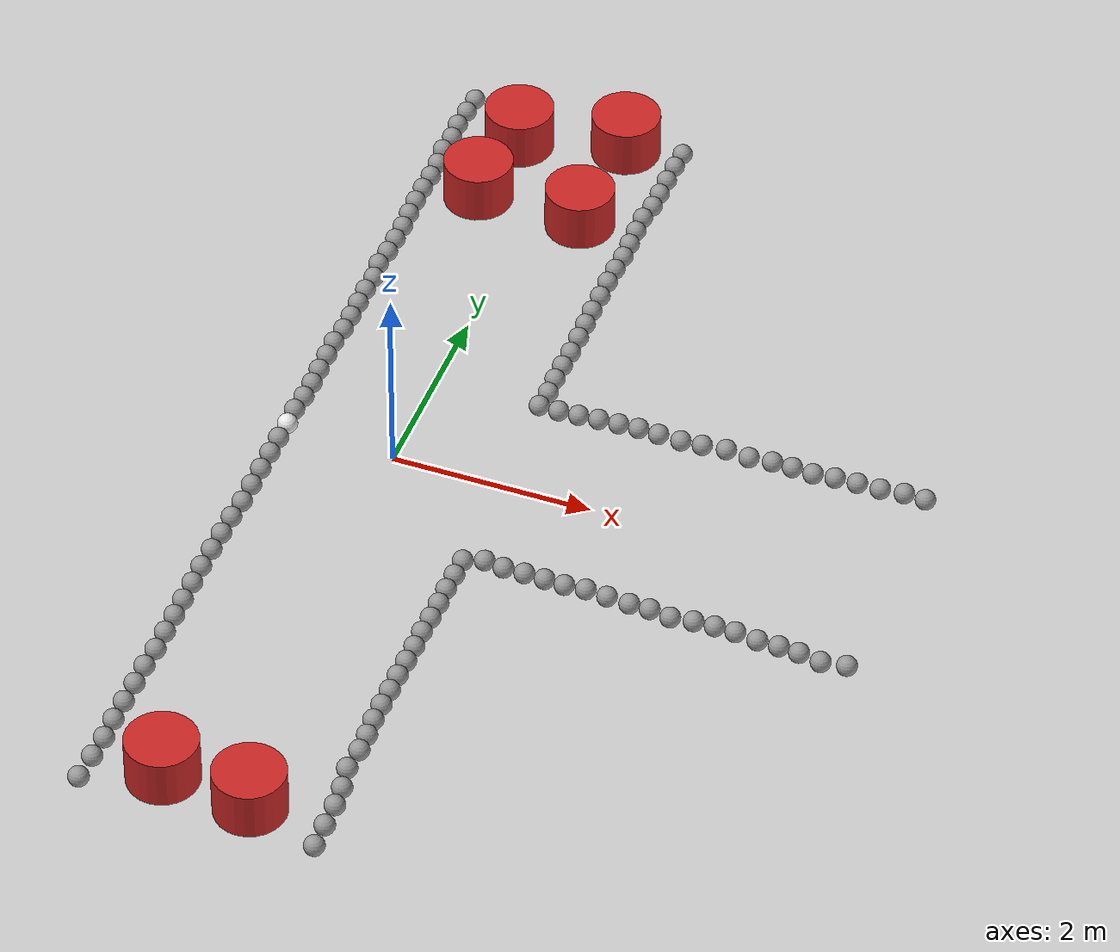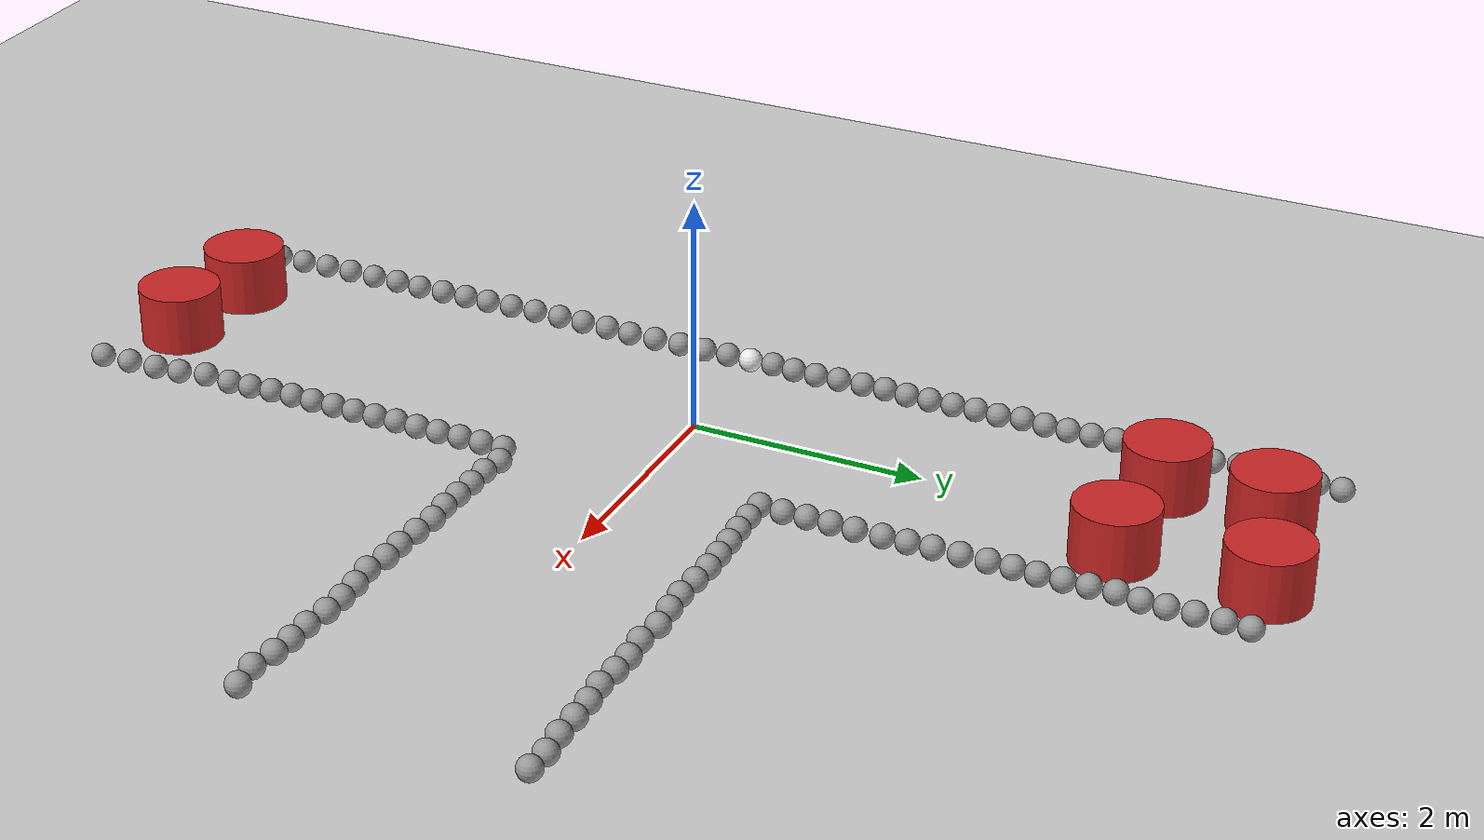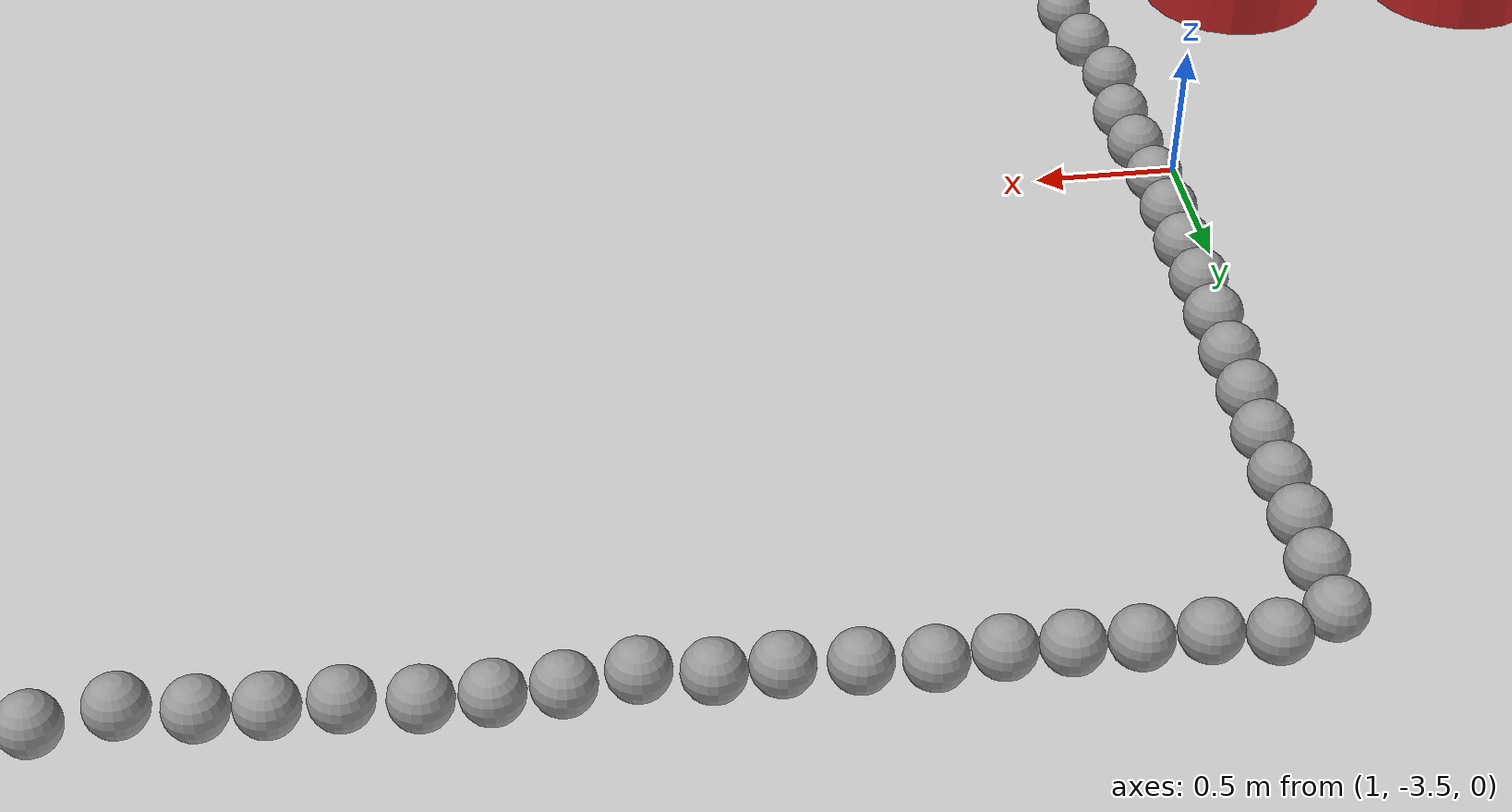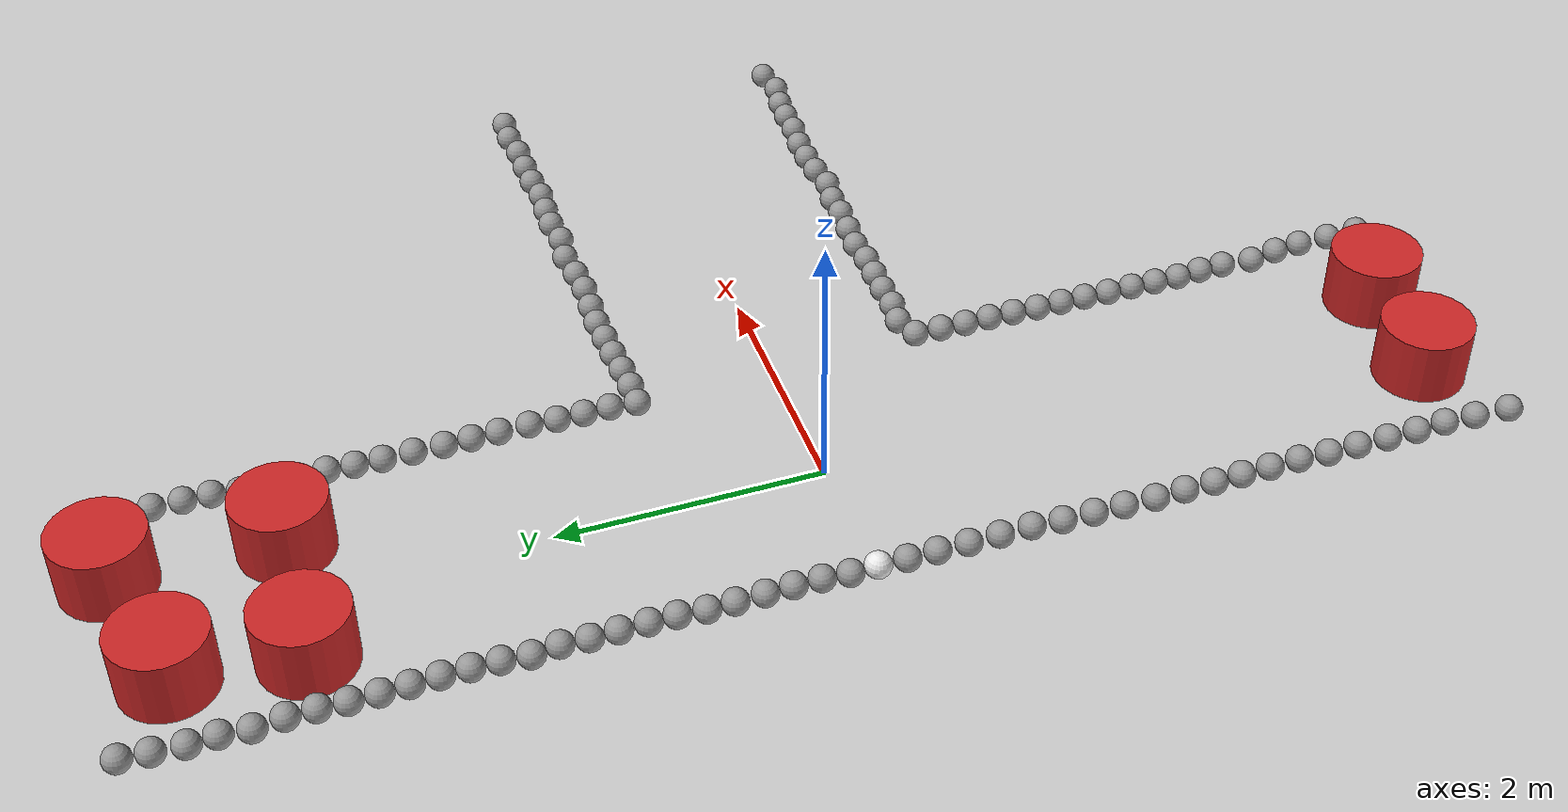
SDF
<sdf version="1.7">
 <world name="default">
  <light name="sun" type="directional">
   <pose>0 0 10 0 -0 0</pose>
   <diffuse>0.8 0.8 0.8 1</diffuse>
   <specular>0.2 0.2 0.2 1</specular>
   <attenuation>
    <range>1000</range>
    <constant>0.9</constant>
    <linear>0.01</linear>
    <quadratic>0.001</quadratic>
   </attenuation>
   <direction>-0.5 0.1 -0.9</direction>
   <spot><inner_angle>0</inner_angle><outer_angle>0</outer_angle><falloff>0</falloff></spot>
  </light>
  <model name="ground_plane">
   <static>1</static>
   <link name="link">
    <collision name="collision">
     <geometry><plane><normal>0 0 1</normal><size>100 100</size></plane></geometry>
     <surface>
      <contact><collide_bitmask>65535</collide_bitmask></contact>
      <friction><ode><mu>100</mu><mu2>50</mu2></ode></friction>
     </surface>
    </collision>
    <visual name="visual">
     <cast_shadows>0</cast_shadows>
     <geometry><plane><normal>0 0 1</normal><size>100 100</size></plane></geometry>
     <material>
      <script><uri>file://media/materials/scripts/gazebo.material</uri><name>Gazebo/Grey</name></script>
     </material>
    </visual>
   </link>
  </model>
  <gravity>0 0 -9.8</gravity>
  <magnetic_field>6e-06 2.3e-05 -4.2e-05</magnetic_field>
  <atmosphere type="adiabatic"/>
  <physics type="ode">
   <max_step_size>0.001</max_step_size>
   <real_time_factor>1</real_time_factor>
   <real_time_update_rate>1000</real_time_update_rate>
  </physics>
  <scene><ambient>0.4 0.4 0.4 1</ambient><background>0.7 0.7 0.7 1</background><shadows>1</shadows></scene>
  <spherical_coordinates>
   <surface_model>EARTH_WGS84</surface_model>
   <latitude_deg>0</latitude_deg>
   <longitude_deg>0</longitude_deg>
   <elevation>0</elevation>
   <heading_deg>0</heading_deg>
  </spherical_coordinates>
  <model name="sphere">
   <link name="link_0">
    <inertial>
     <mass>1</mass>
     <inertia><ixx>0.1</ixx><ixy>0</ixy><ixz>0</ixz><iyy>0.1</iyy><iyz>0</iyz><izz>0.1</izz></inertia>
    </inertial>
    <visual name="visual">
     <geometry><sphere><radius>0.1</radius></sphere></geometry>
     <material>
      <lighting>1</lighting>
      <script><uri>file://media/materials/scripts/gazebo.material</uri><name>Gazebo/White</name></script>
      <shader type="pixel"><normal_map>__default__</normal_map></shader>
      <ambient>0.3 0.3 0.3 1</ambient>
      <diffuse>0.7 0.7 0.7 1</diffuse>
      <specular>0.01 0.01 0.01 1</specular>
      <emissive>0 0 0 1</emissive>
     </material>
    </visual>
    <collision name="collision">
     <geometry><sphere><radius>0.1</radius></sphere></geometry>
     <surface>
      <friction>
       <ode><mu>1</mu><mu2>1</mu2><fdir1>0 0 0</fdir1><slip1>0</slip1><slip2>0</slip2></ode>
       <torsional>
        <coefficient>1</coefficient>
        <patch_radius>0</patch_radius>
        <surface_radius>0</surface_radius>
        <use_patch_radius>1</use_patch_radius>
        <ode><slip>0</slip></ode>
       </torsional>
      </friction>
      <bounce><restitution_coefficient>0</restitution_coefficient><threshold>1e+06</threshold></bounce>
      <contact>
       <collide_without_contact>0</collide_without_contact>
       <collide_without_contact_bitmask>1</collide_without_contact_bitmask>
       <collide_bitmask>1</collide_bitmask>
       <ode>
        <soft_cfm>0</soft_cfm>
        <soft_erp>0.2</soft_erp>
        <kp>1e+13</kp>
        <kd>1</kd>
        <max_vel>0.01</max_vel>
        <min_depth>0</min_depth>
       </ode>
       <bullet>
        <split_impulse>1</split_impulse>
        <split_impulse_penetration_threshold>-0.01</split_impulse_penetration_threshold>
        <soft_cfm>0</soft_cfm>
        <soft_erp>0.2</soft_erp>
        <kp>1e+13</kp>
        <kd>1</kd>
       </bullet>
      </contact>
     </surface>
    </collision>
   </link>
   <static>0</static>
   <pose>-1.091 0.000207 0.1 0.097317 -0.000948 0.005574</pose>
  </model>
  <model name="sphere_0">
   <link name="link_0">
    <inertial>
     <mass>1</mass>
     <inertia><ixx>0.1</ixx><ixy>0</ixy><ixz>0</ixz><iyy>0.1</iyy><iyz>0</iyz><izz>0.1</izz></inertia>
    </inertial>
    <visual name="visual">
     <geometry><sphere><radius>0.1</radius></sphere></geometry>
     <material>
      <lighting>1</lighting>
      <script><uri>file://media/materials/scripts/gazebo.material</uri><name>Gazebo/Grey</name></script>
      <shader type="pixel"><normal_map>__default__</normal_map></shader>
      <ambient>0.3 0.3 0.3 1</ambient>
      <diffuse>0.7 0.7 0.7 1</diffuse>
      <specular>0.01 0.01 0.01 1</specular>
      <emissive>0 0 0 1</emissive>
     </material>
    </visual>
    <collision name="collision">
     <geometry><sphere><radius>0.1</radius></sphere></geometry>
     <surface>
      <friction>
       <ode><mu>1</mu><mu2>1</mu2><fdir1>0 0 0</fdir1><slip1>0</slip1><slip2>0</slip2></ode>
       <torsional>
        <coefficient>1</coefficient>
        <patch_radius>0</patch_radius>
        <surface_radius>0</surface_radius>
        <use_patch_radius>1</use_patch_radius>
        <ode><slip>0</slip></ode>
       </torsional>
      </friction>
      <bounce><restitution_coefficient>0</restitution_coefficient><threshold>1e+06</threshold></bounce>
      <contact>
       <collide_without_contact>0</collide_without_contact>
       <collide_without_contact_bitmask>1</collide_without_contact_bitmask>
       <collide_bitmask>1</collide_bitmask>
       <ode>
        <soft_cfm>0</soft_cfm>
        <soft_erp>0.2</soft_erp>
        <kp>1e+13</kp>
        <kd>1</kd>
        <max_vel>0.01</max_vel>
        <min_depth>0</min_depth>
       </ode>
       <bullet>
        <split_impulse>1</split_impulse>
        <split_impulse_penetration_threshold>-0.01</split_impulse_penetration_threshold>
        <soft_cfm>0</soft_cfm>
        <soft_erp>0.2</soft_erp>
        <kp>1e+13</kp>
        <kd>1</kd>
       </bullet>
      </contact>
     </surface>
    </collision>
   </link>
   <static>0</static>
   <pose>-1.10133 0.204448 0.1 -0.004823 -0.013797 -0.004458</pose>
  </model>
  <model name="sphere_1">
   <link name="link_0">
    <inertial>
     <mass>1</mass>
     <inertia><ixx>0.1</ixx><ixy>0</ixy><ixz>0</ixz><iyy>0.1</iyy><iyz>0</iyz><izz>0.1</izz></inertia>
    </inertial>
    <visual name="visual">
     <geometry><sphere><radius>0.1</radius></sphere></geometry>
     <material>
      <lighting>1</lighting>
      <script><uri>file://media/materials/scripts/gazebo.material</uri><name>Gazebo/Grey</name></script>
      <shader type="pixel"><normal_map>__default__</normal_map></shader>
      <ambient>0.3 0.3 0.3 1</ambient>
      <diffuse>0.7 0.7 0.7 1</diffuse>
      <specular>0.01 0.01 0.01 1</specular>
      <emissive>0 0 0 1</emissive>
     </material>
    </visual>
    <collision name="collision">
     <geometry><sphere><radius>0.1</radius></sphere></geometry>
     <surface>
      <friction>
       <ode><mu>1</mu><mu2>1</mu2><fdir1>0 0 0</fdir1><slip1>0</slip1><slip2>0</slip2></ode>
       <torsional>
        <coefficient>1</coefficient>
        <patch_radius>0</patch_radius>
        <surface_radius>0</surface_radius>
        <use_patch_radius>1</use_patch_radius>
        <ode><slip>0</slip></ode>
       </torsional>
      </friction>
      <bounce><restitution_coefficient>0</restitution_coefficient><threshold>1e+06</threshold></bounce>
      <contact>
       <collide_without_contact>0</collide_without_contact>
       <collide_without_contact_bitmask>1</collide_without_contact_bitmask>
       <collide_bitmask>1</collide_bitmask>
       <ode>
        <soft_cfm>0</soft_cfm>
        <soft_erp>0.2</soft_erp>
        <kp>1e+13</kp>
        <kd>1</kd>
        <max_vel>0.01</max_vel>
        <min_depth>0</min_depth>
       </ode>
       <bullet>
        <split_impulse>1</split_impulse>
        <split_impulse_penetration_threshold>-0.01</split_impulse_penetration_threshold>
        <soft_cfm>0</soft_cfm>
        <soft_erp>0.2</soft_erp>
        <kp>1e+13</kp>
        <kd>1</kd>
       </bullet>
      </contact>
     </surface>
    </collision>
   </link>
   <static>0</static>
   <pose>-1.08492 0.403884 0.1 -0.010826 0.002979 -0.008224</pose>
  </model>
  <model name="sphere_2">
   <link name="link_0">
    <inertial>
     <mass>1</mass>
     <inertia><ixx>0.1</ixx><ixy>0</ixy><ixz>0</ixz><iyy>0.1</iyy><iyz>0</iyz><izz>0.1</izz></inertia>
    </inertial>
    <visual name="visual">
     <geometry><sphere><radius>0.1</radius></sphere></geometry>
     <material>
      <lighting>1</lighting>
      <script><uri>file://media/materials/scripts/gazebo.material</uri><name>Gazebo/Grey</name></script>
      <shader type="pixel"><normal_map>__default__</normal_map></shader>
      <ambient>0.3 0.3 0.3 1</ambient>
      <diffuse>0.7 0.7 0.7 1</diffuse>
      <specular>0.01 0.01 0.01 1</specular>
      <emissive>0 0 0 1</emissive>
     </material>
    </visual>
    <collision name="collision">
     <geometry><sphere><radius>0.1</radius></sphere></geometry>
     <surface>
      <friction>
       <ode><mu>1</mu><mu2>1</mu2><fdir1>0 0 0</fdir1><slip1>0</slip1><slip2>0</slip2></ode>
       <torsional>
        <coefficient>1</coefficient>
        <patch_radius>0</patch_radius>
        <surface_radius>0</surface_radius>
        <use_patch_radius>1</use_patch_radius>
        <ode><slip>0</slip></ode>
       </torsional>
      </friction>
      <bounce><restitution_coefficient>0</restitution_coefficient><threshold>1e+06</threshold></bounce>
      <contact>
       <collide_without_contact>0</collide_without_contact>
       <collide_without_contact_bitmask>1</collide_without_contact_bitmask>
       <collide_bitmask>1</collide_bitmask>
       <ode>
        <soft_cfm>0</soft_cfm>
        <soft_erp>0.2</soft_erp>
        <kp>1e+13</kp>
        <kd>1</kd>
        <max_vel>0.01</max_vel>
        <min_depth>0</min_depth>
       </ode>
       <bullet>
        <split_impulse>1</split_impulse>
        <split_impulse_penetration_threshold>-0.01</split_impulse_penetration_threshold>
        <soft_cfm>0</soft_cfm>
        <soft_erp>0.2</soft_erp>
        <kp>1e+13</kp>
        <kd>1</kd>
       </bullet>
      </contact>
     </surface>
    </collision>
   </link>
   <static>0</static>
   <pose>-1.08295 0.60761 0.1 -0.067159 0.002545 0.001841</pose>
  </model>
  <model name="sphere_3">
   <link name="link_0">
    <inertial>
     <mass>1</mass>
     <inertia><ixx>0.1</ixx><ixy>0</ixy><ixz>0</ixz><iyy>0.1</iyy><iyz>0</iyz><izz>0.1</izz></inertia>
    </inertial>
    <visual name="visual">
     <geometry><sphere><radius>0.1</radius></sphere></geometry>
     <material>
      <lighting>1</lighting>
      <script><uri>file://media/materials/scripts/gazebo.material</uri><name>Gazebo/Grey</name></script>
      <shader type="pixel"><normal_map>__default__</normal_map></shader>
      <ambient>0.3 0.3 0.3 1</ambient>
      <diffuse>0.7 0.7 0.7 1</diffuse>
      <specular>0.01 0.01 0.01 1</specular>
      <emissive>0 0 0 1</emissive>
     </material>
    </visual>
    <collision name="collision">
     <geometry><sphere><radius>0.1</radius></sphere></geometry>
     <surface>
      <friction>
       <ode><mu>1</mu><mu2>1</mu2><fdir1>0 0 0</fdir1><slip1>0</slip1><slip2>0</slip2></ode>
       <torsional>
        <coefficient>1</coefficient>
        <patch_radius>0</patch_radius>
        <surface_radius>0</surface_radius>
        <use_patch_radius>1</use_patch_radius>
        <ode><slip>0</slip></ode>
       </torsional>
      </friction>
      <bounce><restitution_coefficient>0</restitution_coefficient><threshold>1e+06</threshold></bounce>
      <contact>
       <collide_without_contact>0</collide_without_contact>
       <collide_without_contact_bitmask>1</collide_without_contact_bitmask>
       <collide_bitmask>1</collide_bitmask>
       <ode>
        <soft_cfm>0</soft_cfm>
        <soft_erp>0.2</soft_erp>
        <kp>1e+13</kp>
        <kd>1</kd>
        <max_vel>0.01</max_vel>
        <min_depth>0</min_depth>
       </ode>
       <bullet>
        <split_impulse>1</split_impulse>
        <split_impulse_penetration_threshold>-0.01</split_impulse_penetration_threshold>
        <soft_cfm>0</soft_cfm>
        <soft_erp>0.2</soft_erp>
        <kp>1e+13</kp>
        <kd>1</kd>
       </bullet>
      </contact>
     </surface>
    </collision>
   </link>
   <static>0</static>
   <pose>-1.0912 0.811371 0.1 0 -0 0</pose>
  </model>
  <model name="sphere_4">
   <link name="link_0">
    <inertial>
     <mass>1</mass>
     <inertia><ixx>0.1</ixx><ixy>0</ixy><ixz>0</ixz><iyy>0.1</iyy><iyz>0</iyz><izz>0.1</izz></inertia>
    </inertial>
    <visual name="visual">
     <geometry><sphere><radius>0.1</radius></sphere></geometry>
     <material>
      <lighting>1</lighting>
      <script><uri>file://media/materials/scripts/gazebo.material</uri><name>Gazebo/Grey</name></script>
      <shader type="pixel"><normal_map>__default__</normal_map></shader>
      <ambient>0.3 0.3 0.3 1</ambient>
      <diffuse>0.7 0.7 0.7 1</diffuse>
      <specular>0.01 0.01 0.01 1</specular>
      <emissive>0 0 0 1</emissive>
     </material>
    </visual>
    <collision name="collision">
     <geometry><sphere><radius>0.1</radius></sphere></geometry>
     <surface>
      <friction>
       <ode><mu>1</mu><mu2>1</mu2><fdir1>0 0 0</fdir1><slip1>0</slip1><slip2>0</slip2></ode>
       <torsional>
        <coefficient>1</coefficient>
        <patch_radius>0</patch_radius>
        <surface_radius>0</surface_radius>
        <use_patch_radius>1</use_patch_radius>
        <ode><slip>0</slip></ode>
       </torsional>
      </friction>
      <bounce><restitution_coefficient>0</restitution_coefficient><threshold>1e+06</threshold></bounce>
      <contact>
       <collide_without_contact>0</collide_without_contact>
       <collide_without_contact_bitmask>1</collide_without_contact_bitmask>
       <collide_bitmask>1</collide_bitmask>
       <ode>
        <soft_cfm>0</soft_cfm>
        <soft_erp>0.2</soft_erp>
        <kp>1e+13</kp>
        <kd>1</kd>
        <max_vel>0.01</max_vel>
        <min_depth>0</min_depth>
       </ode>
       <bullet>
        <split_impulse>1</split_impulse>
        <split_impulse_penetration_threshold>-0.01</split_impulse_penetration_threshold>
        <soft_cfm>0</soft_cfm>
        <soft_erp>0.2</soft_erp>
        <kp>1e+13</kp>
        <kd>1</kd>
       </bullet>
      </contact>
     </surface>
    </collision>
   </link>
   <static>0</static>
   <pose>-1.09687 1.02525 0.1 0.000955 -0.000196 0.000241</pose>
  </model>
  <model name="sphere_5">
   <link name="link_0">
    <inertial>
     <mass>1</mass>
     <inertia><ixx>0.1</ixx><ixy>0</ixy><ixz>0</ixz><iyy>0.1</iyy><iyz>0</iyz><izz>0.1</izz></inertia>
    </inertial>
    <visual name="visual">
     <geometry><sphere><radius>0.1</radius></sphere></geometry>
     <material>
      <lighting>1</lighting>
      <script><uri>file://media/materials/scripts/gazebo.material</uri><name>Gazebo/Grey</name></script>
      <shader type="pixel"><normal_map>__default__</normal_map></shader>
      <ambient>0.3 0.3 0.3 1</ambient>
      <diffuse>0.7 0.7 0.7 1</diffuse>
      <specular>0.01 0.01 0.01 1</specular>
      <emissive>0 0 0 1</emissive>
     </material>
    </visual>
    <collision name="collision">
     <geometry><sphere><radius>0.1</radius></sphere></geometry>
     <surface>
      <friction>
       <ode><mu>1</mu><mu2>1</mu2><fdir1>0 0 0</fdir1><slip1>0</slip1><slip2>0</slip2></ode>
       <torsional>
        <coefficient>1</coefficient>
        <patch_radius>0</patch_radius>
        <surface_radius>0</surface_radius>
        <use_patch_radius>1</use_patch_radius>
        <ode><slip>0</slip></ode>
       </torsional>
      </friction>
      <bounce><restitution_coefficient>0</restitution_coefficient><threshold>1e+06</threshold></bounce>
      <contact>
       <collide_without_contact>0</collide_without_contact>
       <collide_without_contact_bitmask>1</collide_without_contact_bitmask>
       <collide_bitmask>1</collide_bitmask>
       <ode>
        <soft_cfm>0</soft_cfm>
        <soft_erp>0.2</soft_erp>
        <kp>1e+13</kp>
        <kd>1</kd>
        <max_vel>0.01</max_vel>
        <min_depth>0</min_depth>
       </ode>
       <bullet>
        <split_impulse>1</split_impulse>
        <split_impulse_penetration_threshold>-0.01</split_impulse_penetration_threshold>
        <soft_cfm>0</soft_cfm>
        <soft_erp>0.2</soft_erp>
        <kp>1e+13</kp>
        <kd>1</kd>
       </bullet>
      </contact>
     </surface>
    </collision>
   </link>
   <static>0</static>
   <pose>-1.10184 1.22526 0.1 0.026409 -0.003889 0.001047</pose>
  </model>
  <model name="sphere_6">
   <link name="link_0">
    <inertial>
     <mass>1</mass>
     <inertia><ixx>0.1</ixx><ixy>0</ixy><ixz>0</ixz><iyy>0.1</iyy><iyz>0</iyz><izz>0.1</izz></inertia>
    </inertial>
    <visual name="visual">
     <geometry><sphere><radius>0.1</radius></sphere></geometry>
     <material>
      <lighting>1</lighting>
      <script><uri>file://media/materials/scripts/gazebo.material</uri><name>Gazebo/Grey</name></script>
      <shader type="pixel"><normal_map>__default__</normal_map></shader>
      <ambient>0.3 0.3 0.3 1</ambient>
      <diffuse>0.7 0.7 0.7 1</diffuse>
      <specular>0.01 0.01 0.01 1</specular>
      <emissive>0 0 0 1</emissive>
     </material>
    </visual>
    <collision name="collision">
     <geometry><sphere><radius>0.1</radius></sphere></geometry>
     <surface>
      <friction>
       <ode><mu>1</mu><mu2>1</mu2><fdir1>0 0 0</fdir1><slip1>0</slip1><slip2>0</slip2></ode>
       <torsional>
        <coefficient>1</coefficient>
        <patch_radius>0</patch_radius>
        <surface_radius>0</surface_radius>
        <use_patch_radius>1</use_patch_radius>
        <ode><slip>0</slip></ode>
       </torsional>
      </friction>
      <bounce><restitution_coefficient>0</restitution_coefficient><threshold>1e+06</threshold></bounce>
      <contact>
       <collide_without_contact>0</collide_without_contact>
       <collide_without_contact_bitmask>1</collide_without_contact_bitmask>
       <collide_bitmask>1</collide_bitmask>
       <ode>
        <soft_cfm>0</soft_cfm>
        <soft_erp>0.2</soft_erp>
        <kp>1e+13</kp>
        <kd>1</kd>
        <max_vel>0.01</max_vel>
        <min_depth>0</min_depth>
       </ode>
       <bullet>
        <split_impulse>1</split_impulse>
        <split_impulse_penetration_threshold>-0.01</split_impulse_penetration_threshold>
        <soft_cfm>0</soft_cfm>
        <soft_erp>0.2</soft_erp>
        <kp>1e+13</kp>
        <kd>1</kd>
       </bullet>
      </contact>
     </surface>
    </collision>
   </link>
   <static>0</static>
   <pose>-1.08366 1.42822 0.1 -0.035577 0.004267 0.000847</pose>
  </model>
  <model name="sphere_7">
   <link name="link_0">
    <inertial>
     <mass>1</mass>
     <inertia><ixx>0.1</ixx><ixy>0</ixy><ixz>0</ixz><iyy>0.1</iyy><iyz>0</iyz><izz>0.1</izz></inertia>
    </inertial>
    <visual name="visual">
     <geometry><sphere><radius>0.1</radius></sphere></geometry>
     <material>
      <lighting>1</lighting>
      <script><uri>file://media/materials/scripts/gazebo.material</uri><name>Gazebo/Grey</name></script>
      <shader type="pixel"><normal_map>__default__</normal_map></shader>
      <ambient>0.3 0.3 0.3 1</ambient>
      <diffuse>0.7 0.7 0.7 1</diffuse>
      <specular>0.01 0.01 0.01 1</specular>
      <emissive>0 0 0 1</emissive>
     </material>
    </visual>
    <collision name="collision">
     <geometry><sphere><radius>0.1</radius></sphere></geometry>
     <surface>
      <friction>
       <ode><mu>1</mu><mu2>1</mu2><fdir1>0 0 0</fdir1><slip1>0</slip1><slip2>0</slip2></ode>
       <torsional>
        <coefficient>1</coefficient>
        <patch_radius>0</patch_radius>
        <surface_radius>0</surface_radius>
        <use_patch_radius>1</use_patch_radius>
        <ode><slip>0</slip></ode>
       </torsional>
      </friction>
      <bounce><restitution_coefficient>0</restitution_coefficient><threshold>1e+06</threshold></bounce>
      <contact>
       <collide_without_contact>0</collide_without_contact>
       <collide_without_contact_bitmask>1</collide_without_contact_bitmask>
       <collide_bitmask>1</collide_bitmask>
       <ode>
        <soft_cfm>0</soft_cfm>
        <soft_erp>0.2</soft_erp>
        <kp>1e+13</kp>
        <kd>1</kd>
        <max_vel>0.01</max_vel>
        <min_depth>0</min_depth>
       </ode>
       <bullet>
        <split_impulse>1</split_impulse>
        <split_impulse_penetration_threshold>-0.01</split_impulse_penetration_threshold>
        <soft_cfm>0</soft_cfm>
        <soft_erp>0.2</soft_erp>
        <kp>1e+13</kp>
        <kd>1</kd>
       </bullet>
      </contact>
     </surface>
    </collision>
   </link>
   <static>0</static>
   <pose>-1.08447 1.62822 0.1 0.105529 0.002076 0.000151</pose>
  </model>
  <model name="sphere_8">
   <link name="link_0">
    <inertial>
     <mass>1</mass>
     <inertia><ixx>0.1</ixx><ixy>0</ixy><ixz>0</ixz><iyy>0.1</iyy><iyz>0</iyz><izz>0.1</izz></inertia>
    </inertial>
    <visual name="visual">
     <geometry><sphere><radius>0.1</radius></sphere></geometry>
     <material>
      <lighting>1</lighting>
      <script><uri>file://media/materials/scripts/gazebo.material</uri><name>Gazebo/Grey</name></script>
      <shader type="pixel"><normal_map>__default__</normal_map></shader>
      <ambient>0.3 0.3 0.3 1</ambient>
      <diffuse>0.7 0.7 0.7 1</diffuse>
      <specular>0.01 0.01 0.01 1</specular>
      <emissive>0 0 0 1</emissive>
     </material>
    </visual>
    <collision name="collision">
     <geometry><sphere><radius>0.1</radius></sphere></geometry>
     <surface>
      <friction>
       <ode><mu>1</mu><mu2>1</mu2><fdir1>0 0 0</fdir1><slip1>0</slip1><slip2>0</slip2></ode>
       <torsional>
        <coefficient>1</coefficient>
        <patch_radius>0</patch_radius>
        <surface_radius>0</surface_radius>
        <use_patch_radius>1</use_patch_radius>
        <ode><slip>0</slip></ode>
       </torsional>
      </friction>
      <bounce><restitution_coefficient>0</restitution_coefficient><threshold>1e+06</threshold></bounce>
      <contact>
       <collide_without_contact>0</collide_without_contact>
       <collide_without_contact_bitmask>1</collide_without_contact_bitmask>
       <collide_bitmask>1</collide_bitmask>
       <ode>
        <soft_cfm>0</soft_cfm>
        <soft_erp>0.2</soft_erp>
        <kp>1e+13</kp>
        <kd>1</kd>
        <max_vel>0.01</max_vel>
        <min_depth>0</min_depth>
       </ode>
       <bullet>
        <split_impulse>1</split_impulse>
        <split_impulse_penetration_threshold>-0.01</split_impulse_penetration_threshold>
        <soft_cfm>0</soft_cfm>
        <soft_erp>0.2</soft_erp>
        <kp>1e+13</kp>
        <kd>1</kd>
       </bullet>
      </contact>
     </surface>
    </collision>
   </link>
   <static>0</static>
   <pose>-1.09701 -0.2119 0.1 0 -0 0</pose>
  </model>
  <model name="sphere_9">
   <link name="link_0">
    <inertial>
     <mass>1</mass>
     <inertia><ixx>0.1</ixx><ixy>0</ixy><ixz>0</ixz><iyy>0.1</iyy><iyz>0</iyz><izz>0.1</izz></inertia>
    </inertial>
    <visual name="visual">
     <geometry><sphere><radius>0.1</radius></sphere></geometry>
     <material>
      <lighting>1</lighting>
      <script><uri>file://media/materials/scripts/gazebo.material</uri><name>Gazebo/Grey</name></script>
      <shader type="pixel"><normal_map>__default__</normal_map></shader>
      <ambient>0.3 0.3 0.3 1</ambient>
      <diffuse>0.7 0.7 0.7 1</diffuse>
      <specular>0.01 0.01 0.01 1</specular>
      <emissive>0 0 0 1</emissive>
     </material>
    </visual>
    <collision name="collision">
     <geometry><sphere><radius>0.1</radius></sphere></geometry>
     <surface>
      <friction>
       <ode><mu>1</mu><mu2>1</mu2><fdir1>0 0 0</fdir1><slip1>0</slip1><slip2>0</slip2></ode>
       <torsional>
        <coefficient>1</coefficient>
        <patch_radius>0</patch_radius>
        <surface_radius>0</surface_radius>
        <use_patch_radius>1</use_patch_radius>
        <ode><slip>0</slip></ode>
       </torsional>
      </friction>
      <bounce><restitution_coefficient>0</restitution_coefficient><threshold>1e+06</threshold></bounce>
      <contact>
       <collide_without_contact>0</collide_without_contact>
       <collide_without_contact_bitmask>1</collide_without_contact_bitmask>
       <collide_bitmask>1</collide_bitmask>
       <ode>
        <soft_cfm>0</soft_cfm>
        <soft_erp>0.2</soft_erp>
        <kp>1e+13</kp>
        <kd>1</kd>
        <max_vel>0.01</max_vel>
        <min_depth>0</min_depth>
       </ode>
       <bullet>
        <split_impulse>1</split_impulse>
        <split_impulse_penetration_threshold>-0.01</split_impulse_penetration_threshold>
        <soft_cfm>0</soft_cfm>
        <soft_erp>0.2</soft_erp>
        <kp>1e+13</kp>
        <kd>1</kd>
       </bullet>
      </contact>
     </surface>
    </collision>
   </link>
   <static>0</static>
   <pose>-1.09596 -0.433443 0.1 0 -0 0</pose>
  </model>
  <model name="sphere_10">
   <link name="link_0">
    <inertial>
     <mass>1</mass>
     <inertia><ixx>0.1</ixx><ixy>0</ixy><ixz>0</ixz><iyy>0.1</iyy><iyz>0</iyz><izz>0.1</izz></inertia>
    </inertial>
    <visual name="visual">
     <geometry><sphere><radius>0.1</radius></sphere></geometry>
     <material>
      <lighting>1</lighting>
      <script><uri>file://media/materials/scripts/gazebo.material</uri><name>Gazebo/Grey</name></script>
      <shader type="pixel"><normal_map>__default__</normal_map></shader>
      <ambient>0.3 0.3 0.3 1</ambient>
      <diffuse>0.7 0.7 0.7 1</diffuse>
      <specular>0.01 0.01 0.01 1</specular>
      <emissive>0 0 0 1</emissive>
     </material>
    </visual>
    <collision name="collision">
     <geometry><sphere><radius>0.1</radius></sphere></geometry>
     <surface>
      <friction>
       <ode><mu>1</mu><mu2>1</mu2><fdir1>0 0 0</fdir1><slip1>0</slip1><slip2>0</slip2></ode>
       <torsional>
        <coefficient>1</coefficient>
        <patch_radius>0</patch_radius>
        <surface_radius>0</surface_radius>
        <use_patch_radius>1</use_patch_radius>
        <ode><slip>0</slip></ode>
       </torsional>
      </friction>
      <bounce><restitution_coefficient>0</restitution_coefficient><threshold>1e+06</threshold></bounce>
      <contact>
       <collide_without_contact>0</collide_without_contact>
       <collide_without_contact_bitmask>1</collide_without_contact_bitmask>
       <collide_bitmask>1</collide_bitmask>
       <ode>
        <soft_cfm>0</soft_cfm>
        <soft_erp>0.2</soft_erp>
        <kp>1e+13</kp>
        <kd>1</kd>
        <max_vel>0.01</max_vel>
        <min_depth>0</min_depth>
       </ode>
       <bullet>
        <split_impulse>1</split_impulse>
        <split_impulse_penetration_threshold>-0.01</split_impulse_penetration_threshold>
        <soft_cfm>0</soft_cfm>
        <soft_erp>0.2</soft_erp>
        <kp>1e+13</kp>
        <kd>1</kd>
       </bullet>
      </contact>
     </surface>
    </collision>
   </link>
   <static>0</static>
   <pose>-1.09566 -0.665013 0.1 0 -0 0</pose>
  </model>
  <model name="sphere_11">
   <link name="link_0">
    <inertial>
     <mass>1</mass>
     <inertia><ixx>0.1</ixx><ixy>0</ixy><ixz>0</ixz><iyy>0.1</iyy><iyz>0</iyz><izz>0.1</izz></inertia>
    </inertial>
    <visual name="visual">
     <geometry><sphere><radius>0.1</radius></sphere></geometry>
     <material>
      <lighting>1</lighting>
      <script><uri>file://media/materials/scripts/gazebo.material</uri><name>Gazebo/Grey</name></script>
      <shader type="pixel"><normal_map>__default__</normal_map></shader>
      <ambient>0.3 0.3 0.3 1</ambient>
      <diffuse>0.7 0.7 0.7 1</diffuse>
      <specular>0.01 0.01 0.01 1</specular>
      <emissive>0 0 0 1</emissive>
     </material>
    </visual>
    <collision name="collision">
     <geometry><sphere><radius>0.1</radius></sphere></geometry>
     <surface>
      <friction>
       <ode><mu>1</mu><mu2>1</mu2><fdir1>0 0 0</fdir1><slip1>0</slip1><slip2>0</slip2></ode>
       <torsional>
        <coefficient>1</coefficient>
        <patch_radius>0</patch_radius>
        <surface_radius>0</surface_radius>
        <use_patch_radius>1</use_patch_radius>
        <ode><slip>0</slip></ode>
       </torsional>
      </friction>
      <bounce><restitution_coefficient>0</restitution_coefficient><threshold>1e+06</threshold></bounce>
      <contact>
       <collide_without_contact>0</collide_without_contact>
       <collide_without_contact_bitmask>1</collide_without_contact_bitmask>
       <collide_bitmask>1</collide_bitmask>
       <ode>
        <soft_cfm>0</soft_cfm>
        <soft_erp>0.2</soft_erp>
        <kp>1e+13</kp>
        <kd>1</kd>
        <max_vel>0.01</max_vel>
        <min_depth>0</min_depth>
       </ode>
       <bullet>
        <split_impulse>1</split_impulse>
        <split_impulse_penetration_threshold>-0.01</split_impulse_penetration_threshold>
        <soft_cfm>0</soft_cfm>
        <soft_erp>0.2</soft_erp>
        <kp>1e+13</kp>
        <kd>1</kd>
       </bullet>
      </contact>
     </surface>
    </collision>
   </link>
   <static>0</static>
   <pose>-1.0935 -0.901164 0.1 0 -0 0</pose>
  </model>
  <model name="sphere_12">
   <link name="link_0">
    <inertial>
     <mass>1</mass>
     <inertia><ixx>0.1</ixx><ixy>0</ixy><ixz>0</ixz><iyy>0.1</iyy><iyz>0</iyz><izz>0.1</izz></inertia>
    </inertial>
    <visual name="visual">
     <geometry><sphere><radius>0.1</radius></sphere></geometry>
     <material>
      <lighting>1</lighting>
      <script><uri>file://media/materials/scripts/gazebo.material</uri><name>Gazebo/Grey</name></script>
      <shader type="pixel"><normal_map>__default__</normal_map></shader>
      <ambient>0.3 0.3 0.3 1</ambient>
      <diffuse>0.7 0.7 0.7 1</diffuse>
      <specular>0.01 0.01 0.01 1</specular>
      <emissive>0 0 0 1</emissive>
     </material>
    </visual>
    <collision name="collision">
     <geometry><sphere><radius>0.1</radius></sphere></geometry>
     <surface>
      <friction>
       <ode><mu>1</mu><mu2>1</mu2><fdir1>0 0 0</fdir1><slip1>0</slip1><slip2>0</slip2></ode>
       <torsional>
        <coefficient>1</coefficient>
        <patch_radius>0</patch_radius>
        <surface_radius>0</surface_radius>
        <use_patch_radius>1</use_patch_radius>
        <ode><slip>0</slip></ode>
       </torsional>
      </friction>
      <bounce><restitution_coefficient>0</restitution_coefficient><threshold>1e+06</threshold></bounce>
      <contact>
       <collide_without_contact>0</collide_without_contact>
       <collide_without_contact_bitmask>1</collide_without_contact_bitmask>
       <collide_bitmask>1</collide_bitmask>
       <ode>
        <soft_cfm>0</soft_cfm>
        <soft_erp>0.2</soft_erp>
        <kp>1e+13</kp>
        <kd>1</kd>
        <max_vel>0.01</max_vel>
        <min_depth>0</min_depth>
       </ode>
       <bullet>
        <split_impulse>1</split_impulse>
        <split_impulse_penetration_threshold>-0.01</split_impulse_penetration_threshold>
        <soft_cfm>0</soft_cfm>
        <soft_erp>0.2</soft_erp>
        <kp>1e+13</kp>
        <kd>1</kd>
       </bullet>
      </contact>
     </surface>
    </collision>
   </link>
   <static>0</static>
   <pose>-1.09033 -1.14062 0.1 0 -0 0</pose>
  </model>
  <model name="sphere_13">
   <link name="link_0">
    <inertial>
     <mass>1</mass>
     <inertia><ixx>0.1</ixx><ixy>0</ixy><ixz>0</ixz><iyy>0.1</iyy><iyz>0</iyz><izz>0.1</izz></inertia>
    </inertial>
    <visual name="visual">
     <geometry><sphere><radius>0.1</radius></sphere></geometry>
     <material>
      <lighting>1</lighting>
      <script><uri>file://media/materials/scripts/gazebo.material</uri><name>Gazebo/Grey</name></script>
      <shader type="pixel"><normal_map>__default__</normal_map></shader>
      <ambient>0.3 0.3 0.3 1</ambient>
      <diffuse>0.7 0.7 0.7 1</diffuse>
      <specular>0.01 0.01 0.01 1</specular>
      <emissive>0 0 0 1</emissive>
     </material>
    </visual>
    <collision name="collision">
     <geometry><sphere><radius>0.1</radius></sphere></geometry>
     <surface>
      <friction>
       <ode><mu>1</mu><mu2>1</mu2><fdir1>0 0 0</fdir1><slip1>0</slip1><slip2>0</slip2></ode>
       <torsional>
        <coefficient>1</coefficient>
        <patch_radius>0</patch_radius>
        <surface_radius>0</surface_radius>
        <use_patch_radius>1</use_patch_radius>
        <ode><slip>0</slip></ode>
       </torsional>
      </friction>
      <bounce><restitution_coefficient>0</restitution_coefficient><threshold>1e+06</threshold></bounce>
      <contact>
       <collide_without_contact>0</collide_without_contact>
       <collide_without_contact_bitmask>1</collide_without_contact_bitmask>
       <collide_bitmask>1</collide_bitmask>
       <ode>
        <soft_cfm>0</soft_cfm>
        <soft_erp>0.2</soft_erp>
        <kp>1e+13</kp>
        <kd>1</kd>
        <max_vel>0.01</max_vel>
        <min_depth>0</min_depth>
       </ode>
       <bullet>
        <split_impulse>1</split_impulse>
        <split_impulse_penetration_threshold>-0.01</split_impulse_penetration_threshold>
        <soft_cfm>0</soft_cfm>
        <soft_erp>0.2</soft_erp>
        <kp>1e+13</kp>
        <kd>1</kd>
       </bullet>
      </contact>
     </surface>
    </collision>
   </link>
   <static>0</static>
   <pose>-1.08795 1.83353 0.1 -0.014295 -0.000751 0.003419</pose>
  </model>
  <model name="sphere_14">
   <link name="link_0">
    <inertial>
     <mass>1</mass>
     <inertia><ixx>0.1</ixx><ixy>0</ixy><ixz>0</ixz><iyy>0.1</iyy><iyz>0</iyz><izz>0.1</izz></inertia>
    </inertial>
    <visual name="visual">
     <geometry><sphere><radius>0.1</radius></sphere></geometry>
     <material>
      <lighting>1</lighting>
      <script><uri>file://media/materials/scripts/gazebo.material</uri><name>Gazebo/Grey</name></script>
      <shader type="pixel"><normal_map>__default__</normal_map></shader>
      <ambient>0.3 0.3 0.3 1</ambient>
      <diffuse>0.7 0.7 0.7 1</diffuse>
      <specular>0.01 0.01 0.01 1</specular>
      <emissive>0 0 0 1</emissive>
     </material>
    </visual>
    <collision name="collision">
     <geometry><sphere><radius>0.1</radius></sphere></geometry>
     <surface>
      <friction>
       <ode><mu>1</mu><mu2>1</mu2><fdir1>0 0 0</fdir1><slip1>0</slip1><slip2>0</slip2></ode>
       <torsional>
        <coefficient>1</coefficient>
        <patch_radius>0</patch_radius>
        <surface_radius>0</surface_radius>
        <use_patch_radius>1</use_patch_radius>
        <ode><slip>0</slip></ode>
       </torsional>
      </friction>
      <bounce><restitution_coefficient>0</restitution_coefficient><threshold>1e+06</threshold></bounce>
      <contact>
       <collide_without_contact>0</collide_without_contact>
       <collide_without_contact_bitmask>1</collide_without_contact_bitmask>
       <collide_bitmask>1</collide_bitmask>
       <ode>
        <soft_cfm>0</soft_cfm>
        <soft_erp>0.2</soft_erp>
        <kp>1e+13</kp>
        <kd>1</kd>
        <max_vel>0.01</max_vel>
        <min_depth>0</min_depth>
       </ode>
       <bullet>
        <split_impulse>1</split_impulse>
        <split_impulse_penetration_threshold>-0.01</split_impulse_penetration_threshold>
        <soft_cfm>0</soft_cfm>
        <soft_erp>0.2</soft_erp>
        <kp>1e+13</kp>
        <kd>1</kd>
       </bullet>
      </contact>
     </surface>
    </collision>
   </link>
   <static>0</static>
   <pose>-1.09216 2.03365 0.1 -0.018913 0.007007 -0.012355</pose>
  </model>
  <model name="sphere_15">
   <link name="link_0">
    <inertial>
     <mass>1</mass>
     <inertia><ixx>0.1</ixx><ixy>0</ixy><ixz>0</ixz><iyy>0.1</iyy><iyz>0</iyz><izz>0.1</izz></inertia>
    </inertial>
    <visual name="visual">
     <geometry><sphere><radius>0.1</radius></sphere></geometry>
     <material>
      <lighting>1</lighting>
      <script><uri>file://media/materials/scripts/gazebo.material</uri><name>Gazebo/Grey</name></script>
      <shader type="pixel"><normal_map>__default__</normal_map></shader>
      <ambient>0.3 0.3 0.3 1</ambient>
      <diffuse>0.7 0.7 0.7 1</diffuse>
      <specular>0.01 0.01 0.01 1</specular>
      <emissive>0 0 0 1</emissive>
     </material>
    </visual>
    <collision name="collision">
     <geometry><sphere><radius>0.1</radius></sphere></geometry>
     <surface>
      <friction>
       <ode><mu>1</mu><mu2>1</mu2><fdir1>0 0 0</fdir1><slip1>0</slip1><slip2>0</slip2></ode>
       <torsional>
        <coefficient>1</coefficient>
        <patch_radius>0</patch_radius>
        <surface_radius>0</surface_radius>
        <use_patch_radius>1</use_patch_radius>
        <ode><slip>0</slip></ode>
       </torsional>
      </friction>
      <bounce><restitution_coefficient>0</restitution_coefficient><threshold>1e+06</threshold></bounce>
      <contact>
       <collide_without_contact>0</collide_without_contact>
       <collide_without_contact_bitmask>1</collide_without_contact_bitmask>
       <collide_bitmask>1</collide_bitmask>
       <ode>
        <soft_cfm>0</soft_cfm>
        <soft_erp>0.2</soft_erp>
        <kp>1e+13</kp>
        <kd>1</kd>
        <max_vel>0.01</max_vel>
        <min_depth>0</min_depth>
       </ode>
       <bullet>
        <split_impulse>1</split_impulse>
        <split_impulse_penetration_threshold>-0.01</split_impulse_penetration_threshold>
        <soft_cfm>0</soft_cfm>
        <soft_erp>0.2</soft_erp>
        <kp>1e+13</kp>
        <kd>1</kd>
       </bullet>
      </contact>
     </surface>
    </collision>
   </link>
   <static>0</static>
   <pose>-1.08301 2.23344 0.1 0.043661 -0.006334 0.058368</pose>
  </model>
  <model name="sphere_16">
   <link name="link_0">
    <inertial>
     <mass>1</mass>
     <inertia><ixx>0.1</ixx><ixy>0</ixy><ixz>0</ixz><iyy>0.1</iyy><iyz>0</iyz><izz>0.1</izz></inertia>
    </inertial>
    <visual name="visual">
     <geometry><sphere><radius>0.1</radius></sphere></geometry>
     <material>
      <lighting>1</lighting>
      <script><uri>file://media/materials/scripts/gazebo.material</uri><name>Gazebo/Grey</name></script>
      <shader type="pixel"><normal_map>__default__</normal_map></shader>
      <ambient>0.3 0.3 0.3 1</ambient>
      <diffuse>0.7 0.7 0.7 1</diffuse>
      <specular>0.01 0.01 0.01 1</specular>
      <emissive>0 0 0 1</emissive>
     </material>
    </visual>
    <collision name="collision">
     <geometry><sphere><radius>0.1</radius></sphere></geometry>
     <surface>
      <friction>
       <ode><mu>1</mu><mu2>1</mu2><fdir1>0 0 0</fdir1><slip1>0</slip1><slip2>0</slip2></ode>
       <torsional>
        <coefficient>1</coefficient>
        <patch_radius>0</patch_radius>
        <surface_radius>0</surface_radius>
        <use_patch_radius>1</use_patch_radius>
        <ode><slip>0</slip></ode>
       </torsional>
      </friction>
      <bounce><restitution_coefficient>0</restitution_coefficient><threshold>1e+06</threshold></bounce>
      <contact>
       <collide_without_contact>0</collide_without_contact>
       <collide_without_contact_bitmask>1</collide_without_contact_bitmask>
       <collide_bitmask>1</collide_bitmask>
       <ode>
        <soft_cfm>0</soft_cfm>
        <soft_erp>0.2</soft_erp>
        <kp>1e+13</kp>
        <kd>1</kd>
        <max_vel>0.01</max_vel>
        <min_depth>0</min_depth>
       </ode>
       <bullet>
        <split_impulse>1</split_impulse>
        <split_impulse_penetration_threshold>-0.01</split_impulse_penetration_threshold>
        <soft_cfm>0</soft_cfm>
        <soft_erp>0.2</soft_erp>
        <kp>1e+13</kp>
        <kd>1</kd>
       </bullet>
      </contact>
     </surface>
    </collision>
   </link>
   <static>0</static>
   <pose>-1.11071 2.43199 0.1 -0.003908 -0.0843 0.008809</pose>
  </model>
  <model name="sphere_17">
   <link name="link_0">
    <inertial>
     <mass>1</mass>
     <inertia><ixx>0.1</ixx><ixy>0</ixy><ixz>0</ixz><iyy>0.1</iyy><iyz>0</iyz><izz>0.1</izz></inertia>
    </inertial>
    <visual name="visual">
     <geometry><sphere><radius>0.1</radius></sphere></geometry>
     <material>
      <lighting>1</lighting>
      <script><uri>file://media/materials/scripts/gazebo.material</uri><name>Gazebo/Grey</name></script>
      <shader type="pixel"><normal_map>__default__</normal_map></shader>
      <ambient>0.3 0.3 0.3 1</ambient>
      <diffuse>0.7 0.7 0.7 1</diffuse>
      <specular>0.01 0.01 0.01 1</specular>
      <emissive>0 0 0 1</emissive>
     </material>
    </visual>
    <collision name="collision">
     <geometry><sphere><radius>0.1</radius></sphere></geometry>
     <surface>
      <friction>
       <ode><mu>1</mu><mu2>1</mu2><fdir1>0 0 0</fdir1><slip1>0</slip1><slip2>0</slip2></ode>
       <torsional>
        <coefficient>1</coefficient>
        <patch_radius>0</patch_radius>
        <surface_radius>0</surface_radius>
        <use_patch_radius>1</use_patch_radius>
        <ode><slip>0</slip></ode>
       </torsional>
      </friction>
      <bounce><restitution_coefficient>0</restitution_coefficient><threshold>1e+06</threshold></bounce>
      <contact>
       <collide_without_contact>0</collide_without_contact>
       <collide_without_contact_bitmask>1</collide_without_contact_bitmask>
       <collide_bitmask>1</collide_bitmask>
       <ode>
        <soft_cfm>0</soft_cfm>
        <soft_erp>0.2</soft_erp>
        <kp>1e+13</kp>
        <kd>1</kd>
        <max_vel>0.01</max_vel>
        <min_depth>0</min_depth>
       </ode>
       <bullet>
        <split_impulse>1</split_impulse>
        <split_impulse_penetration_threshold>-0.01</split_impulse_penetration_threshold>
        <soft_cfm>0</soft_cfm>
        <soft_erp>0.2</soft_erp>
        <kp>1e+13</kp>
        <kd>1</kd>
       </bullet>
      </contact>
     </surface>
    </collision>
   </link>
   <static>0</static>
   <pose>-1.09213 2.63285 0.1 -0.028769 -0.037032 -0.05648</pose>
  </model>
  <model name="sphere_18">
   <link name="link_0">
    <inertial>
     <mass>1</mass>
     <inertia><ixx>0.1</ixx><ixy>0</ixy><ixz>0</ixz><iyy>0.1</iyy><iyz>0</iyz><izz>0.1</izz></inertia>
    </inertial>
    <visual name="visual">
     <geometry><sphere><radius>0.1</radius></sphere></geometry>
     <material>
      <lighting>1</lighting>
      <script><uri>file://media/materials/scripts/gazebo.material</uri><name>Gazebo/Grey</name></script>
      <shader type="pixel"><normal_map>__default__</normal_map></shader>
      <ambient>0.3 0.3 0.3 1</ambient>
      <diffuse>0.7 0.7 0.7 1</diffuse>
      <specular>0.01 0.01 0.01 1</specular>
      <emissive>0 0 0 1</emissive>
     </material>
    </visual>
    <collision name="collision">
     <geometry><sphere><radius>0.1</radius></sphere></geometry>
     <surface>
      <friction>
       <ode><mu>1</mu><mu2>1</mu2><fdir1>0 0 0</fdir1><slip1>0</slip1><slip2>0</slip2></ode>
       <torsional>
        <coefficient>1</coefficient>
        <patch_radius>0</patch_radius>
        <surface_radius>0</surface_radius>
        <use_patch_radius>1</use_patch_radius>
        <ode><slip>0</slip></ode>
       </torsional>
      </friction>
      <bounce><restitution_coefficient>0</restitution_coefficient><threshold>1e+06</threshold></bounce>
      <contact>
       <collide_without_contact>0</collide_without_contact>
       <collide_without_contact_bitmask>1</collide_without_contact_bitmask>
       <collide_bitmask>1</collide_bitmask>
       <ode>
        <soft_cfm>0</soft_cfm>
        <soft_erp>0.2</soft_erp>
        <kp>1e+13</kp>
        <kd>1</kd>
        <max_vel>0.01</max_vel>
        <min_depth>0</min_depth>
       </ode>
       <bullet>
        <split_impulse>1</split_impulse>
        <split_impulse_penetration_threshold>-0.01</split_impulse_penetration_threshold>
        <soft_cfm>0</soft_cfm>
        <soft_erp>0.2</soft_erp>
        <kp>1e+13</kp>
        <kd>1</kd>
       </bullet>
      </contact>
     </surface>
    </collision>
   </link>
   <static>0</static>
   <pose>-1.089 2.83286 0.1 -0.012785 0.006707 0.006769</pose>
  </model>
  <model name="sphere_19">
   <link name="link_0">
    <inertial>
     <mass>1</mass>
     <inertia><ixx>0.1</ixx><ixy>0</ixy><ixz>0</ixz><iyy>0.1</iyy><iyz>0</iyz><izz>0.1</izz></inertia>
    </inertial>
    <visual name="visual">
     <geometry><sphere><radius>0.1</radius></sphere></geometry>
     <material>
      <lighting>1</lighting>
      <script><uri>file://media/materials/scripts/gazebo.material</uri><name>Gazebo/Grey</name></script>
      <shader type="pixel"><normal_map>__default__</normal_map></shader>
      <ambient>0.3 0.3 0.3 1</ambient>
      <diffuse>0.7 0.7 0.7 1</diffuse>
      <specular>0.01 0.01 0.01 1</specular>
      <emissive>0 0 0 1</emissive>
     </material>
    </visual>
    <collision name="collision">
     <geometry><sphere><radius>0.1</radius></sphere></geometry>
     <surface>
      <friction>
       <ode><mu>1</mu><mu2>1</mu2><fdir1>0 0 0</fdir1><slip1>0</slip1><slip2>0</slip2></ode>
       <torsional>
        <coefficient>1</coefficient>
        <patch_radius>0</patch_radius>
        <surface_radius>0</surface_radius>
        <use_patch_radius>1</use_patch_radius>
        <ode><slip>0</slip></ode>
       </torsional>
      </friction>
      <bounce><restitution_coefficient>0</restitution_coefficient><threshold>1e+06</threshold></bounce>
      <contact>
       <collide_without_contact>0</collide_without_contact>
       <collide_without_contact_bitmask>1</collide_without_contact_bitmask>
       <collide_bitmask>1</collide_bitmask>
       <ode>
        <soft_cfm>0</soft_cfm>
        <soft_erp>0.2</soft_erp>
        <kp>1e+13</kp>
        <kd>1</kd>
        <max_vel>0.01</max_vel>
        <min_depth>0</min_depth>
       </ode>
       <bullet>
        <split_impulse>1</split_impulse>
        <split_impulse_penetration_threshold>-0.01</split_impulse_penetration_threshold>
        <soft_cfm>0</soft_cfm>
        <soft_erp>0.2</soft_erp>
        <kp>1e+13</kp>
        <kd>1</kd>
       </bullet>
      </contact>
     </surface>
    </collision>
   </link>
   <static>0</static>
   <pose>-1.08991 3.0329 0.1 0.029766 0.002684 -0.000943</pose>
  </model>
  <model name="sphere_20">
   <link name="link_0">
    <inertial>
     <mass>1</mass>
     <inertia><ixx>0.1</ixx><ixy>0</ixy><ixz>0</ixz><iyy>0.1</iyy><iyz>0</iyz><izz>0.1</izz></inertia>
    </inertial>
    <visual name="visual">
     <geometry><sphere><radius>0.1</radius></sphere></geometry>
     <material>
      <lighting>1</lighting>
      <script><uri>file://media/materials/scripts/gazebo.material</uri><name>Gazebo/Grey</name></script>
      <shader type="pixel"><normal_map>__default__</normal_map></shader>
      <ambient>0.3 0.3 0.3 1</ambient>
      <diffuse>0.7 0.7 0.7 1</diffuse>
      <specular>0.01 0.01 0.01 1</specular>
      <emissive>0 0 0 1</emissive>
     </material>
    </visual>
    <collision name="collision">
     <geometry><sphere><radius>0.1</radius></sphere></geometry>
     <surface>
      <friction>
       <ode><mu>1</mu><mu2>1</mu2><fdir1>0 0 0</fdir1><slip1>0</slip1><slip2>0</slip2></ode>
       <torsional>
        <coefficient>1</coefficient>
        <patch_radius>0</patch_radius>
        <surface_radius>0</surface_radius>
        <use_patch_radius>1</use_patch_radius>
        <ode><slip>0</slip></ode>
       </torsional>
      </friction>
      <bounce><restitution_coefficient>0</restitution_coefficient><threshold>1e+06</threshold></bounce>
      <contact>
       <collide_without_contact>0</collide_without_contact>
       <collide_without_contact_bitmask>1</collide_without_contact_bitmask>
       <collide_bitmask>1</collide_bitmask>
       <ode>
        <soft_cfm>0</soft_cfm>
        <soft_erp>0.2</soft_erp>
        <kp>1e+13</kp>
        <kd>1</kd>
        <max_vel>0.01</max_vel>
        <min_depth>0</min_depth>
       </ode>
       <bullet>
        <split_impulse>1</split_impulse>
        <split_impulse_penetration_threshold>-0.01</split_impulse_penetration_threshold>
        <soft_cfm>0</soft_cfm>
        <soft_erp>0.2</soft_erp>
        <kp>1e+13</kp>
        <kd>1</kd>
       </bullet>
      </contact>
     </surface>
    </collision>
   </link>
   <static>0</static>
   <pose>-1.10088 3.23515 0.1 -0.04817 -0.003177 -0.000442</pose>
  </model>
  <model name="sphere_21">
   <link name="link_0">
    <inertial>
     <mass>1</mass>
     <inertia><ixx>0.1</ixx><ixy>0</ixy><ixz>0</ixz><iyy>0.1</iyy><iyz>0</iyz><izz>0.1</izz></inertia>
    </inertial>
    <visual name="visual">
     <geometry><sphere><radius>0.1</radius></sphere></geometry>
     <material>
      <lighting>1</lighting>
      <script><uri>file://media/materials/scripts/gazebo.material</uri><name>Gazebo/Grey</name></script>
      <shader type="pixel"><normal_map>__default__</normal_map></shader>
      <ambient>0.3 0.3 0.3 1</ambient>
      <diffuse>0.7 0.7 0.7 1</diffuse>
      <specular>0.01 0.01 0.01 1</specular>
      <emissive>0 0 0 1</emissive>
     </material>
    </visual>
    <collision name="collision">
     <geometry><sphere><radius>0.1</radius></sphere></geometry>
     <surface>
      <friction>
       <ode><mu>1</mu><mu2>1</mu2><fdir1>0 0 0</fdir1><slip1>0</slip1><slip2>0</slip2></ode>
       <torsional>
        <coefficient>1</coefficient>
        <patch_radius>0</patch_radius>
        <surface_radius>0</surface_radius>
        <use_patch_radius>1</use_patch_radius>
        <ode><slip>0</slip></ode>
       </torsional>
      </friction>
      <bounce><restitution_coefficient>0</restitution_coefficient><threshold>1e+06</threshold></bounce>
      <contact>
       <collide_without_contact>0</collide_without_contact>
       <collide_without_contact_bitmask>1</collide_without_contact_bitmask>
       <collide_bitmask>1</collide_bitmask>
       <ode>
        <soft_cfm>0</soft_cfm>
        <soft_erp>0.2</soft_erp>
        <kp>1e+13</kp>
        <kd>1</kd>
        <max_vel>0.01</max_vel>
        <min_depth>0</min_depth>
       </ode>
       <bullet>
        <split_impulse>1</split_impulse>
        <split_impulse_penetration_threshold>-0.01</split_impulse_penetration_threshold>
        <soft_cfm>0</soft_cfm>
        <soft_erp>0.2</soft_erp>
        <kp>1e+13</kp>
        <kd>1</kd>
       </bullet>
      </contact>
     </surface>
    </collision>
   </link>
   <static>0</static>
   <pose>-1.10765 3.43504 0.1 0.054121 -9.6e-05 0.000598</pose>
  </model>
  <model name="sphere_22">
   <link name="link_0">
    <inertial>
     <mass>1</mass>
     <inertia><ixx>0.1</ixx><ixy>0</ixy><ixz>0</ixz><iyy>0.1</iyy><iyz>0</iyz><izz>0.1</izz></inertia>
    </inertial>
    <visual name="visual">
     <geometry><sphere><radius>0.1</radius></sphere></geometry>
     <material>
      <lighting>1</lighting>
      <script><uri>file://media/materials/scripts/gazebo.material</uri><name>Gazebo/Grey</name></script>
      <shader type="pixel"><normal_map>__default__</normal_map></shader>
      <ambient>0.3 0.3 0.3 1</ambient>
      <diffuse>0.7 0.7 0.7 1</diffuse>
      <specular>0.01 0.01 0.01 1</specular>
      <emissive>0 0 0 1</emissive>
     </material>
    </visual>
    <collision name="collision">
     <geometry><sphere><radius>0.1</radius></sphere></geometry>
     <surface>
      <friction>
       <ode><mu>1</mu><mu2>1</mu2><fdir1>0 0 0</fdir1><slip1>0</slip1><slip2>0</slip2></ode>
       <torsional>
        <coefficient>1</coefficient>
        <patch_radius>0</patch_radius>
        <surface_radius>0</surface_radius>
        <use_patch_radius>1</use_patch_radius>
        <ode><slip>0</slip></ode>
       </torsional>
      </friction>
      <bounce><restitution_coefficient>0</restitution_coefficient><threshold>1e+06</threshold></bounce>
      <contact>
       <collide_without_contact>0</collide_without_contact>
       <collide_without_contact_bitmask>1</collide_without_contact_bitmask>
       <collide_bitmask>1</collide_bitmask>
       <ode>
        <soft_cfm>0</soft_cfm>
        <soft_erp>0.2</soft_erp>
        <kp>1e+13</kp>
        <kd>1</kd>
        <max_vel>0.01</max_vel>
        <min_depth>0</min_depth>
       </ode>
       <bullet>
        <split_impulse>1</split_impulse>
        <split_impulse_penetration_threshold>-0.01</split_impulse_penetration_threshold>
        <soft_cfm>0</soft_cfm>
        <soft_erp>0.2</soft_erp>
        <kp>1e+13</kp>
        <kd>1</kd>
       </bullet>
      </contact>
     </surface>
    </collision>
   </link>
   <static>0</static>
   <pose>-1.10984 3.63801 0.1 -0.028677 -0.001515 -0.000725</pose>
  </model>
  <model name="sphere_23">
   <link name="link_0">
    <inertial>
     <mass>1</mass>
     <inertia><ixx>0.1</ixx><ixy>0</ixy><ixz>0</ixz><iyy>0.1</iyy><iyz>0</iyz><izz>0.1</izz></inertia>
    </inertial>
    <visual name="visual">
     <geometry><sphere><radius>0.1</radius></sphere></geometry>
     <material>
      <lighting>1</lighting>
      <script><uri>file://media/materials/scripts/gazebo.material</uri><name>Gazebo/Grey</name></script>
      <shader type="pixel"><normal_map>__default__</normal_map></shader>
      <ambient>0.3 0.3 0.3 1</ambient>
      <diffuse>0.7 0.7 0.7 1</diffuse>
      <specular>0.01 0.01 0.01 1</specular>
      <emissive>0 0 0 1</emissive>
     </material>
    </visual>
    <collision name="collision">
     <geometry><sphere><radius>0.1</radius></sphere></geometry>
     <surface>
      <friction>
       <ode><mu>1</mu><mu2>1</mu2><fdir1>0 0 0</fdir1><slip1>0</slip1><slip2>0</slip2></ode>
       <torsional>
        <coefficient>1</coefficient>
        <patch_radius>0</patch_radius>
        <surface_radius>0</surface_radius>
        <use_patch_radius>1</use_patch_radius>
        <ode><slip>0</slip></ode>
       </torsional>
      </friction>
      <bounce><restitution_coefficient>0</restitution_coefficient><threshold>1e+06</threshold></bounce>
      <contact>
       <collide_without_contact>0</collide_without_contact>
       <collide_without_contact_bitmask>1</collide_without_contact_bitmask>
       <collide_bitmask>1</collide_bitmask>
       <ode>
        <soft_cfm>0</soft_cfm>
        <soft_erp>0.2</soft_erp>
        <kp>1e+13</kp>
        <kd>1</kd>
        <max_vel>0.01</max_vel>
        <min_depth>0</min_depth>
       </ode>
       <bullet>
        <split_impulse>1</split_impulse>
        <split_impulse_penetration_threshold>-0.01</split_impulse_penetration_threshold>
        <soft_cfm>0</soft_cfm>
        <soft_erp>0.2</soft_erp>
        <kp>1e+13</kp>
        <kd>1</kd>
       </bullet>
      </contact>
     </surface>
    </collision>
   </link>
   <static>0</static>
   <pose>-1.1024 3.83824 0.1 0.000851 0.000902 -0.000943</pose>
  </model>
  <model name="sphere_24">
   <link name="link_0">
    <inertial>
     <mass>1</mass>
     <inertia><ixx>0.1</ixx><ixy>0</ixy><ixz>0</ixz><iyy>0.1</iyy><iyz>0</iyz><izz>0.1</izz></inertia>
    </inertial>
    <visual name="visual">
     <geometry><sphere><radius>0.1</radius></sphere></geometry>
     <material>
      <lighting>1</lighting>
      <script><uri>file://media/materials/scripts/gazebo.material</uri><name>Gazebo/Grey</name></script>
      <shader type="pixel"><normal_map>__default__</normal_map></shader>
      <ambient>0.3 0.3 0.3 1</ambient>
      <diffuse>0.7 0.7 0.7 1</diffuse>
      <specular>0.01 0.01 0.01 1</specular>
      <emissive>0 0 0 1</emissive>
     </material>
    </visual>
    <collision name="collision">
     <geometry><sphere><radius>0.1</radius></sphere></geometry>
     <surface>
      <friction>
       <ode><mu>1</mu><mu2>1</mu2><fdir1>0 0 0</fdir1><slip1>0</slip1><slip2>0</slip2></ode>
       <torsional>
        <coefficient>1</coefficient>
        <patch_radius>0</patch_radius>
        <surface_radius>0</surface_radius>
        <use_patch_radius>1</use_patch_radius>
        <ode><slip>0</slip></ode>
       </torsional>
      </friction>
      <bounce><restitution_coefficient>0</restitution_coefficient><threshold>1e+06</threshold></bounce>
      <contact>
       <collide_without_contact>0</collide_without_contact>
       <collide_without_contact_bitmask>1</collide_without_contact_bitmask>
       <collide_bitmask>1</collide_bitmask>
       <ode>
        <soft_cfm>0</soft_cfm>
        <soft_erp>0.2</soft_erp>
        <kp>1e+13</kp>
        <kd>1</kd>
        <max_vel>0.01</max_vel>
        <min_depth>0</min_depth>
       </ode>
       <bullet>
        <split_impulse>1</split_impulse>
        <split_impulse_penetration_threshold>-0.01</split_impulse_penetration_threshold>
        <soft_cfm>0</soft_cfm>
        <soft_erp>0.2</soft_erp>
        <kp>1e+13</kp>
        <kd>1</kd>
       </bullet>
      </contact>
     </surface>
    </collision>
   </link>
   <static>0</static>
   <pose>-1.10677 4.04166 0.1 -0.046669 -0.00071 0.000388</pose>
  </model>
  <model name="sphere_25">
   <link name="link_0">
    <inertial>
     <mass>1</mass>
     <inertia><ixx>0.1</ixx><ixy>0</ixy><ixz>0</ixz><iyy>0.1</iyy><iyz>0</iyz><izz>0.1</izz></inertia>
    </inertial>
    <visual name="visual">
     <geometry><sphere><radius>0.1</radius></sphere></geometry>
     <material>
      <lighting>1</lighting>
      <script><uri>file://media/materials/scripts/gazebo.material</uri><name>Gazebo/Grey</name></script>
      <shader type="pixel"><normal_map>__default__</normal_map></shader>
      <ambient>0.3 0.3 0.3 1</ambient>
      <diffuse>0.7 0.7 0.7 1</diffuse>
      <specular>0.01 0.01 0.01 1</specular>
      <emissive>0 0 0 1</emissive>
     </material>
    </visual>
    <collision name="collision">
     <geometry><sphere><radius>0.1</radius></sphere></geometry>
     <surface>
      <friction>
       <ode><mu>1</mu><mu2>1</mu2><fdir1>0 0 0</fdir1><slip1>0</slip1><slip2>0</slip2></ode>
       <torsional>
        <coefficient>1</coefficient>
        <patch_radius>0</patch_radius>
        <surface_radius>0</surface_radius>
        <use_patch_radius>1</use_patch_radius>
        <ode><slip>0</slip></ode>
       </torsional>
      </friction>
      <bounce><restitution_coefficient>0</restitution_coefficient><threshold>1e+06</threshold></bounce>
      <contact>
       <collide_without_contact>0</collide_without_contact>
       <collide_without_contact_bitmask>1</collide_without_contact_bitmask>
       <collide_bitmask>1</collide_bitmask>
       <ode>
        <soft_cfm>0</soft_cfm>
        <soft_erp>0.2</soft_erp>
        <kp>1e+13</kp>
        <kd>1</kd>
        <max_vel>0.01</max_vel>
        <min_depth>0</min_depth>
       </ode>
       <bullet>
        <split_impulse>1</split_impulse>
        <split_impulse_penetration_threshold>-0.01</split_impulse_penetration_threshold>
        <soft_cfm>0</soft_cfm>
        <soft_erp>0.2</soft_erp>
        <kp>1e+13</kp>
        <kd>1</kd>
       </bullet>
      </contact>
     </surface>
    </collision>
   </link>
   <static>0</static>
   <pose>-1.10557 -1.36838 0.1 0 -0 0</pose>
  </model>
  <model name="sphere_26">
   <link name="link_0">
    <inertial>
     <mass>1</mass>
     <inertia><ixx>0.1</ixx><ixy>0</ixy><ixz>0</ixz><iyy>0.1</iyy><iyz>0</iyz><izz>0.1</izz></inertia>
    </inertial>
    <visual name="visual">
     <geometry><sphere><radius>0.1</radius></sphere></geometry>
     <material>
      <lighting>1</lighting>
      <script><uri>file://media/materials/scripts/gazebo.material</uri><name>Gazebo/Grey</name></script>
      <shader type="pixel"><normal_map>__default__</normal_map></shader>
      <ambient>0.3 0.3 0.3 1</ambient>
      <diffuse>0.7 0.7 0.7 1</diffuse>
      <specular>0.01 0.01 0.01 1</specular>
      <emissive>0 0 0 1</emissive>
     </material>
    </visual>
    <collision name="collision">
     <geometry><sphere><radius>0.1</radius></sphere></geometry>
     <surface>
      <friction>
       <ode><mu>1</mu><mu2>1</mu2><fdir1>0 0 0</fdir1><slip1>0</slip1><slip2>0</slip2></ode>
       <torsional>
        <coefficient>1</coefficient>
        <patch_radius>0</patch_radius>
        <surface_radius>0</surface_radius>
        <use_patch_radius>1</use_patch_radius>
        <ode><slip>0</slip></ode>
       </torsional>
      </friction>
      <bounce><restitution_coefficient>0</restitution_coefficient><threshold>1e+06</threshold></bounce>
      <contact>
       <collide_without_contact>0</collide_without_contact>
       <collide_without_contact_bitmask>1</collide_without_contact_bitmask>
       <collide_bitmask>1</collide_bitmask>
       <ode>
        <soft_cfm>0</soft_cfm>
        <soft_erp>0.2</soft_erp>
        <kp>1e+13</kp>
        <kd>1</kd>
        <max_vel>0.01</max_vel>
        <min_depth>0</min_depth>
       </ode>
       <bullet>
        <split_impulse>1</split_impulse>
        <split_impulse_penetration_threshold>-0.01</split_impulse_penetration_threshold>
        <soft_cfm>0</soft_cfm>
        <soft_erp>0.2</soft_erp>
        <kp>1e+13</kp>
        <kd>1</kd>
       </bullet>
      </contact>
     </surface>
    </collision>
   </link>
   <static>0</static>
   <pose>-1.10936 -1.60581 0.1 0 -0 0</pose>
  </model>
  <model name="sphere_27">
   <link name="link_0">
    <inertial>
     <mass>1</mass>
     <inertia><ixx>0.1</ixx><ixy>0</ixy><ixz>0</ixz><iyy>0.1</iyy><iyz>0</iyz><izz>0.1</izz></inertia>
    </inertial>
    <visual name="visual">
     <geometry><sphere><radius>0.1</radius></sphere></geometry>
     <material>
      <lighting>1</lighting>
      <script><uri>file://media/materials/scripts/gazebo.material</uri><name>Gazebo/Grey</name></script>
      <shader type="pixel"><normal_map>__default__</normal_map></shader>
      <ambient>0.3 0.3 0.3 1</ambient>
      <diffuse>0.7 0.7 0.7 1</diffuse>
      <specular>0.01 0.01 0.01 1</specular>
      <emissive>0 0 0 1</emissive>
     </material>
    </visual>
    <collision name="collision">
     <geometry><sphere><radius>0.1</radius></sphere></geometry>
     <surface>
      <friction>
       <ode><mu>1</mu><mu2>1</mu2><fdir1>0 0 0</fdir1><slip1>0</slip1><slip2>0</slip2></ode>
       <torsional>
        <coefficient>1</coefficient>
        <patch_radius>0</patch_radius>
        <surface_radius>0</surface_radius>
        <use_patch_radius>1</use_patch_radius>
        <ode><slip>0</slip></ode>
       </torsional>
      </friction>
      <bounce><restitution_coefficient>0</restitution_coefficient><threshold>1e+06</threshold></bounce>
      <contact>
       <collide_without_contact>0</collide_without_contact>
       <collide_without_contact_bitmask>1</collide_without_contact_bitmask>
       <collide_bitmask>1</collide_bitmask>
       <ode>
        <soft_cfm>0</soft_cfm>
        <soft_erp>0.2</soft_erp>
        <kp>1e+13</kp>
        <kd>1</kd>
        <max_vel>0.01</max_vel>
        <min_depth>0</min_depth>
       </ode>
       <bullet>
        <split_impulse>1</split_impulse>
        <split_impulse_penetration_threshold>-0.01</split_impulse_penetration_threshold>
        <soft_cfm>0</soft_cfm>
        <soft_erp>0.2</soft_erp>
        <kp>1e+13</kp>
        <kd>1</kd>
       </bullet>
      </contact>
     </surface>
    </collision>
   </link>
   <static>0</static>
   <pose>-1.11321 -1.83621 0.1 0 -0 0</pose>
  </model>
  <model name="sphere_28">
   <link name="link_0">
    <inertial>
     <mass>1</mass>
     <inertia><ixx>0.1</ixx><ixy>0</ixy><ixz>0</ixz><iyy>0.1</iyy><iyz>0</iyz><izz>0.1</izz></inertia>
    </inertial>
    <visual name="visual">
     <geometry><sphere><radius>0.1</radius></sphere></geometry>
     <material>
      <lighting>1</lighting>
      <script><uri>file://media/materials/scripts/gazebo.material</uri><name>Gazebo/Grey</name></script>
      <shader type="pixel"><normal_map>__default__</normal_map></shader>
      <ambient>0.3 0.3 0.3 1</ambient>
      <diffuse>0.7 0.7 0.7 1</diffuse>
      <specular>0.01 0.01 0.01 1</specular>
      <emissive>0 0 0 1</emissive>
     </material>
    </visual>
    <collision name="collision">
     <geometry><sphere><radius>0.1</radius></sphere></geometry>
     <surface>
      <friction>
       <ode><mu>1</mu><mu2>1</mu2><fdir1>0 0 0</fdir1><slip1>0</slip1><slip2>0</slip2></ode>
       <torsional>
        <coefficient>1</coefficient>
        <patch_radius>0</patch_radius>
        <surface_radius>0</surface_radius>
        <use_patch_radius>1</use_patch_radius>
        <ode><slip>0</slip></ode>
       </torsional>
      </friction>
      <bounce><restitution_coefficient>0</restitution_coefficient><threshold>1e+06</threshold></bounce>
      <contact>
       <collide_without_contact>0</collide_without_contact>
       <collide_without_contact_bitmask>1</collide_without_contact_bitmask>
       <collide_bitmask>1</collide_bitmask>
       <ode>
        <soft_cfm>0</soft_cfm>
        <soft_erp>0.2</soft_erp>
        <kp>1e+13</kp>
        <kd>1</kd>
        <max_vel>0.01</max_vel>
        <min_depth>0</min_depth>
       </ode>
       <bullet>
        <split_impulse>1</split_impulse>
        <split_impulse_penetration_threshold>-0.01</split_impulse_penetration_threshold>
        <soft_cfm>0</soft_cfm>
        <soft_erp>0.2</soft_erp>
        <kp>1e+13</kp>
        <kd>1</kd>
       </bullet>
      </contact>
     </surface>
    </collision>
   </link>
   <static>0</static>
   <pose>-1.11698 -2.07804 0.1 0 -0 0</pose>
  </model>
  <model name="sphere_29">
   <link name="link_0">
    <inertial>
     <mass>1</mass>
     <inertia><ixx>0.1</ixx><ixy>0</ixy><ixz>0</ixz><iyy>0.1</iyy><iyz>0</iyz><izz>0.1</izz></inertia>
    </inertial>
    <visual name="visual">
     <geometry><sphere><radius>0.1</radius></sphere></geometry>
     <material>
      <lighting>1</lighting>
      <script><uri>file://media/materials/scripts/gazebo.material</uri><name>Gazebo/Grey</name></script>
      <shader type="pixel"><normal_map>__default__</normal_map></shader>
      <ambient>0.3 0.3 0.3 1</ambient>
      <diffuse>0.7 0.7 0.7 1</diffuse>
      <specular>0.01 0.01 0.01 1</specular>
      <emissive>0 0 0 1</emissive>
     </material>
    </visual>
    <collision name="collision">
     <geometry><sphere><radius>0.1</radius></sphere></geometry>
     <surface>
      <friction>
       <ode><mu>1</mu><mu2>1</mu2><fdir1>0 0 0</fdir1><slip1>0</slip1><slip2>0</slip2></ode>
       <torsional>
        <coefficient>1</coefficient>
        <patch_radius>0</patch_radius>
        <surface_radius>0</surface_radius>
        <use_patch_radius>1</use_patch_radius>
        <ode><slip>0</slip></ode>
       </torsional>
      </friction>
      <bounce><restitution_coefficient>0</restitution_coefficient><threshold>1e+06</threshold></bounce>
      <contact>
       <collide_without_contact>0</collide_without_contact>
       <collide_without_contact_bitmask>1</collide_without_contact_bitmask>
       <collide_bitmask>1</collide_bitmask>
       <ode>
        <soft_cfm>0</soft_cfm>
        <soft_erp>0.2</soft_erp>
        <kp>1e+13</kp>
        <kd>1</kd>
        <max_vel>0.01</max_vel>
        <min_depth>0</min_depth>
       </ode>
       <bullet>
        <split_impulse>1</split_impulse>
        <split_impulse_penetration_threshold>-0.01</split_impulse_penetration_threshold>
        <soft_cfm>0</soft_cfm>
        <soft_erp>0.2</soft_erp>
        <kp>1e+13</kp>
        <kd>1</kd>
       </bullet>
      </contact>
     </surface>
    </collision>
   </link>
   <static>0</static>
   <pose>-1.11081 -2.30897 0.1 0 -0 0</pose>
  </model>
  <model name="sphere_30">
   <link name="link_0">
    <inertial>
     <mass>1</mass>
     <inertia><ixx>0.1</ixx><ixy>0</ixy><ixz>0</ixz><iyy>0.1</iyy><iyz>0</iyz><izz>0.1</izz></inertia>
    </inertial>
    <visual name="visual">
     <geometry><sphere><radius>0.1</radius></sphere></geometry>
     <material>
      <lighting>1</lighting>
      <script><uri>file://media/materials/scripts/gazebo.material</uri><name>Gazebo/Grey</name></script>
      <shader type="pixel"><normal_map>__default__</normal_map></shader>
      <ambient>0.3 0.3 0.3 1</ambient>
      <diffuse>0.7 0.7 0.7 1</diffuse>
      <specular>0.01 0.01 0.01 1</specular>
      <emissive>0 0 0 1</emissive>
     </material>
    </visual>
    <collision name="collision">
     <geometry><sphere><radius>0.1</radius></sphere></geometry>
     <surface>
      <friction>
       <ode><mu>1</mu><mu2>1</mu2><fdir1>0 0 0</fdir1><slip1>0</slip1><slip2>0</slip2></ode>
       <torsional>
        <coefficient>1</coefficient>
        <patch_radius>0</patch_radius>
        <surface_radius>0</surface_radius>
        <use_patch_radius>1</use_patch_radius>
        <ode><slip>0</slip></ode>
       </torsional>
      </friction>
      <bounce><restitution_coefficient>0</restitution_coefficient><threshold>1e+06</threshold></bounce>
      <contact>
       <collide_without_contact>0</collide_without_contact>
       <collide_without_contact_bitmask>1</collide_without_contact_bitmask>
       <collide_bitmask>1</collide_bitmask>
       <ode>
        <soft_cfm>0</soft_cfm>
        <soft_erp>0.2</soft_erp>
        <kp>1e+13</kp>
        <kd>1</kd>
        <max_vel>0.01</max_vel>
        <min_depth>0</min_depth>
       </ode>
       <bullet>
        <split_impulse>1</split_impulse>
        <split_impulse_penetration_threshold>-0.01</split_impulse_penetration_threshold>
        <soft_cfm>0</soft_cfm>
        <soft_erp>0.2</soft_erp>
        <kp>1e+13</kp>
        <kd>1</kd>
       </bullet>
      </contact>
     </surface>
    </collision>
   </link>
   <static>0</static>
   <pose>-1.10719 -2.54269 0.1 0 -0 0</pose>
  </model>
  <model name="sphere_31">
   <link name="link_0">
    <inertial>
     <mass>1</mass>
     <inertia><ixx>0.1</ixx><ixy>0</ixy><ixz>0</ixz><iyy>0.1</iyy><iyz>0</iyz><izz>0.1</izz></inertia>
    </inertial>
    <visual name="visual">
     <geometry><sphere><radius>0.1</radius></sphere></geometry>
     <material>
      <lighting>1</lighting>
      <script><uri>file://media/materials/scripts/gazebo.material</uri><name>Gazebo/Grey</name></script>
      <shader type="pixel"><normal_map>__default__</normal_map></shader>
      <ambient>0.3 0.3 0.3 1</ambient>
      <diffuse>0.7 0.7 0.7 1</diffuse>
      <specular>0.01 0.01 0.01 1</specular>
      <emissive>0 0 0 1</emissive>
     </material>
    </visual>
    <collision name="collision">
     <geometry><sphere><radius>0.1</radius></sphere></geometry>
     <surface>
      <friction>
       <ode><mu>1</mu><mu2>1</mu2><fdir1>0 0 0</fdir1><slip1>0</slip1><slip2>0</slip2></ode>
       <torsional>
        <coefficient>1</coefficient>
        <patch_radius>0</patch_radius>
        <surface_radius>0</surface_radius>
        <use_patch_radius>1</use_patch_radius>
        <ode><slip>0</slip></ode>
       </torsional>
      </friction>
      <bounce><restitution_coefficient>0</restitution_coefficient><threshold>1e+06</threshold></bounce>
      <contact>
       <collide_without_contact>0</collide_without_contact>
       <collide_without_contact_bitmask>1</collide_without_contact_bitmask>
       <collide_bitmask>1</collide_bitmask>
       <ode>
        <soft_cfm>0</soft_cfm>
        <soft_erp>0.2</soft_erp>
        <kp>1e+13</kp>
        <kd>1</kd>
        <max_vel>0.01</max_vel>
        <min_depth>0</min_depth>
       </ode>
       <bullet>
        <split_impulse>1</split_impulse>
        <split_impulse_penetration_threshold>-0.01</split_impulse_penetration_threshold>
        <soft_cfm>0</soft_cfm>
        <soft_erp>0.2</soft_erp>
        <kp>1e+13</kp>
        <kd>1</kd>
       </bullet>
      </contact>
     </surface>
    </collision>
   </link>
   <static>0</static>
   <pose>-1.10297 -2.7617 0.1 0 -0 0</pose>
  </model>
  <model name="sphere_32">
   <link name="link_0">
    <inertial>
     <mass>1</mass>
     <inertia><ixx>0.1</ixx><ixy>0</ixy><ixz>0</ixz><iyy>0.1</iyy><iyz>0</iyz><izz>0.1</izz></inertia>
    </inertial>
    <visual name="visual">
     <geometry><sphere><radius>0.1</radius></sphere></geometry>
     <material>
      <lighting>1</lighting>
      <script><uri>file://media/materials/scripts/gazebo.material</uri><name>Gazebo/Grey</name></script>
      <shader type="pixel"><normal_map>__default__</normal_map></shader>
      <ambient>0.3 0.3 0.3 1</ambient>
      <diffuse>0.7 0.7 0.7 1</diffuse>
      <specular>0.01 0.01 0.01 1</specular>
      <emissive>0 0 0 1</emissive>
     </material>
    </visual>
    <collision name="collision">
     <geometry><sphere><radius>0.1</radius></sphere></geometry>
     <surface>
      <friction>
       <ode><mu>1</mu><mu2>1</mu2><fdir1>0 0 0</fdir1><slip1>0</slip1><slip2>0</slip2></ode>
       <torsional>
        <coefficient>1</coefficient>
        <patch_radius>0</patch_radius>
        <surface_radius>0</surface_radius>
        <use_patch_radius>1</use_patch_radius>
        <ode><slip>0</slip></ode>
       </torsional>
      </friction>
      <bounce><restitution_coefficient>0</restitution_coefficient><threshold>1e+06</threshold></bounce>
      <contact>
       <collide_without_contact>0</collide_without_contact>
       <collide_without_contact_bitmask>1</collide_without_contact_bitmask>
       <collide_bitmask>1</collide_bitmask>
       <ode>
        <soft_cfm>0</soft_cfm>
        <soft_erp>0.2</soft_erp>
        <kp>1e+13</kp>
        <kd>1</kd>
        <max_vel>0.01</max_vel>
        <min_depth>0</min_depth>
       </ode>
       <bullet>
        <split_impulse>1</split_impulse>
        <split_impulse_penetration_threshold>-0.01</split_impulse_penetration_threshold>
        <soft_cfm>0</soft_cfm>
        <soft_erp>0.2</soft_erp>
        <kp>1e+13</kp>
        <kd>1</kd>
       </bullet>
      </contact>
     </surface>
    </collision>
   </link>
   <static>0</static>
   <pose>-1.09982 -2.98994 0.1 0 -0 0</pose>
  </model>
  <model name="sphere_33">
   <link name="link_0">
    <inertial>
     <mass>1</mass>
     <inertia><ixx>0.1</ixx><ixy>0</ixy><ixz>0</ixz><iyy>0.1</iyy><iyz>0</iyz><izz>0.1</izz></inertia>
    </inertial>
    <visual name="visual">
     <geometry><sphere><radius>0.1</radius></sphere></geometry>
     <material>
      <lighting>1</lighting>
      <script><uri>file://media/materials/scripts/gazebo.material</uri><name>Gazebo/Grey</name></script>
      <shader type="pixel"><normal_map>__default__</normal_map></shader>
      <ambient>0.3 0.3 0.3 1</ambient>
      <diffuse>0.7 0.7 0.7 1</diffuse>
      <specular>0.01 0.01 0.01 1</specular>
      <emissive>0 0 0 1</emissive>
     </material>
    </visual>
    <collision name="collision">
     <geometry><sphere><radius>0.1</radius></sphere></geometry>
     <surface>
      <friction>
       <ode><mu>1</mu><mu2>1</mu2><fdir1>0 0 0</fdir1><slip1>0</slip1><slip2>0</slip2></ode>
       <torsional>
        <coefficient>1</coefficient>
        <patch_radius>0</patch_radius>
        <surface_radius>0</surface_radius>
        <use_patch_radius>1</use_patch_radius>
        <ode><slip>0</slip></ode>
       </torsional>
      </friction>
      <bounce><restitution_coefficient>0</restitution_coefficient><threshold>1e+06</threshold></bounce>
      <contact>
       <collide_without_contact>0</collide_without_contact>
       <collide_without_contact_bitmask>1</collide_without_contact_bitmask>
       <collide_bitmask>1</collide_bitmask>
       <ode>
        <soft_cfm>0</soft_cfm>
        <soft_erp>0.2</soft_erp>
        <kp>1e+13</kp>
        <kd>1</kd>
        <max_vel>0.01</max_vel>
        <min_depth>0</min_depth>
       </ode>
       <bullet>
        <split_impulse>1</split_impulse>
        <split_impulse_penetration_threshold>-0.01</split_impulse_penetration_threshold>
        <soft_cfm>0</soft_cfm>
        <soft_erp>0.2</soft_erp>
        <kp>1e+13</kp>
        <kd>1</kd>
       </bullet>
      </contact>
     </surface>
    </collision>
   </link>
   <static>0</static>
   <pose>-1.09408 -3.22588 0.1 0 -0 0</pose>
  </model>
  <model name="sphere_34">
   <link name="link_0">
    <inertial>
     <mass>1</mass>
     <inertia><ixx>0.1</ixx><ixy>0</ixy><ixz>0</ixz><iyy>0.1</iyy><iyz>0</iyz><izz>0.1</izz></inertia>
    </inertial>
    <visual name="visual">
     <geometry><sphere><radius>0.1</radius></sphere></geometry>
     <material>
      <lighting>1</lighting>
      <script><uri>file://media/materials/scripts/gazebo.material</uri><name>Gazebo/Grey</name></script>
      <shader type="pixel"><normal_map>__default__</normal_map></shader>
      <ambient>0.3 0.3 0.3 1</ambient>
      <diffuse>0.7 0.7 0.7 1</diffuse>
      <specular>0.01 0.01 0.01 1</specular>
      <emissive>0 0 0 1</emissive>
     </material>
    </visual>
    <collision name="collision">
     <geometry><sphere><radius>0.1</radius></sphere></geometry>
     <surface>
      <friction>
       <ode><mu>1</mu><mu2>1</mu2><fdir1>0 0 0</fdir1><slip1>0</slip1><slip2>0</slip2></ode>
       <torsional>
        <coefficient>1</coefficient>
        <patch_radius>0</patch_radius>
        <surface_radius>0</surface_radius>
        <use_patch_radius>1</use_patch_radius>
        <ode><slip>0</slip></ode>
       </torsional>
      </friction>
      <bounce><restitution_coefficient>0</restitution_coefficient><threshold>1e+06</threshold></bounce>
      <contact>
       <collide_without_contact>0</collide_without_contact>
       <collide_without_contact_bitmask>1</collide_without_contact_bitmask>
       <collide_bitmask>1</collide_bitmask>
       <ode>
        <soft_cfm>0</soft_cfm>
        <soft_erp>0.2</soft_erp>
        <kp>1e+13</kp>
        <kd>1</kd>
        <max_vel>0.01</max_vel>
        <min_depth>0</min_depth>
       </ode>
       <bullet>
        <split_impulse>1</split_impulse>
        <split_impulse_penetration_threshold>-0.01</split_impulse_penetration_threshold>
        <soft_cfm>0</soft_cfm>
        <soft_erp>0.2</soft_erp>
        <kp>1e+13</kp>
        <kd>1</kd>
       </bullet>
      </contact>
     </surface>
    </collision>
   </link>
   <static>0</static>
   <pose>-1.10557 -3.45938 0.1 0 -0 0</pose>
  </model>
  <model name="sphere_35">
   <link name="link_0">
    <inertial>
     <mass>1</mass>
     <inertia><ixx>0.1</ixx><ixy>0</ixy><ixz>0</ixz><iyy>0.1</iyy><iyz>0</iyz><izz>0.1</izz></inertia>
    </inertial>
    <visual name="visual">
     <geometry><sphere><radius>0.1</radius></sphere></geometry>
     <material>
      <lighting>1</lighting>
      <script><uri>file://media/materials/scripts/gazebo.material</uri><name>Gazebo/Grey</name></script>
      <shader type="pixel"><normal_map>__default__</normal_map></shader>
      <ambient>0.3 0.3 0.3 1</ambient>
      <diffuse>0.7 0.7 0.7 1</diffuse>
      <specular>0.01 0.01 0.01 1</specular>
      <emissive>0 0 0 1</emissive>
     </material>
    </visual>
    <collision name="collision">
     <geometry><sphere><radius>0.1</radius></sphere></geometry>
     <surface>
      <friction>
       <ode><mu>1</mu><mu2>1</mu2><fdir1>0 0 0</fdir1><slip1>0</slip1><slip2>0</slip2></ode>
       <torsional>
        <coefficient>1</coefficient>
        <patch_radius>0</patch_radius>
        <surface_radius>0</surface_radius>
        <use_patch_radius>1</use_patch_radius>
        <ode><slip>0</slip></ode>
       </torsional>
      </friction>
      <bounce><restitution_coefficient>0</restitution_coefficient><threshold>1e+06</threshold></bounce>
      <contact>
       <collide_without_contact>0</collide_without_contact>
       <collide_without_contact_bitmask>1</collide_without_contact_bitmask>
       <collide_bitmask>1</collide_bitmask>
       <ode>
        <soft_cfm>0</soft_cfm>
        <soft_erp>0.2</soft_erp>
        <kp>1e+13</kp>
        <kd>1</kd>
        <max_vel>0.01</max_vel>
        <min_depth>0</min_depth>
       </ode>
       <bullet>
        <split_impulse>1</split_impulse>
        <split_impulse_penetration_threshold>-0.01</split_impulse_penetration_threshold>
        <soft_cfm>0</soft_cfm>
        <soft_erp>0.2</soft_erp>
        <kp>1e+13</kp>
        <kd>1</kd>
       </bullet>
      </contact>
     </surface>
    </collision>
   </link>
   <static>0</static>
   <pose>-1.10306 -3.69614 0.1 0 -0 0</pose>
  </model>
  <model name="sphere_36">
   <link name="link_0">
    <inertial>
     <mass>1</mass>
     <inertia><ixx>0.1</ixx><ixy>0</ixy><ixz>0</ixz><iyy>0.1</iyy><iyz>0</iyz><izz>0.1</izz></inertia>
    </inertial>
    <visual name="visual">
     <geometry><sphere><radius>0.1</radius></sphere></geometry>
     <material>
      <lighting>1</lighting>
      <script><uri>file://media/materials/scripts/gazebo.material</uri><name>Gazebo/Grey</name></script>
      <shader type="pixel"><normal_map>__default__</normal_map></shader>
      <ambient>0.3 0.3 0.3 1</ambient>
      <diffuse>0.7 0.7 0.7 1</diffuse>
      <specular>0.01 0.01 0.01 1</specular>
      <emissive>0 0 0 1</emissive>
     </material>
    </visual>
    <collision name="collision">
     <geometry><sphere><radius>0.1</radius></sphere></geometry>
     <surface>
      <friction>
       <ode><mu>1</mu><mu2>1</mu2><fdir1>0 0 0</fdir1><slip1>0</slip1><slip2>0</slip2></ode>
       <torsional>
        <coefficient>1</coefficient>
        <patch_radius>0</patch_radius>
        <surface_radius>0</surface_radius>
        <use_patch_radius>1</use_patch_radius>
        <ode><slip>0</slip></ode>
       </torsional>
      </friction>
      <bounce><restitution_coefficient>0</restitution_coefficient><threshold>1e+06</threshold></bounce>
      <contact>
       <collide_without_contact>0</collide_without_contact>
       <collide_without_contact_bitmask>1</collide_without_contact_bitmask>
       <collide_bitmask>1</collide_bitmask>
       <ode>
        <soft_cfm>0</soft_cfm>
        <soft_erp>0.2</soft_erp>
        <kp>1e+13</kp>
        <kd>1</kd>
        <max_vel>0.01</max_vel>
        <min_depth>0</min_depth>
       </ode>
       <bullet>
        <split_impulse>1</split_impulse>
        <split_impulse_penetration_threshold>-0.01</split_impulse_penetration_threshold>
        <soft_cfm>0</soft_cfm>
        <soft_erp>0.2</soft_erp>
        <kp>1e+13</kp>
        <kd>1</kd>
       </bullet>
      </contact>
     </surface>
    </collision>
   </link>
   <static>0</static>
   <pose>-1.10499 -3.94235 0.1 0 -0 0</pose>
  </model>
  <model name="sphere_38">
   <link name="link_0">
    <inertial>
     <mass>1</mass>
     <inertia><ixx>0.1</ixx><ixy>0</ixy><ixz>0</ixz><iyy>0.1</iyy><iyz>0</iyz><izz>0.1</izz></inertia>
    </inertial>
    <visual name="visual">
     <geometry><sphere><radius>0.1</radius></sphere></geometry>
     <material>
      <lighting>1</lighting>
      <script><uri>file://media/materials/scripts/gazebo.material</uri><name>Gazebo/Grey</name></script>
      <shader type="pixel"><normal_map>__default__</normal_map></shader>
      <ambient>0.3 0.3 0.3 1</ambient>
      <diffuse>0.7 0.7 0.7 1</diffuse>
      <specular>0.01 0.01 0.01 1</specular>
      <emissive>0 0 0 1</emissive>
     </material>
    </visual>
    <collision name="collision">
     <geometry><sphere><radius>0.1</radius></sphere></geometry>
     <surface>
      <friction>
       <ode><mu>1</mu><mu2>1</mu2><fdir1>0 0 0</fdir1><slip1>0</slip1><slip2>0</slip2></ode>
       <torsional>
        <coefficient>1</coefficient>
        <patch_radius>0</patch_radius>
        <surface_radius>0</surface_radius>
        <use_patch_radius>1</use_patch_radius>
        <ode><slip>0</slip></ode>
       </torsional>
      </friction>
      <bounce><restitution_coefficient>0</restitution_coefficient><threshold>1e+06</threshold></bounce>
      <contact>
       <collide_without_contact>0</collide_without_contact>
       <collide_without_contact_bitmask>1</collide_without_contact_bitmask>
       <collide_bitmask>1</collide_bitmask>
       <ode>
        <soft_cfm>0</soft_cfm>
        <soft_erp>0.2</soft_erp>
        <kp>1e+13</kp>
        <kd>1</kd>
        <max_vel>0.01</max_vel>
        <min_depth>0</min_depth>
       </ode>
       <bullet>
        <split_impulse>1</split_impulse>
        <split_impulse_penetration_threshold>-0.01</split_impulse_penetration_threshold>
        <soft_cfm>0</soft_cfm>
        <soft_erp>0.2</soft_erp>
        <kp>1e+13</kp>
        <kd>1</kd>
       </bullet>
      </contact>
     </surface>
    </collision>
   </link>
   <static>0</static>
   <pose>1.1388 -3.75583 0.1 -0.00572 0.049658 -0.007044</pose>
  </model>
  <model name="sphere_39">
   <link name="link_0">
    <inertial>
     <mass>1</mass>
     <inertia><ixx>0.1</ixx><ixy>0</ixy><ixz>0</ixz><iyy>0.1</iyy><iyz>0</iyz><izz>0.1</izz></inertia>
    </inertial>
    <visual name="visual">
     <geometry><sphere><radius>0.1</radius></sphere></geometry>
     <material>
      <lighting>1</lighting>
      <script><uri>file://media/materials/scripts/gazebo.material</uri><name>Gazebo/Grey</name></script>
      <shader type="pixel"><normal_map>__default__</normal_map></shader>
      <ambient>0.3 0.3 0.3 1</ambient>
      <diffuse>0.7 0.7 0.7 1</diffuse>
      <specular>0.01 0.01 0.01 1</specular>
      <emissive>0 0 0 1</emissive>
     </material>
    </visual>
    <collision name="collision">
     <geometry><sphere><radius>0.1</radius></sphere></geometry>
     <surface>
      <friction>
       <ode><mu>1</mu><mu2>1</mu2><fdir1>0 0 0</fdir1><slip1>0</slip1><slip2>0</slip2></ode>
       <torsional>
        <coefficient>1</coefficient>
        <patch_radius>0</patch_radius>
        <surface_radius>0</surface_radius>
        <use_patch_radius>1</use_patch_radius>
        <ode><slip>0</slip></ode>
       </torsional>
      </friction>
      <bounce><restitution_coefficient>0</restitution_coefficient><threshold>1e+06</threshold></bounce>
      <contact>
       <collide_without_contact>0</collide_without_contact>
       <collide_without_contact_bitmask>1</collide_without_contact_bitmask>
       <collide_bitmask>1</collide_bitmask>
       <ode>
        <soft_cfm>0</soft_cfm>
        <soft_erp>0.2</soft_erp>
        <kp>1e+13</kp>
        <kd>1</kd>
        <max_vel>0.01</max_vel>
        <min_depth>0</min_depth>
       </ode>
       <bullet>
        <split_impulse>1</split_impulse>
        <split_impulse_penetration_threshold>-0.01</split_impulse_penetration_threshold>
        <soft_cfm>0</soft_cfm>
        <soft_erp>0.2</soft_erp>
        <kp>1e+13</kp>
        <kd>1</kd>
       </bullet>
      </contact>
     </surface>
    </collision>
   </link>
   <static>0</static>
   <pose>1.13443 -3.55575 0.1 -0.101295 0.023621 0.037882</pose>
  </model>
  <model name="sphere_40">
   <link name="link_0">
    <inertial>
     <mass>1</mass>
     <inertia><ixx>0.1</ixx><ixy>0</ixy><ixz>0</ixz><iyy>0.1</iyy><iyz>0</iyz><izz>0.1</izz></inertia>
    </inertial>
    <visual name="visual">
     <geometry><sphere><radius>0.1</radius></sphere></geometry>
     <material>
      <lighting>1</lighting>
      <script><uri>file://media/materials/scripts/gazebo.material</uri><name>Gazebo/Grey</name></script>
      <shader type="pixel"><normal_map>__default__</normal_map></shader>
      <ambient>0.3 0.3 0.3 1</ambient>
      <diffuse>0.7 0.7 0.7 1</diffuse>
      <specular>0.01 0.01 0.01 1</specular>
      <emissive>0 0 0 1</emissive>
     </material>
    </visual>
    <collision name="collision">
     <geometry><sphere><radius>0.1</radius></sphere></geometry>
     <surface>
      <friction>
       <ode><mu>1</mu><mu2>1</mu2><fdir1>0 0 0</fdir1><slip1>0</slip1><slip2>0</slip2></ode>
       <torsional>
        <coefficient>1</coefficient>
        <patch_radius>0</patch_radius>
        <surface_radius>0</surface_radius>
        <use_patch_radius>1</use_patch_radius>
        <ode><slip>0</slip></ode>
       </torsional>
      </friction>
      <bounce><restitution_coefficient>0</restitution_coefficient><threshold>1e+06</threshold></bounce>
      <contact>
       <collide_without_contact>0</collide_without_contact>
       <collide_without_contact_bitmask>1</collide_without_contact_bitmask>
       <collide_bitmask>1</collide_bitmask>
       <ode>
        <soft_cfm>0</soft_cfm>
        <soft_erp>0.2</soft_erp>
        <kp>1e+13</kp>
        <kd>1</kd>
        <max_vel>0.01</max_vel>
        <min_depth>0</min_depth>
       </ode>
       <bullet>
        <split_impulse>1</split_impulse>
        <split_impulse_penetration_threshold>-0.01</split_impulse_penetration_threshold>
        <soft_cfm>0</soft_cfm>
        <soft_erp>0.2</soft_erp>
        <kp>1e+13</kp>
        <kd>1</kd>
       </bullet>
      </contact>
     </surface>
    </collision>
   </link>
   <static>0</static>
   <pose>1.11807 -3.35616 0.1 0.003481 -0.017971 0.006857</pose>
  </model>
  <model name="sphere_41">
   <link name="link_0">
    <inertial>
     <mass>1</mass>
     <inertia><ixx>0.1</ixx><ixy>0</ixy><ixz>0</ixz><iyy>0.1</iyy><iyz>0</iyz><izz>0.1</izz></inertia>
    </inertial>
    <visual name="visual">
     <geometry><sphere><radius>0.1</radius></sphere></geometry>
     <material>
      <lighting>1</lighting>
      <script><uri>file://media/materials/scripts/gazebo.material</uri><name>Gazebo/Grey</name></script>
      <shader type="pixel"><normal_map>__default__</normal_map></shader>
      <ambient>0.3 0.3 0.3 1</ambient>
      <diffuse>0.7 0.7 0.7 1</diffuse>
      <specular>0.01 0.01 0.01 1</specular>
      <emissive>0 0 0 1</emissive>
     </material>
    </visual>
    <collision name="collision">
     <geometry><sphere><radius>0.1</radius></sphere></geometry>
     <surface>
      <friction>
       <ode><mu>1</mu><mu2>1</mu2><fdir1>0 0 0</fdir1><slip1>0</slip1><slip2>0</slip2></ode>
       <torsional>
        <coefficient>1</coefficient>
        <patch_radius>0</patch_radius>
        <surface_radius>0</surface_radius>
        <use_patch_radius>1</use_patch_radius>
        <ode><slip>0</slip></ode>
       </torsional>
      </friction>
      <bounce><restitution_coefficient>0</restitution_coefficient><threshold>1e+06</threshold></bounce>
      <contact>
       <collide_without_contact>0</collide_without_contact>
       <collide_without_contact_bitmask>1</collide_without_contact_bitmask>
       <collide_bitmask>1</collide_bitmask>
       <ode>
        <soft_cfm>0</soft_cfm>
        <soft_erp>0.2</soft_erp>
        <kp>1e+13</kp>
        <kd>1</kd>
        <max_vel>0.01</max_vel>
        <min_depth>0</min_depth>
       </ode>
       <bullet>
        <split_impulse>1</split_impulse>
        <split_impulse_penetration_threshold>-0.01</split_impulse_penetration_threshold>
        <soft_cfm>0</soft_cfm>
        <soft_erp>0.2</soft_erp>
        <kp>1e+13</kp>
        <kd>1</kd>
       </bullet>
      </contact>
     </surface>
    </collision>
   </link>
   <static>0</static>
   <pose>1.11838 -3.15616 0.1 0.030994 -0.008865 -0.015568</pose>
  </model>
  <model name="sphere_42">
   <link name="link_0">
    <inertial>
     <mass>1</mass>
     <inertia><ixx>0.1</ixx><ixy>0</ixy><ixz>0</ixz><iyy>0.1</iyy><iyz>0</iyz><izz>0.1</izz></inertia>
    </inertial>
    <visual name="visual">
     <geometry><sphere><radius>0.1</radius></sphere></geometry>
     <material>
      <lighting>1</lighting>
      <script><uri>file://media/materials/scripts/gazebo.material</uri><name>Gazebo/Grey</name></script>
      <shader type="pixel"><normal_map>__default__</normal_map></shader>
      <ambient>0.3 0.3 0.3 1</ambient>
      <diffuse>0.7 0.7 0.7 1</diffuse>
      <specular>0.01 0.01 0.01 1</specular>
      <emissive>0 0 0 1</emissive>
     </material>
    </visual>
    <collision name="collision">
     <geometry><sphere><radius>0.1</radius></sphere></geometry>
     <surface>
      <friction>
       <ode><mu>1</mu><mu2>1</mu2><fdir1>0 0 0</fdir1><slip1>0</slip1><slip2>0</slip2></ode>
       <torsional>
        <coefficient>1</coefficient>
        <patch_radius>0</patch_radius>
        <surface_radius>0</surface_radius>
        <use_patch_radius>1</use_patch_radius>
        <ode><slip>0</slip></ode>
       </torsional>
      </friction>
      <bounce><restitution_coefficient>0</restitution_coefficient><threshold>1e+06</threshold></bounce>
      <contact>
       <collide_without_contact>0</collide_without_contact>
       <collide_without_contact_bitmask>1</collide_without_contact_bitmask>
       <collide_bitmask>1</collide_bitmask>
       <ode>
        <soft_cfm>0</soft_cfm>
        <soft_erp>0.2</soft_erp>
        <kp>1e+13</kp>
        <kd>1</kd>
        <max_vel>0.01</max_vel>
        <min_depth>0</min_depth>
       </ode>
       <bullet>
        <split_impulse>1</split_impulse>
        <split_impulse_penetration_threshold>-0.01</split_impulse_penetration_threshold>
        <soft_cfm>0</soft_cfm>
        <soft_erp>0.2</soft_erp>
        <kp>1e+13</kp>
        <kd>1</kd>
       </bullet>
      </contact>
     </surface>
    </collision>
   </link>
   <static>0</static>
   <pose>1.12229 -2.95617 0.1 0.014626 0.007557 0.001917</pose>
  </model>
  <model name="sphere_43">
   <link name="link_0">
    <inertial>
     <mass>1</mass>
     <inertia><ixx>0.1</ixx><ixy>0</ixy><ixz>0</ixz><iyy>0.1</iyy><iyz>0</iyz><izz>0.1</izz></inertia>
    </inertial>
    <visual name="visual">
     <geometry><sphere><radius>0.1</radius></sphere></geometry>
     <material>
      <lighting>1</lighting>
      <script><uri>file://media/materials/scripts/gazebo.material</uri><name>Gazebo/Grey</name></script>
      <shader type="pixel"><normal_map>__default__</normal_map></shader>
      <ambient>0.3 0.3 0.3 1</ambient>
      <diffuse>0.7 0.7 0.7 1</diffuse>
      <specular>0.01 0.01 0.01 1</specular>
      <emissive>0 0 0 1</emissive>
     </material>
    </visual>
    <collision name="collision">
     <geometry><sphere><radius>0.1</radius></sphere></geometry>
     <surface>
      <friction>
       <ode><mu>1</mu><mu2>1</mu2><fdir1>0 0 0</fdir1><slip1>0</slip1><slip2>0</slip2></ode>
       <torsional>
        <coefficient>1</coefficient>
        <patch_radius>0</patch_radius>
        <surface_radius>0</surface_radius>
        <use_patch_radius>1</use_patch_radius>
        <ode><slip>0</slip></ode>
       </torsional>
      </friction>
      <bounce><restitution_coefficient>0</restitution_coefficient><threshold>1e+06</threshold></bounce>
      <contact>
       <collide_without_contact>0</collide_without_contact>
       <collide_without_contact_bitmask>1</collide_without_contact_bitmask>
       <collide_bitmask>1</collide_bitmask>
       <ode>
        <soft_cfm>0</soft_cfm>
        <soft_erp>0.2</soft_erp>
        <kp>1e+13</kp>
        <kd>1</kd>
        <max_vel>0.01</max_vel>
        <min_depth>0</min_depth>
       </ode>
       <bullet>
        <split_impulse>1</split_impulse>
        <split_impulse_penetration_threshold>-0.01</split_impulse_penetration_threshold>
        <soft_cfm>0</soft_cfm>
        <soft_erp>0.2</soft_erp>
        <kp>1e+13</kp>
        <kd>1</kd>
       </bullet>
      </contact>
     </surface>
    </collision>
   </link>
   <static>0</static>
   <pose>1.12068 -2.75547 0.1 -0.046632 -0.00133 0.003104</pose>
  </model>
  <model name="sphere_44">
   <link name="link_0">
    <inertial>
     <mass>1</mass>
     <inertia><ixx>0.1</ixx><ixy>0</ixy><ixz>0</ixz><iyy>0.1</iyy><iyz>0</iyz><izz>0.1</izz></inertia>
    </inertial>
    <visual name="visual">
     <geometry><sphere><radius>0.1</radius></sphere></geometry>
     <material>
      <lighting>1</lighting>
      <script><uri>file://media/materials/scripts/gazebo.material</uri><name>Gazebo/Grey</name></script>
      <shader type="pixel"><normal_map>__default__</normal_map></shader>
      <ambient>0.3 0.3 0.3 1</ambient>
      <diffuse>0.7 0.7 0.7 1</diffuse>
      <specular>0.01 0.01 0.01 1</specular>
      <emissive>0 0 0 1</emissive>
     </material>
    </visual>
    <collision name="collision">
     <geometry><sphere><radius>0.1</radius></sphere></geometry>
     <surface>
      <friction>
       <ode><mu>1</mu><mu2>1</mu2><fdir1>0 0 0</fdir1><slip1>0</slip1><slip2>0</slip2></ode>
       <torsional>
        <coefficient>1</coefficient>
        <patch_radius>0</patch_radius>
        <surface_radius>0</surface_radius>
        <use_patch_radius>1</use_patch_radius>
        <ode><slip>0</slip></ode>
       </torsional>
      </friction>
      <bounce><restitution_coefficient>0</restitution_coefficient><threshold>1e+06</threshold></bounce>
      <contact>
       <collide_without_contact>0</collide_without_contact>
       <collide_without_contact_bitmask>1</collide_without_contact_bitmask>
       <collide_bitmask>1</collide_bitmask>
       <ode>
        <soft_cfm>0</soft_cfm>
        <soft_erp>0.2</soft_erp>
        <kp>1e+13</kp>
        <kd>1</kd>
        <max_vel>0.01</max_vel>
        <min_depth>0</min_depth>
       </ode>
       <bullet>
        <split_impulse>1</split_impulse>
        <split_impulse_penetration_threshold>-0.01</split_impulse_penetration_threshold>
        <soft_cfm>0</soft_cfm>
        <soft_erp>0.2</soft_erp>
        <kp>1e+13</kp>
        <kd>1</kd>
       </bullet>
      </contact>
     </surface>
    </collision>
   </link>
   <static>0</static>
   <pose>1.12622 -2.55555 0.1 0.054553 0.000909 -0.006408</pose>
  </model>
  <model name="sphere_45">
   <link name="link_0">
    <inertial>
     <mass>1</mass>
     <inertia><ixx>0.1</ixx><ixy>0</ixy><ixz>0</ixz><iyy>0.1</iyy><iyz>0</iyz><izz>0.1</izz></inertia>
    </inertial>
    <visual name="visual">
     <geometry><sphere><radius>0.1</radius></sphere></geometry>
     <material>
      <lighting>1</lighting>
      <script><uri>file://media/materials/scripts/gazebo.material</uri><name>Gazebo/Grey</name></script>
      <shader type="pixel"><normal_map>__default__</normal_map></shader>
      <ambient>0.3 0.3 0.3 1</ambient>
      <diffuse>0.7 0.7 0.7 1</diffuse>
      <specular>0.01 0.01 0.01 1</specular>
      <emissive>0 0 0 1</emissive>
     </material>
    </visual>
    <collision name="collision">
     <geometry><sphere><radius>0.1</radius></sphere></geometry>
     <surface>
      <friction>
       <ode><mu>1</mu><mu2>1</mu2><fdir1>0 0 0</fdir1><slip1>0</slip1><slip2>0</slip2></ode>
       <torsional>
        <coefficient>1</coefficient>
        <patch_radius>0</patch_radius>
        <surface_radius>0</surface_radius>
        <use_patch_radius>1</use_patch_radius>
        <ode><slip>0</slip></ode>
       </torsional>
      </friction>
      <bounce><restitution_coefficient>0</restitution_coefficient><threshold>1e+06</threshold></bounce>
      <contact>
       <collide_without_contact>0</collide_without_contact>
       <collide_without_contact_bitmask>1</collide_without_contact_bitmask>
       <collide_bitmask>1</collide_bitmask>
       <ode>
        <soft_cfm>0</soft_cfm>
        <soft_erp>0.2</soft_erp>
        <kp>1e+13</kp>
        <kd>1</kd>
        <max_vel>0.01</max_vel>
        <min_depth>0</min_depth>
       </ode>
       <bullet>
        <split_impulse>1</split_impulse>
        <split_impulse_penetration_threshold>-0.01</split_impulse_penetration_threshold>
        <soft_cfm>0</soft_cfm>
        <soft_erp>0.2</soft_erp>
        <kp>1e+13</kp>
        <kd>1</kd>
       </bullet>
      </contact>
     </surface>
    </collision>
   </link>
   <static>0</static>
   <pose>1.12867 -2.35556 0.1 -0.057829 0.002622 0.006321</pose>
  </model>
  <model name="sphere_46">
   <link name="link_0">
    <inertial>
     <mass>1</mass>
     <inertia><ixx>0.1</ixx><ixy>0</ixy><ixz>0</ixz><iyy>0.1</iyy><iyz>0</iyz><izz>0.1</izz></inertia>
    </inertial>
    <visual name="visual">
     <geometry><sphere><radius>0.1</radius></sphere></geometry>
     <material>
      <lighting>1</lighting>
      <script><uri>file://media/materials/scripts/gazebo.material</uri><name>Gazebo/Grey</name></script>
      <shader type="pixel"><normal_map>__default__</normal_map></shader>
      <ambient>0.3 0.3 0.3 1</ambient>
      <diffuse>0.7 0.7 0.7 1</diffuse>
      <specular>0.01 0.01 0.01 1</specular>
      <emissive>0 0 0 1</emissive>
     </material>
    </visual>
    <collision name="collision">
     <geometry><sphere><radius>0.1</radius></sphere></geometry>
     <surface>
      <friction>
       <ode><mu>1</mu><mu2>1</mu2><fdir1>0 0 0</fdir1><slip1>0</slip1><slip2>0</slip2></ode>
       <torsional>
        <coefficient>1</coefficient>
        <patch_radius>0</patch_radius>
        <surface_radius>0</surface_radius>
        <use_patch_radius>1</use_patch_radius>
        <ode><slip>0</slip></ode>
       </torsional>
      </friction>
      <bounce><restitution_coefficient>0</restitution_coefficient><threshold>1e+06</threshold></bounce>
      <contact>
       <collide_without_contact>0</collide_without_contact>
       <collide_without_contact_bitmask>1</collide_without_contact_bitmask>
       <collide_bitmask>1</collide_bitmask>
       <ode>
        <soft_cfm>0</soft_cfm>
        <soft_erp>0.2</soft_erp>
        <kp>1e+13</kp>
        <kd>1</kd>
        <max_vel>0.01</max_vel>
        <min_depth>0</min_depth>
       </ode>
       <bullet>
        <split_impulse>1</split_impulse>
        <split_impulse_penetration_threshold>-0.01</split_impulse_penetration_threshold>
        <soft_cfm>0</soft_cfm>
        <soft_erp>0.2</soft_erp>
        <kp>1e+13</kp>
        <kd>1</kd>
       </bullet>
      </contact>
     </surface>
    </collision>
   </link>
   <static>0</static>
   <pose>1.12737 -2.15557 0.1 -0.000369 -0.002959 -0.000921</pose>
  </model>
  <model name="sphere_47">
   <link name="link_0">
    <inertial>
     <mass>1</mass>
     <inertia><ixx>0.1</ixx><ixy>0</ixy><ixz>0</ixz><iyy>0.1</iyy><iyz>0</iyz><izz>0.1</izz></inertia>
    </inertial>
    <visual name="visual">
     <geometry><sphere><radius>0.1</radius></sphere></geometry>
     <material>
      <lighting>1</lighting>
      <script><uri>file://media/materials/scripts/gazebo.material</uri><name>Gazebo/Grey</name></script>
      <shader type="pixel"><normal_map>__default__</normal_map></shader>
      <ambient>0.3 0.3 0.3 1</ambient>
      <diffuse>0.7 0.7 0.7 1</diffuse>
      <specular>0.01 0.01 0.01 1</specular>
      <emissive>0 0 0 1</emissive>
     </material>
    </visual>
    <collision name="collision">
     <geometry><sphere><radius>0.1</radius></sphere></geometry>
     <surface>
      <friction>
       <ode><mu>1</mu><mu2>1</mu2><fdir1>0 0 0</fdir1><slip1>0</slip1><slip2>0</slip2></ode>
       <torsional>
        <coefficient>1</coefficient>
        <patch_radius>0</patch_radius>
        <surface_radius>0</surface_radius>
        <use_patch_radius>1</use_patch_radius>
        <ode><slip>0</slip></ode>
       </torsional>
      </friction>
      <bounce><restitution_coefficient>0</restitution_coefficient><threshold>1e+06</threshold></bounce>
      <contact>
       <collide_without_contact>0</collide_without_contact>
       <collide_without_contact_bitmask>1</collide_without_contact_bitmask>
       <collide_bitmask>1</collide_bitmask>
       <ode>
        <soft_cfm>0</soft_cfm>
        <soft_erp>0.2</soft_erp>
        <kp>1e+13</kp>
        <kd>1</kd>
        <max_vel>0.01</max_vel>
        <min_depth>0</min_depth>
       </ode>
       <bullet>
        <split_impulse>1</split_impulse>
        <split_impulse_penetration_threshold>-0.01</split_impulse_penetration_threshold>
        <soft_cfm>0</soft_cfm>
        <soft_erp>0.2</soft_erp>
        <kp>1e+13</kp>
        <kd>1</kd>
       </bullet>
      </contact>
     </surface>
    </collision>
   </link>
   <static>0</static>
   <pose>1.13583 -1.95571 0.1 0.043697 0.005322 -0.00818</pose>
  </model>
  <model name="sphere_48">
   <link name="link_0">
    <inertial>
     <mass>1</mass>
     <inertia><ixx>0.1</ixx><ixy>0</ixy><ixz>0</ixz><iyy>0.1</iyy><iyz>0</iyz><izz>0.1</izz></inertia>
    </inertial>
    <visual name="visual">
     <geometry><sphere><radius>0.1</radius></sphere></geometry>
     <material>
      <lighting>1</lighting>
      <script><uri>file://media/materials/scripts/gazebo.material</uri><name>Gazebo/Grey</name></script>
      <shader type="pixel"><normal_map>__default__</normal_map></shader>
      <ambient>0.3 0.3 0.3 1</ambient>
      <diffuse>0.7 0.7 0.7 1</diffuse>
      <specular>0.01 0.01 0.01 1</specular>
      <emissive>0 0 0 1</emissive>
     </material>
    </visual>
    <collision name="collision">
     <geometry><sphere><radius>0.1</radius></sphere></geometry>
     <surface>
      <friction>
       <ode><mu>1</mu><mu2>1</mu2><fdir1>0 0 0</fdir1><slip1>0</slip1><slip2>0</slip2></ode>
       <torsional>
        <coefficient>1</coefficient>
        <patch_radius>0</patch_radius>
        <surface_radius>0</surface_radius>
        <use_patch_radius>1</use_patch_radius>
        <ode><slip>0</slip></ode>
       </torsional>
      </friction>
      <bounce><restitution_coefficient>0</restitution_coefficient><threshold>1e+06</threshold></bounce>
      <contact>
       <collide_without_contact>0</collide_without_contact>
       <collide_without_contact_bitmask>1</collide_without_contact_bitmask>
       <collide_bitmask>1</collide_bitmask>
       <ode>
        <soft_cfm>0</soft_cfm>
        <soft_erp>0.2</soft_erp>
        <kp>1e+13</kp>
        <kd>1</kd>
        <max_vel>0.01</max_vel>
        <min_depth>0</min_depth>
       </ode>
       <bullet>
        <split_impulse>1</split_impulse>
        <split_impulse_penetration_threshold>-0.01</split_impulse_penetration_threshold>
        <soft_cfm>0</soft_cfm>
        <soft_erp>0.2</soft_erp>
        <kp>1e+13</kp>
        <kd>1</kd>
       </bullet>
      </contact>
     </surface>
    </collision>
   </link>
   <static>0</static>
   <pose>1.13834 -1.75572 0.1 -0.038988 0.007323 0.007662</pose>
  </model>
  <model name="sphere_49">
   <link name="link_0">
    <inertial>
     <mass>1</mass>
     <inertia><ixx>0.1</ixx><ixy>0</ixy><ixz>0</ixz><iyy>0.1</iyy><iyz>0</iyz><izz>0.1</izz></inertia>
    </inertial>
    <visual name="visual">
     <geometry><sphere><radius>0.1</radius></sphere></geometry>
     <material>
      <lighting>1</lighting>
      <script><uri>file://media/materials/scripts/gazebo.material</uri><name>Gazebo/Grey</name></script>
      <shader type="pixel"><normal_map>__default__</normal_map></shader>
      <ambient>0.3 0.3 0.3 1</ambient>
      <diffuse>0.7 0.7 0.7 1</diffuse>
      <specular>0.01 0.01 0.01 1</specular>
      <emissive>0 0 0 1</emissive>
     </material>
    </visual>
    <collision name="collision">
     <geometry><sphere><radius>0.1</radius></sphere></geometry>
     <surface>
      <friction>
       <ode><mu>1</mu><mu2>1</mu2><fdir1>0 0 0</fdir1><slip1>0</slip1><slip2>0</slip2></ode>
       <torsional>
        <coefficient>1</coefficient>
        <patch_radius>0</patch_radius>
        <surface_radius>0</surface_radius>
        <use_patch_radius>1</use_patch_radius>
        <ode><slip>0</slip></ode>
       </torsional>
      </friction>
      <bounce><restitution_coefficient>0</restitution_coefficient><threshold>1e+06</threshold></bounce>
      <contact>
       <collide_without_contact>0</collide_without_contact>
       <collide_without_contact_bitmask>1</collide_without_contact_bitmask>
       <collide_bitmask>1</collide_bitmask>
       <ode>
        <soft_cfm>0</soft_cfm>
        <soft_erp>0.2</soft_erp>
        <kp>1e+13</kp>
        <kd>1</kd>
        <max_vel>0.01</max_vel>
        <min_depth>0</min_depth>
       </ode>
       <bullet>
        <split_impulse>1</split_impulse>
        <split_impulse_penetration_threshold>-0.01</split_impulse_penetration_threshold>
        <soft_cfm>0</soft_cfm>
        <soft_erp>0.2</soft_erp>
        <kp>1e+13</kp>
        <kd>1</kd>
       </bullet>
      </contact>
     </surface>
    </collision>
   </link>
   <static>0</static>
   <pose>1.13568 -1.55573 0.1 0.012948 -0.004401 0.004765</pose>
  </model>
  <model name="sphere_50">
   <link name="link_0">
    <inertial>
     <mass>1</mass>
     <inertia><ixx>0.1</ixx><ixy>0</ixy><ixz>0</ixz><iyy>0.1</iyy><iyz>0</iyz><izz>0.1</izz></inertia>
    </inertial>
    <visual name="visual">
     <geometry><sphere><radius>0.1</radius></sphere></geometry>
     <material>
      <lighting>1</lighting>
      <script><uri>file://media/materials/scripts/gazebo.material</uri><name>Gazebo/Grey</name></script>
      <shader type="pixel"><normal_map>__default__</normal_map></shader>
      <ambient>0.3 0.3 0.3 1</ambient>
      <diffuse>0.7 0.7 0.7 1</diffuse>
      <specular>0.01 0.01 0.01 1</specular>
      <emissive>0 0 0 1</emissive>
     </material>
    </visual>
    <collision name="collision">
     <geometry><sphere><radius>0.1</radius></sphere></geometry>
     <surface>
      <friction>
       <ode><mu>1</mu><mu2>1</mu2><fdir1>0 0 0</fdir1><slip1>0</slip1><slip2>0</slip2></ode>
       <torsional>
        <coefficient>1</coefficient>
        <patch_radius>0</patch_radius>
        <surface_radius>0</surface_radius>
        <use_patch_radius>1</use_patch_radius>
        <ode><slip>0</slip></ode>
       </torsional>
      </friction>
      <bounce><restitution_coefficient>0</restitution_coefficient><threshold>1e+06</threshold></bounce>
      <contact>
       <collide_without_contact>0</collide_without_contact>
       <collide_without_contact_bitmask>1</collide_without_contact_bitmask>
       <collide_bitmask>1</collide_bitmask>
       <ode>
        <soft_cfm>0</soft_cfm>
        <soft_erp>0.2</soft_erp>
        <kp>1e+13</kp>
        <kd>1</kd>
        <max_vel>0.01</max_vel>
        <min_depth>0</min_depth>
       </ode>
       <bullet>
        <split_impulse>1</split_impulse>
        <split_impulse_penetration_threshold>-0.01</split_impulse_penetration_threshold>
        <soft_cfm>0</soft_cfm>
        <soft_erp>0.2</soft_erp>
        <kp>1e+13</kp>
        <kd>1</kd>
       </bullet>
      </contact>
     </surface>
    </collision>
   </link>
   <static>0</static>
   <pose>1.14221 -1.3558 0.1 0.010688 -0.014723 0.009749</pose>
  </model>
  <model name="sphere_51">
   <link name="link_0">
    <inertial>
     <mass>1</mass>
     <inertia><ixx>0.1</ixx><ixy>0</ixy><ixz>0</ixz><iyy>0.1</iyy><iyz>0</iyz><izz>0.1</izz></inertia>
    </inertial>
    <visual name="visual">
     <geometry><sphere><radius>0.1</radius></sphere></geometry>
     <material>
      <lighting>1</lighting>
      <script><uri>file://media/materials/scripts/gazebo.material</uri><name>Gazebo/Grey</name></script>
      <shader type="pixel"><normal_map>__default__</normal_map></shader>
      <ambient>0.3 0.3 0.3 1</ambient>
      <diffuse>0.7 0.7 0.7 1</diffuse>
      <specular>0.01 0.01 0.01 1</specular>
      <emissive>0 0 0 1</emissive>
     </material>
    </visual>
    <collision name="collision">
     <geometry><sphere><radius>0.1</radius></sphere></geometry>
     <surface>
      <friction>
       <ode><mu>1</mu><mu2>1</mu2><fdir1>0 0 0</fdir1><slip1>0</slip1><slip2>0</slip2></ode>
       <torsional>
        <coefficient>1</coefficient>
        <patch_radius>0</patch_radius>
        <surface_radius>0</surface_radius>
        <use_patch_radius>1</use_patch_radius>
        <ode><slip>0</slip></ode>
       </torsional>
      </friction>
      <bounce><restitution_coefficient>0</restitution_coefficient><threshold>1e+06</threshold></bounce>
      <contact>
       <collide_without_contact>0</collide_without_contact>
       <collide_without_contact_bitmask>1</collide_without_contact_bitmask>
       <collide_bitmask>1</collide_bitmask>
       <ode>
        <soft_cfm>0</soft_cfm>
        <soft_erp>0.2</soft_erp>
        <kp>1e+13</kp>
        <kd>1</kd>
        <max_vel>0.01</max_vel>
        <min_depth>0</min_depth>
       </ode>
       <bullet>
        <split_impulse>1</split_impulse>
        <split_impulse_penetration_threshold>-0.01</split_impulse_penetration_threshold>
        <soft_cfm>0</soft_cfm>
        <soft_erp>0.2</soft_erp>
        <kp>1e+13</kp>
        <kd>1</kd>
       </bullet>
      </contact>
     </surface>
    </collision>
   </link>
   <static>0</static>
   <pose>1.14735 -1.14886 0.1 -0.107007 -0.043415 -0.015377</pose>
  </model>
  <model name="sphere_52">
   <link name="link_0">
    <inertial>
     <mass>1</mass>
     <inertia><ixx>0.1</ixx><ixy>0</ixy><ixz>0</ixz><iyy>0.1</iyy><iyz>0</iyz><izz>0.1</izz></inertia>
    </inertial>
    <visual name="visual">
     <geometry><sphere><radius>0.1</radius></sphere></geometry>
     <material>
      <lighting>1</lighting>
      <script><uri>file://media/materials/scripts/gazebo.material</uri><name>Gazebo/Grey</name></script>
      <shader type="pixel"><normal_map>__default__</normal_map></shader>
      <ambient>0.3 0.3 0.3 1</ambient>
      <diffuse>0.7 0.7 0.7 1</diffuse>
      <specular>0.01 0.01 0.01 1</specular>
      <emissive>0 0 0 1</emissive>
     </material>
    </visual>
    <collision name="collision">
     <geometry><sphere><radius>0.1</radius></sphere></geometry>
     <surface>
      <friction>
       <ode><mu>1</mu><mu2>1</mu2><fdir1>0 0 0</fdir1><slip1>0</slip1><slip2>0</slip2></ode>
       <torsional>
        <coefficient>1</coefficient>
        <patch_radius>0</patch_radius>
        <surface_radius>0</surface_radius>
        <use_patch_radius>1</use_patch_radius>
        <ode><slip>0</slip></ode>
       </torsional>
      </friction>
      <bounce><restitution_coefficient>0</restitution_coefficient><threshold>1e+06</threshold></bounce>
      <contact>
       <collide_without_contact>0</collide_without_contact>
       <collide_without_contact_bitmask>1</collide_without_contact_bitmask>
       <collide_bitmask>1</collide_bitmask>
       <ode>
        <soft_cfm>0</soft_cfm>
        <soft_erp>0.2</soft_erp>
        <kp>1e+13</kp>
        <kd>1</kd>
        <max_vel>0.01</max_vel>
        <min_depth>0</min_depth>
       </ode>
       <bullet>
        <split_impulse>1</split_impulse>
        <split_impulse_penetration_threshold>-0.01</split_impulse_penetration_threshold>
        <soft_cfm>0</soft_cfm>
        <soft_erp>0.2</soft_erp>
        <kp>1e+13</kp>
        <kd>1</kd>
       </bullet>
      </contact>
     </surface>
    </collision>
   </link>
   <static>0</static>
   <pose>1.33949 -1.07851 0.1 -0.03644 0.020857 -0.02948</pose>
  </model>
  <model name="sphere_53">
   <link name="link_0">
    <inertial>
     <mass>1</mass>
     <inertia><ixx>0.1</ixx><ixy>0</ixy><ixz>0</ixz><iyy>0.1</iyy><iyz>0</iyz><izz>0.1</izz></inertia>
    </inertial>
    <visual name="visual">
     <geometry><sphere><radius>0.1</radius></sphere></geometry>
     <material>
      <lighting>1</lighting>
      <script><uri>file://media/materials/scripts/gazebo.material</uri><name>Gazebo/Grey</name></script>
      <shader type="pixel"><normal_map>__default__</normal_map></shader>
      <ambient>0.3 0.3 0.3 1</ambient>
      <diffuse>0.7 0.7 0.7 1</diffuse>
      <specular>0.01 0.01 0.01 1</specular>
      <emissive>0 0 0 1</emissive>
     </material>
    </visual>
    <collision name="collision">
     <geometry><sphere><radius>0.1</radius></sphere></geometry>
     <surface>
      <friction>
       <ode><mu>1</mu><mu2>1</mu2><fdir1>0 0 0</fdir1><slip1>0</slip1><slip2>0</slip2></ode>
       <torsional>
        <coefficient>1</coefficient>
        <patch_radius>0</patch_radius>
        <surface_radius>0</surface_radius>
        <use_patch_radius>1</use_patch_radius>
        <ode><slip>0</slip></ode>
       </torsional>
      </friction>
      <bounce><restitution_coefficient>0</restitution_coefficient><threshold>1e+06</threshold></bounce>
      <contact>
       <collide_without_contact>0</collide_without_contact>
       <collide_without_contact_bitmask>1</collide_without_contact_bitmask>
       <collide_bitmask>1</collide_bitmask>
       <ode>
        <soft_cfm>0</soft_cfm>
        <soft_erp>0.2</soft_erp>
        <kp>1e+13</kp>
        <kd>1</kd>
        <max_vel>0.01</max_vel>
        <min_depth>0</min_depth>
       </ode>
       <bullet>
        <split_impulse>1</split_impulse>
        <split_impulse_penetration_threshold>-0.01</split_impulse_penetration_threshold>
        <soft_cfm>0</soft_cfm>
        <soft_erp>0.2</soft_erp>
        <kp>1e+13</kp>
        <kd>1</kd>
       </bullet>
      </contact>
     </surface>
    </collision>
   </link>
   <static>0</static>
   <pose>1.53863 -1.10758 0.1 0 -0 0</pose>
  </model>
  <model name="sphere_54">
   <link name="link_0">
    <inertial>
     <mass>1</mass>
     <inertia><ixx>0.1</ixx><ixy>0</ixy><ixz>0</ixz><iyy>0.1</iyy><iyz>0</iyz><izz>0.1</izz></inertia>
    </inertial>
    <visual name="visual">
     <geometry><sphere><radius>0.1</radius></sphere></geometry>
     <material>
      <lighting>1</lighting>
      <script><uri>file://media/materials/scripts/gazebo.material</uri><name>Gazebo/Grey</name></script>
      <shader type="pixel"><normal_map>__default__</normal_map></shader>
      <ambient>0.3 0.3 0.3 1</ambient>
      <diffuse>0.7 0.7 0.7 1</diffuse>
      <specular>0.01 0.01 0.01 1</specular>
      <emissive>0 0 0 1</emissive>
     </material>
    </visual>
    <collision name="collision">
     <geometry><sphere><radius>0.1</radius></sphere></geometry>
     <surface>
      <friction>
       <ode><mu>1</mu><mu2>1</mu2><fdir1>0 0 0</fdir1><slip1>0</slip1><slip2>0</slip2></ode>
       <torsional>
        <coefficient>1</coefficient>
        <patch_radius>0</patch_radius>
        <surface_radius>0</surface_radius>
        <use_patch_radius>1</use_patch_radius>
        <ode><slip>0</slip></ode>
       </torsional>
      </friction>
      <bounce><restitution_coefficient>0</restitution_coefficient><threshold>1e+06</threshold></bounce>
      <contact>
       <collide_without_contact>0</collide_without_contact>
       <collide_without_contact_bitmask>1</collide_without_contact_bitmask>
       <collide_bitmask>1</collide_bitmask>
       <ode>
        <soft_cfm>0</soft_cfm>
        <soft_erp>0.2</soft_erp>
        <kp>1e+13</kp>
        <kd>1</kd>
        <max_vel>0.01</max_vel>
        <min_depth>0</min_depth>
       </ode>
       <bullet>
        <split_impulse>1</split_impulse>
        <split_impulse_penetration_threshold>-0.01</split_impulse_penetration_threshold>
        <soft_cfm>0</soft_cfm>
        <soft_erp>0.2</soft_erp>
        <kp>1e+13</kp>
        <kd>1</kd>
       </bullet>
      </contact>
     </surface>
    </collision>
   </link>
   <static>0</static>
   <pose>1.74654 -1.10677 0.1 -0.002019 -0.054889 0.000367</pose>
  </model>
  <model name="sphere_55">
   <link name="link_0">
    <inertial>
     <mass>1</mass>
     <inertia><ixx>0.1</ixx><ixy>0</ixy><ixz>0</ixz><iyy>0.1</iyy><iyz>0</iyz><izz>0.1</izz></inertia>
    </inertial>
    <visual name="visual">
     <geometry><sphere><radius>0.1</radius></sphere></geometry>
     <material>
      <lighting>1</lighting>
      <script><uri>file://media/materials/scripts/gazebo.material</uri><name>Gazebo/Grey</name></script>
      <shader type="pixel"><normal_map>__default__</normal_map></shader>
      <ambient>0.3 0.3 0.3 1</ambient>
      <diffuse>0.7 0.7 0.7 1</diffuse>
      <specular>0.01 0.01 0.01 1</specular>
      <emissive>0 0 0 1</emissive>
     </material>
    </visual>
    <collision name="collision">
     <geometry><sphere><radius>0.1</radius></sphere></geometry>
     <surface>
      <friction>
       <ode><mu>1</mu><mu2>1</mu2><fdir1>0 0 0</fdir1><slip1>0</slip1><slip2>0</slip2></ode>
       <torsional>
        <coefficient>1</coefficient>
        <patch_radius>0</patch_radius>
        <surface_radius>0</surface_radius>
        <use_patch_radius>1</use_patch_radius>
        <ode><slip>0</slip></ode>
       </torsional>
      </friction>
      <bounce><restitution_coefficient>0</restitution_coefficient><threshold>1e+06</threshold></bounce>
      <contact>
       <collide_without_contact>0</collide_without_contact>
       <collide_without_contact_bitmask>1</collide_without_contact_bitmask>
       <collide_bitmask>1</collide_bitmask>
       <ode>
        <soft_cfm>0</soft_cfm>
        <soft_erp>0.2</soft_erp>
        <kp>1e+13</kp>
        <kd>1</kd>
        <max_vel>0.01</max_vel>
        <min_depth>0</min_depth>
       </ode>
       <bullet>
        <split_impulse>1</split_impulse>
        <split_impulse_penetration_threshold>-0.01</split_impulse_penetration_threshold>
        <soft_cfm>0</soft_cfm>
        <soft_erp>0.2</soft_erp>
        <kp>1e+13</kp>
        <kd>1</kd>
       </bullet>
      </contact>
     </surface>
    </collision>
   </link>
   <static>0</static>
   <pose>1.95037 -1.11313 0.1 0.001673 0.048323 0.000366</pose>
  </model>
  <model name="sphere_56">
   <link name="link_0">
    <inertial>
     <mass>1</mass>
     <inertia><ixx>0.1</ixx><ixy>0</ixy><ixz>0</ixz><iyy>0.1</iyy><iyz>0</iyz><izz>0.1</izz></inertia>
    </inertial>
    <visual name="visual">
     <geometry><sphere><radius>0.1</radius></sphere></geometry>
     <material>
      <lighting>1</lighting>
      <script><uri>file://media/materials/scripts/gazebo.material</uri><name>Gazebo/Grey</name></script>
      <shader type="pixel"><normal_map>__default__</normal_map></shader>
      <ambient>0.3 0.3 0.3 1</ambient>
      <diffuse>0.7 0.7 0.7 1</diffuse>
      <specular>0.01 0.01 0.01 1</specular>
      <emissive>0 0 0 1</emissive>
     </material>
    </visual>
    <collision name="collision">
     <geometry><sphere><radius>0.1</radius></sphere></geometry>
     <surface>
      <friction>
       <ode><mu>1</mu><mu2>1</mu2><fdir1>0 0 0</fdir1><slip1>0</slip1><slip2>0</slip2></ode>
       <torsional>
        <coefficient>1</coefficient>
        <patch_radius>0</patch_radius>
        <surface_radius>0</surface_radius>
        <use_patch_radius>1</use_patch_radius>
        <ode><slip>0</slip></ode>
       </torsional>
      </friction>
      <bounce><restitution_coefficient>0</restitution_coefficient><threshold>1e+06</threshold></bounce>
      <contact>
       <collide_without_contact>0</collide_without_contact>
       <collide_without_contact_bitmask>1</collide_without_contact_bitmask>
       <collide_bitmask>1</collide_bitmask>
       <ode>
        <soft_cfm>0</soft_cfm>
        <soft_erp>0.2</soft_erp>
        <kp>1e+13</kp>
        <kd>1</kd>
        <max_vel>0.01</max_vel>
        <min_depth>0</min_depth>
       </ode>
       <bullet>
        <split_impulse>1</split_impulse>
        <split_impulse_penetration_threshold>-0.01</split_impulse_penetration_threshold>
        <soft_cfm>0</soft_cfm>
        <soft_erp>0.2</soft_erp>
        <kp>1e+13</kp>
        <kd>1</kd>
       </bullet>
      </contact>
     </surface>
    </collision>
   </link>
   <static>0</static>
   <pose>2.15023 -1.12104 0.1 3.5e-05 0.000553 1.5e-05</pose>
  </model>
  <model name="sphere_57">
   <link name="link_0">
    <inertial>
     <mass>1</mass>
     <inertia><ixx>0.1</ixx><ixy>0</ixy><ixz>0</ixz><iyy>0.1</iyy><iyz>0</iyz><izz>0.1</izz></inertia>
    </inertial>
    <visual name="visual">
     <geometry><sphere><radius>0.1</radius></sphere></geometry>
     <material>
      <lighting>1</lighting>
      <script><uri>file://media/materials/scripts/gazebo.material</uri><name>Gazebo/Grey</name></script>
      <shader type="pixel"><normal_map>__default__</normal_map></shader>
      <ambient>0.3 0.3 0.3 1</ambient>
      <diffuse>0.7 0.7 0.7 1</diffuse>
      <specular>0.01 0.01 0.01 1</specular>
      <emissive>0 0 0 1</emissive>
     </material>
    </visual>
    <collision name="collision">
     <geometry><sphere><radius>0.1</radius></sphere></geometry>
     <surface>
      <friction>
       <ode><mu>1</mu><mu2>1</mu2><fdir1>0 0 0</fdir1><slip1>0</slip1><slip2>0</slip2></ode>
       <torsional>
        <coefficient>1</coefficient>
        <patch_radius>0</patch_radius>
        <surface_radius>0</surface_radius>
        <use_patch_radius>1</use_patch_radius>
        <ode><slip>0</slip></ode>
       </torsional>
      </friction>
      <bounce><restitution_coefficient>0</restitution_coefficient><threshold>1e+06</threshold></bounce>
      <contact>
       <collide_without_contact>0</collide_without_contact>
       <collide_without_contact_bitmask>1</collide_without_contact_bitmask>
       <collide_bitmask>1</collide_bitmask>
       <ode>
        <soft_cfm>0</soft_cfm>
        <soft_erp>0.2</soft_erp>
        <kp>1e+13</kp>
        <kd>1</kd>
        <max_vel>0.01</max_vel>
        <min_depth>0</min_depth>
       </ode>
       <bullet>
        <split_impulse>1</split_impulse>
        <split_impulse_penetration_threshold>-0.01</split_impulse_penetration_threshold>
        <soft_cfm>0</soft_cfm>
        <soft_erp>0.2</soft_erp>
        <kp>1e+13</kp>
        <kd>1</kd>
       </bullet>
      </contact>
     </surface>
    </collision>
   </link>
   <static>0</static>
   <pose>2.35701 -1.10418 0.1 0 -0 0</pose>
  </model>
  <model name="sphere_58">
   <link name="link_0">
    <inertial>
     <mass>1</mass>
     <inertia><ixx>0.1</ixx><ixy>0</ixy><ixz>0</ixz><iyy>0.1</iyy><iyz>0</iyz><izz>0.1</izz></inertia>
    </inertial>
    <visual name="visual">
     <geometry><sphere><radius>0.1</radius></sphere></geometry>
     <material>
      <lighting>1</lighting>
      <script><uri>file://media/materials/scripts/gazebo.material</uri><name>Gazebo/Grey</name></script>
      <shader type="pixel"><normal_map>__default__</normal_map></shader>
      <ambient>0.3 0.3 0.3 1</ambient>
      <diffuse>0.7 0.7 0.7 1</diffuse>
      <specular>0.01 0.01 0.01 1</specular>
      <emissive>0 0 0 1</emissive>
     </material>
    </visual>
    <collision name="collision">
     <geometry><sphere><radius>0.1</radius></sphere></geometry>
     <surface>
      <friction>
       <ode><mu>1</mu><mu2>1</mu2><fdir1>0 0 0</fdir1><slip1>0</slip1><slip2>0</slip2></ode>
       <torsional>
        <coefficient>1</coefficient>
        <patch_radius>0</patch_radius>
        <surface_radius>0</surface_radius>
        <use_patch_radius>1</use_patch_radius>
        <ode><slip>0</slip></ode>
       </torsional>
      </friction>
      <bounce><restitution_coefficient>0</restitution_coefficient><threshold>1e+06</threshold></bounce>
      <contact>
       <collide_without_contact>0</collide_without_contact>
       <collide_without_contact_bitmask>1</collide_without_contact_bitmask>
       <collide_bitmask>1</collide_bitmask>
       <ode>
        <soft_cfm>0</soft_cfm>
        <soft_erp>0.2</soft_erp>
        <kp>1e+13</kp>
        <kd>1</kd>
        <max_vel>0.01</max_vel>
        <min_depth>0</min_depth>
       </ode>
       <bullet>
        <split_impulse>1</split_impulse>
        <split_impulse_penetration_threshold>-0.01</split_impulse_penetration_threshold>
        <soft_cfm>0</soft_cfm>
        <soft_erp>0.2</soft_erp>
        <kp>1e+13</kp>
        <kd>1</kd>
       </bullet>
      </contact>
     </surface>
    </collision>
   </link>
   <static>0</static>
   <pose>2.57456 -1.12271 0.1 0 -0 0</pose>
  </model>
  <model name="sphere_59">
   <link name="link_0">
    <inertial>
     <mass>1</mass>
     <inertia><ixx>0.1</ixx><ixy>0</ixy><ixz>0</ixz><iyy>0.1</iyy><iyz>0</iyz><izz>0.1</izz></inertia>
    </inertial>
    <visual name="visual">
     <geometry><sphere><radius>0.1</radius></sphere></geometry>
     <material>
      <lighting>1</lighting>
      <script><uri>file://media/materials/scripts/gazebo.material</uri><name>Gazebo/Grey</name></script>
      <shader type="pixel"><normal_map>__default__</normal_map></shader>
      <ambient>0.3 0.3 0.3 1</ambient>
      <diffuse>0.7 0.7 0.7 1</diffuse>
      <specular>0.01 0.01 0.01 1</specular>
      <emissive>0 0 0 1</emissive>
     </material>
    </visual>
    <collision name="collision">
     <geometry><sphere><radius>0.1</radius></sphere></geometry>
     <surface>
      <friction>
       <ode><mu>1</mu><mu2>1</mu2><fdir1>0 0 0</fdir1><slip1>0</slip1><slip2>0</slip2></ode>
       <torsional>
        <coefficient>1</coefficient>
        <patch_radius>0</patch_radius>
        <surface_radius>0</surface_radius>
        <use_patch_radius>1</use_patch_radius>
        <ode><slip>0</slip></ode>
       </torsional>
      </friction>
      <bounce><restitution_coefficient>0</restitution_coefficient><threshold>1e+06</threshold></bounce>
      <contact>
       <collide_without_contact>0</collide_without_contact>
       <collide_without_contact_bitmask>1</collide_without_contact_bitmask>
       <collide_bitmask>1</collide_bitmask>
       <ode>
        <soft_cfm>0</soft_cfm>
        <soft_erp>0.2</soft_erp>
        <kp>1e+13</kp>
        <kd>1</kd>
        <max_vel>0.01</max_vel>
        <min_depth>0</min_depth>
       </ode>
       <bullet>
        <split_impulse>1</split_impulse>
        <split_impulse_penetration_threshold>-0.01</split_impulse_penetration_threshold>
        <soft_cfm>0</soft_cfm>
        <soft_erp>0.2</soft_erp>
        <kp>1e+13</kp>
        <kd>1</kd>
       </bullet>
      </contact>
     </surface>
    </collision>
   </link>
   <static>0</static>
   <pose>2.80076 -1.13946 0.1 0 -0 0</pose>
  </model>
  <model name="sphere_60">
   <link name="link_0">
    <inertial>
     <mass>1</mass>
     <inertia><ixx>0.1</ixx><ixy>0</ixy><ixz>0</ixz><iyy>0.1</iyy><iyz>0</iyz><izz>0.1</izz></inertia>
    </inertial>
    <visual name="visual">
     <geometry><sphere><radius>0.1</radius></sphere></geometry>
     <material>
      <lighting>1</lighting>
      <script><uri>file://media/materials/scripts/gazebo.material</uri><name>Gazebo/Grey</name></script>
      <shader type="pixel"><normal_map>__default__</normal_map></shader>
      <ambient>0.3 0.3 0.3 1</ambient>
      <diffuse>0.7 0.7 0.7 1</diffuse>
      <specular>0.01 0.01 0.01 1</specular>
      <emissive>0 0 0 1</emissive>
     </material>
    </visual>
    <collision name="collision">
     <geometry><sphere><radius>0.1</radius></sphere></geometry>
     <surface>
      <friction>
       <ode><mu>1</mu><mu2>1</mu2><fdir1>0 0 0</fdir1><slip1>0</slip1><slip2>0</slip2></ode>
       <torsional>
        <coefficient>1</coefficient>
        <patch_radius>0</patch_radius>
        <surface_radius>0</surface_radius>
        <use_patch_radius>1</use_patch_radius>
        <ode><slip>0</slip></ode>
       </torsional>
      </friction>
      <bounce><restitution_coefficient>0</restitution_coefficient><threshold>1e+06</threshold></bounce>
      <contact>
       <collide_without_contact>0</collide_without_contact>
       <collide_without_contact_bitmask>1</collide_without_contact_bitmask>
       <collide_bitmask>1</collide_bitmask>
       <ode>
        <soft_cfm>0</soft_cfm>
        <soft_erp>0.2</soft_erp>
        <kp>1e+13</kp>
        <kd>1</kd>
        <max_vel>0.01</max_vel>
        <min_depth>0</min_depth>
       </ode>
       <bullet>
        <split_impulse>1</split_impulse>
        <split_impulse_penetration_threshold>-0.01</split_impulse_penetration_threshold>
        <soft_cfm>0</soft_cfm>
        <soft_erp>0.2</soft_erp>
        <kp>1e+13</kp>
        <kd>1</kd>
       </bullet>
      </contact>
     </surface>
    </collision>
   </link>
   <static>0</static>
   <pose>3.00156 -1.13917 0.1 0 -0 0</pose>
  </model>
  <model name="sphere_61">
   <link name="link_0">
    <inertial>
     <mass>1</mass>
     <inertia><ixx>0.1</ixx><ixy>0</ixy><ixz>0</ixz><iyy>0.1</iyy><iyz>0</iyz><izz>0.1</izz></inertia>
    </inertial>
    <visual name="visual">
     <geometry><sphere><radius>0.1</radius></sphere></geometry>
     <material>
      <lighting>1</lighting>
      <script><uri>file://media/materials/scripts/gazebo.material</uri><name>Gazebo/Grey</name></script>
      <shader type="pixel"><normal_map>__default__</normal_map></shader>
      <ambient>0.3 0.3 0.3 1</ambient>
      <diffuse>0.7 0.7 0.7 1</diffuse>
      <specular>0.01 0.01 0.01 1</specular>
      <emissive>0 0 0 1</emissive>
     </material>
    </visual>
    <collision name="collision">
     <geometry><sphere><radius>0.1</radius></sphere></geometry>
     <surface>
      <friction>
       <ode><mu>1</mu><mu2>1</mu2><fdir1>0 0 0</fdir1><slip1>0</slip1><slip2>0</slip2></ode>
       <torsional>
        <coefficient>1</coefficient>
        <patch_radius>0</patch_radius>
        <surface_radius>0</surface_radius>
        <use_patch_radius>1</use_patch_radius>
        <ode><slip>0</slip></ode>
       </torsional>
      </friction>
      <bounce><restitution_coefficient>0</restitution_coefficient><threshold>1e+06</threshold></bounce>
      <contact>
       <collide_without_contact>0</collide_without_contact>
       <collide_without_contact_bitmask>1</collide_without_contact_bitmask>
       <collide_bitmask>1</collide_bitmask>
       <ode>
        <soft_cfm>0</soft_cfm>
        <soft_erp>0.2</soft_erp>
        <kp>1e+13</kp>
        <kd>1</kd>
        <max_vel>0.01</max_vel>
        <min_depth>0</min_depth>
       </ode>
       <bullet>
        <split_impulse>1</split_impulse>
        <split_impulse_penetration_threshold>-0.01</split_impulse_penetration_threshold>
        <soft_cfm>0</soft_cfm>
        <soft_erp>0.2</soft_erp>
        <kp>1e+13</kp>
        <kd>1</kd>
       </bullet>
      </contact>
     </surface>
    </collision>
   </link>
   <static>0</static>
   <pose>3.2156 -1.17335 0.1 0 -0 0</pose>
  </model>
  <model name="sphere_62">
   <link name="link_0">
    <inertial>
     <mass>1</mass>
     <inertia><ixx>0.1</ixx><ixy>0</ixy><ixz>0</ixz><iyy>0.1</iyy><iyz>0</iyz><izz>0.1</izz></inertia>
    </inertial>
    <visual name="visual">
     <geometry><sphere><radius>0.1</radius></sphere></geometry>
     <material>
      <lighting>1</lighting>
      <script><uri>file://media/materials/scripts/gazebo.material</uri><name>Gazebo/Grey</name></script>
      <shader type="pixel"><normal_map>__default__</normal_map></shader>
      <ambient>0.3 0.3 0.3 1</ambient>
      <diffuse>0.7 0.7 0.7 1</diffuse>
      <specular>0.01 0.01 0.01 1</specular>
      <emissive>0 0 0 1</emissive>
     </material>
    </visual>
    <collision name="collision">
     <geometry><sphere><radius>0.1</radius></sphere></geometry>
     <surface>
      <friction>
       <ode><mu>1</mu><mu2>1</mu2><fdir1>0 0 0</fdir1><slip1>0</slip1><slip2>0</slip2></ode>
       <torsional>
        <coefficient>1</coefficient>
        <patch_radius>0</patch_radius>
        <surface_radius>0</surface_radius>
        <use_patch_radius>1</use_patch_radius>
        <ode><slip>0</slip></ode>
       </torsional>
      </friction>
      <bounce><restitution_coefficient>0</restitution_coefficient><threshold>1e+06</threshold></bounce>
      <contact>
       <collide_without_contact>0</collide_without_contact>
       <collide_without_contact_bitmask>1</collide_without_contact_bitmask>
       <collide_bitmask>1</collide_bitmask>
       <ode>
        <soft_cfm>0</soft_cfm>
        <soft_erp>0.2</soft_erp>
        <kp>1e+13</kp>
        <kd>1</kd>
        <max_vel>0.01</max_vel>
        <min_depth>0</min_depth>
       </ode>
       <bullet>
        <split_impulse>1</split_impulse>
        <split_impulse_penetration_threshold>-0.01</split_impulse_penetration_threshold>
        <soft_cfm>0</soft_cfm>
        <soft_erp>0.2</soft_erp>
        <kp>1e+13</kp>
        <kd>1</kd>
       </bullet>
      </contact>
     </surface>
    </collision>
   </link>
   <static>0</static>
   <pose>3.43477 -1.14506 0.1 0.001921 -0.045892 -0.000385</pose>
  </model>
  <model name="sphere_63">
   <link name="link_0">
    <inertial>
     <mass>1</mass>
     <inertia><ixx>0.1</ixx><ixy>0</ixy><ixz>0</ixz><iyy>0.1</iyy><iyz>0</iyz><izz>0.1</izz></inertia>
    </inertial>
    <visual name="visual">
     <geometry><sphere><radius>0.1</radius></sphere></geometry>
     <material>
      <lighting>1</lighting>
      <script><uri>file://media/materials/scripts/gazebo.material</uri><name>Gazebo/Grey</name></script>
      <shader type="pixel"><normal_map>__default__</normal_map></shader>
      <ambient>0.3 0.3 0.3 1</ambient>
      <diffuse>0.7 0.7 0.7 1</diffuse>
      <specular>0.01 0.01 0.01 1</specular>
      <emissive>0 0 0 1</emissive>
     </material>
    </visual>
    <collision name="collision">
     <geometry><sphere><radius>0.1</radius></sphere></geometry>
     <surface>
      <friction>
       <ode><mu>1</mu><mu2>1</mu2><fdir1>0 0 0</fdir1><slip1>0</slip1><slip2>0</slip2></ode>
       <torsional>
        <coefficient>1</coefficient>
        <patch_radius>0</patch_radius>
        <surface_radius>0</surface_radius>
        <use_patch_radius>1</use_patch_radius>
        <ode><slip>0</slip></ode>
       </torsional>
      </friction>
      <bounce><restitution_coefficient>0</restitution_coefficient><threshold>1e+06</threshold></bounce>
      <contact>
       <collide_without_contact>0</collide_without_contact>
       <collide_without_contact_bitmask>1</collide_without_contact_bitmask>
       <collide_bitmask>1</collide_bitmask>
       <ode>
        <soft_cfm>0</soft_cfm>
        <soft_erp>0.2</soft_erp>
        <kp>1e+13</kp>
        <kd>1</kd>
        <max_vel>0.01</max_vel>
        <min_depth>0</min_depth>
       </ode>
       <bullet>
        <split_impulse>1</split_impulse>
        <split_impulse_penetration_threshold>-0.01</split_impulse_penetration_threshold>
        <soft_cfm>0</soft_cfm>
        <soft_erp>0.2</soft_erp>
        <kp>1e+13</kp>
        <kd>1</kd>
       </bullet>
      </contact>
     </surface>
    </collision>
   </link>
   <static>0</static>
   <pose>3.63971 -1.13793 0.1 -0.002063 0.05059 -0.000394</pose>
  </model>
  <model name="sphere_64">
   <link name="link_0">
    <inertial>
     <mass>1</mass>
     <inertia><ixx>0.1</ixx><ixy>0</ixy><ixz>0</ixz><iyy>0.1</iyy><iyz>0</iyz><izz>0.1</izz></inertia>
    </inertial>
    <visual name="visual">
     <geometry><sphere><radius>0.1</radius></sphere></geometry>
     <material>
      <lighting>1</lighting>
      <script><uri>file://media/materials/scripts/gazebo.material</uri><name>Gazebo/Grey</name></script>
      <shader type="pixel"><normal_map>__default__</normal_map></shader>
      <ambient>0.3 0.3 0.3 1</ambient>
      <diffuse>0.7 0.7 0.7 1</diffuse>
      <specular>0.01 0.01 0.01 1</specular>
      <emissive>0 0 0 1</emissive>
     </material>
    </visual>
    <collision name="collision">
     <geometry><sphere><radius>0.1</radius></sphere></geometry>
     <surface>
      <friction>
       <ode><mu>1</mu><mu2>1</mu2><fdir1>0 0 0</fdir1><slip1>0</slip1><slip2>0</slip2></ode>
       <torsional>
        <coefficient>1</coefficient>
        <patch_radius>0</patch_radius>
        <surface_radius>0</surface_radius>
        <use_patch_radius>1</use_patch_radius>
        <ode><slip>0</slip></ode>
       </torsional>
      </friction>
      <bounce><restitution_coefficient>0</restitution_coefficient><threshold>1e+06</threshold></bounce>
      <contact>
       <collide_without_contact>0</collide_without_contact>
       <collide_without_contact_bitmask>1</collide_without_contact_bitmask>
       <collide_bitmask>1</collide_bitmask>
       <ode>
        <soft_cfm>0</soft_cfm>
        <soft_erp>0.2</soft_erp>
        <kp>1e+13</kp>
        <kd>1</kd>
        <max_vel>0.01</max_vel>
        <min_depth>0</min_depth>
       </ode>
       <bullet>
        <split_impulse>1</split_impulse>
        <split_impulse_penetration_threshold>-0.01</split_impulse_penetration_threshold>
        <soft_cfm>0</soft_cfm>
        <soft_erp>0.2</soft_erp>
        <kp>1e+13</kp>
        <kd>1</kd>
       </bullet>
      </contact>
     </surface>
    </collision>
   </link>
   <static>0</static>
   <pose>3.84414 -1.1419 0.1 0 -0 0</pose>
  </model>
  <model name="sphere_65">
   <link name="link_0">
    <inertial>
     <mass>1</mass>
     <inertia><ixx>0.1</ixx><ixy>0</ixy><ixz>0</ixz><iyy>0.1</iyy><iyz>0</iyz><izz>0.1</izz></inertia>
    </inertial>
    <visual name="visual">
     <geometry><sphere><radius>0.1</radius></sphere></geometry>
     <material>
      <lighting>1</lighting>
      <script><uri>file://media/materials/scripts/gazebo.material</uri><name>Gazebo/Grey</name></script>
      <shader type="pixel"><normal_map>__default__</normal_map></shader>
      <ambient>0.3 0.3 0.3 1</ambient>
      <diffuse>0.7 0.7 0.7 1</diffuse>
      <specular>0.01 0.01 0.01 1</specular>
      <emissive>0 0 0 1</emissive>
     </material>
    </visual>
    <collision name="collision">
     <geometry><sphere><radius>0.1</radius></sphere></geometry>
     <surface>
      <friction>
       <ode><mu>1</mu><mu2>1</mu2><fdir1>0 0 0</fdir1><slip1>0</slip1><slip2>0</slip2></ode>
       <torsional>
        <coefficient>1</coefficient>
        <patch_radius>0</patch_radius>
        <surface_radius>0</surface_radius>
        <use_patch_radius>1</use_patch_radius>
        <ode><slip>0</slip></ode>
       </torsional>
      </friction>
      <bounce><restitution_coefficient>0</restitution_coefficient><threshold>1e+06</threshold></bounce>
      <contact>
       <collide_without_contact>0</collide_without_contact>
       <collide_without_contact_bitmask>1</collide_without_contact_bitmask>
       <collide_bitmask>1</collide_bitmask>
       <ode>
        <soft_cfm>0</soft_cfm>
        <soft_erp>0.2</soft_erp>
        <kp>1e+13</kp>
        <kd>1</kd>
        <max_vel>0.01</max_vel>
        <min_depth>0</min_depth>
       </ode>
       <bullet>
        <split_impulse>1</split_impulse>
        <split_impulse_penetration_threshold>-0.01</split_impulse_penetration_threshold>
        <soft_cfm>0</soft_cfm>
        <soft_erp>0.2</soft_erp>
        <kp>1e+13</kp>
        <kd>1</kd>
       </bullet>
      </contact>
     </surface>
    </collision>
   </link>
   <static>0</static>
   <pose>1.08249 1.08069 0.1 0.127864 -0.026103 -0.00112</pose>
  </model>
  <model name="sphere_66">
   <link name="link_0">
    <inertial>
     <mass>1</mass>
     <inertia><ixx>0.1</ixx><ixy>0</ixy><ixz>0</ixz><iyy>0.1</iyy><iyz>0</iyz><izz>0.1</izz></inertia>
    </inertial>
    <visual name="visual">
     <geometry><sphere><radius>0.1</radius></sphere></geometry>
     <material>
      <lighting>1</lighting>
      <script><uri>file://media/materials/scripts/gazebo.material</uri><name>Gazebo/Grey</name></script>
      <shader type="pixel"><normal_map>__default__</normal_map></shader>
      <ambient>0.3 0.3 0.3 1</ambient>
      <diffuse>0.7 0.7 0.7 1</diffuse>
      <specular>0.01 0.01 0.01 1</specular>
      <emissive>0 0 0 1</emissive>
     </material>
    </visual>
    <collision name="collision">
     <geometry><sphere><radius>0.1</radius></sphere></geometry>
     <surface>
      <friction>
       <ode><mu>1</mu><mu2>1</mu2><fdir1>0 0 0</fdir1><slip1>0</slip1><slip2>0</slip2></ode>
       <torsional>
        <coefficient>1</coefficient>
        <patch_radius>0</patch_radius>
        <surface_radius>0</surface_radius>
        <use_patch_radius>1</use_patch_radius>
        <ode><slip>0</slip></ode>
       </torsional>
      </friction>
      <bounce><restitution_coefficient>0</restitution_coefficient><threshold>1e+06</threshold></bounce>
      <contact>
       <collide_without_contact>0</collide_without_contact>
       <collide_without_contact_bitmask>1</collide_without_contact_bitmask>
       <collide_bitmask>1</collide_bitmask>
       <ode>
        <soft_cfm>0</soft_cfm>
        <soft_erp>0.2</soft_erp>
        <kp>1e+13</kp>
        <kd>1</kd>
        <max_vel>0.01</max_vel>
        <min_depth>0</min_depth>
       </ode>
       <bullet>
        <split_impulse>1</split_impulse>
        <split_impulse_penetration_threshold>-0.01</split_impulse_penetration_threshold>
        <soft_cfm>0</soft_cfm>
        <soft_erp>0.2</soft_erp>
        <kp>1e+13</kp>
        <kd>1</kd>
       </bullet>
      </contact>
     </surface>
    </collision>
   </link>
   <static>0</static>
   <pose>1.09933 1.28422 0.1 -0.1144 0.005464 0.000371</pose>
  </model>
  <model name="sphere_67">
   <link name="link_0">
    <inertial>
     <mass>1</mass>
     <inertia><ixx>0.1</ixx><ixy>0</ixy><ixz>0</ixz><iyy>0.1</iyy><iyz>0</iyz><izz>0.1</izz></inertia>
    </inertial>
    <visual name="visual">
     <geometry><sphere><radius>0.1</radius></sphere></geometry>
     <material>
      <lighting>1</lighting>
      <script><uri>file://media/materials/scripts/gazebo.material</uri><name>Gazebo/Grey</name></script>
      <shader type="pixel"><normal_map>__default__</normal_map></shader>
      <ambient>0.3 0.3 0.3 1</ambient>
      <diffuse>0.7 0.7 0.7 1</diffuse>
      <specular>0.01 0.01 0.01 1</specular>
      <emissive>0 0 0 1</emissive>
     </material>
    </visual>
    <collision name="collision">
     <geometry><sphere><radius>0.1</radius></sphere></geometry>
     <surface>
      <friction>
       <ode><mu>1</mu><mu2>1</mu2><fdir1>0 0 0</fdir1><slip1>0</slip1><slip2>0</slip2></ode>
       <torsional>
        <coefficient>1</coefficient>
        <patch_radius>0</patch_radius>
        <surface_radius>0</surface_radius>
        <use_patch_radius>1</use_patch_radius>
        <ode><slip>0</slip></ode>
       </torsional>
      </friction>
      <bounce><restitution_coefficient>0</restitution_coefficient><threshold>1e+06</threshold></bounce>
      <contact>
       <collide_without_contact>0</collide_without_contact>
       <collide_without_contact_bitmask>1</collide_without_contact_bitmask>
       <collide_bitmask>1</collide_bitmask>
       <ode>
        <soft_cfm>0</soft_cfm>
        <soft_erp>0.2</soft_erp>
        <kp>1e+13</kp>
        <kd>1</kd>
        <max_vel>0.01</max_vel>
        <min_depth>0</min_depth>
       </ode>
       <bullet>
        <split_impulse>1</split_impulse>
        <split_impulse_penetration_threshold>-0.01</split_impulse_penetration_threshold>
        <soft_cfm>0</soft_cfm>
        <soft_erp>0.2</soft_erp>
        <kp>1e+13</kp>
        <kd>1</kd>
       </bullet>
      </contact>
     </surface>
    </collision>
   </link>
   <static>0</static>
   <pose>1.09408 1.48415 0.1 -0.002434 -0.000369 1.5e-05</pose>
  </model>
  <model name="sphere_68">
   <link name="link_0">
    <inertial>
     <mass>1</mass>
     <inertia><ixx>0.1</ixx><ixy>0</ixy><ixz>0</ixz><iyy>0.1</iyy><iyz>0</iyz><izz>0.1</izz></inertia>
    </inertial>
    <visual name="visual">
     <geometry><sphere><radius>0.1</radius></sphere></geometry>
     <material>
      <lighting>1</lighting>
      <script><uri>file://media/materials/scripts/gazebo.material</uri><name>Gazebo/Grey</name></script>
      <shader type="pixel"><normal_map>__default__</normal_map></shader>
      <ambient>0.3 0.3 0.3 1</ambient>
      <diffuse>0.7 0.7 0.7 1</diffuse>
      <specular>0.01 0.01 0.01 1</specular>
      <emissive>0 0 0 1</emissive>
     </material>
    </visual>
    <collision name="collision">
     <geometry><sphere><radius>0.1</radius></sphere></geometry>
     <surface>
      <friction>
       <ode><mu>1</mu><mu2>1</mu2><fdir1>0 0 0</fdir1><slip1>0</slip1><slip2>0</slip2></ode>
       <torsional>
        <coefficient>1</coefficient>
        <patch_radius>0</patch_radius>
        <surface_radius>0</surface_radius>
        <use_patch_radius>1</use_patch_radius>
        <ode><slip>0</slip></ode>
       </torsional>
      </friction>
      <bounce><restitution_coefficient>0</restitution_coefficient><threshold>1e+06</threshold></bounce>
      <contact>
       <collide_without_contact>0</collide_without_contact>
       <collide_without_contact_bitmask>1</collide_without_contact_bitmask>
       <collide_bitmask>1</collide_bitmask>
       <ode>
        <soft_cfm>0</soft_cfm>
        <soft_erp>0.2</soft_erp>
        <kp>1e+13</kp>
        <kd>1</kd>
        <max_vel>0.01</max_vel>
        <min_depth>0</min_depth>
       </ode>
       <bullet>
        <split_impulse>1</split_impulse>
        <split_impulse_penetration_threshold>-0.01</split_impulse_penetration_threshold>
        <soft_cfm>0</soft_cfm>
        <soft_erp>0.2</soft_erp>
        <kp>1e+13</kp>
        <kd>1</kd>
       </bullet>
      </contact>
     </surface>
    </collision>
   </link>
   <static>0</static>
   <pose>1.09676 1.68566 0.1 -0.008814 0.000117 4e-06</pose>
  </model>
  <model name="sphere_69">
   <link name="link_0">
    <inertial>
     <mass>1</mass>
     <inertia><ixx>0.1</ixx><ixy>0</ixy><ixz>0</ixz><iyy>0.1</iyy><iyz>0</iyz><izz>0.1</izz></inertia>
    </inertial>
    <visual name="visual">
     <geometry><sphere><radius>0.1</radius></sphere></geometry>
     <material>
      <lighting>1</lighting>
      <script><uri>file://media/materials/scripts/gazebo.material</uri><name>Gazebo/Grey</name></script>
      <shader type="pixel"><normal_map>__default__</normal_map></shader>
      <ambient>0.3 0.3 0.3 1</ambient>
      <diffuse>0.7 0.7 0.7 1</diffuse>
      <specular>0.01 0.01 0.01 1</specular>
      <emissive>0 0 0 1</emissive>
     </material>
    </visual>
    <collision name="collision">
     <geometry><sphere><radius>0.1</radius></sphere></geometry>
     <surface>
      <friction>
       <ode><mu>1</mu><mu2>1</mu2><fdir1>0 0 0</fdir1><slip1>0</slip1><slip2>0</slip2></ode>
       <torsional>
        <coefficient>1</coefficient>
        <patch_radius>0</patch_radius>
        <surface_radius>0</surface_radius>
        <use_patch_radius>1</use_patch_radius>
        <ode><slip>0</slip></ode>
       </torsional>
      </friction>
      <bounce><restitution_coefficient>0</restitution_coefficient><threshold>1e+06</threshold></bounce>
      <contact>
       <collide_without_contact>0</collide_without_contact>
       <collide_without_contact_bitmask>1</collide_without_contact_bitmask>
       <collide_bitmask>1</collide_bitmask>
       <ode>
        <soft_cfm>0</soft_cfm>
        <soft_erp>0.2</soft_erp>
        <kp>1e+13</kp>
        <kd>1</kd>
        <max_vel>0.01</max_vel>
        <min_depth>0</min_depth>
       </ode>
       <bullet>
        <split_impulse>1</split_impulse>
        <split_impulse_penetration_threshold>-0.01</split_impulse_penetration_threshold>
        <soft_cfm>0</soft_cfm>
        <soft_erp>0.2</soft_erp>
        <kp>1e+13</kp>
        <kd>1</kd>
       </bullet>
      </contact>
     </surface>
    </collision>
   </link>
   <static>0</static>
   <pose>1.10553 1.89229 0.1 0 -0 0</pose>
  </model>
  <model name="sphere_70">
   <link name="link_0">
    <inertial>
     <mass>1</mass>
     <inertia><ixx>0.1</ixx><ixy>0</ixy><ixz>0</ixz><iyy>0.1</iyy><iyz>0</iyz><izz>0.1</izz></inertia>
    </inertial>
    <visual name="visual">
     <geometry><sphere><radius>0.1</radius></sphere></geometry>
     <material>
      <lighting>1</lighting>
      <script><uri>file://media/materials/scripts/gazebo.material</uri><name>Gazebo/Grey</name></script>
      <shader type="pixel"><normal_map>__default__</normal_map></shader>
      <ambient>0.3 0.3 0.3 1</ambient>
      <diffuse>0.7 0.7 0.7 1</diffuse>
      <specular>0.01 0.01 0.01 1</specular>
      <emissive>0 0 0 1</emissive>
     </material>
    </visual>
    <collision name="collision">
     <geometry><sphere><radius>0.1</radius></sphere></geometry>
     <surface>
      <friction>
       <ode><mu>1</mu><mu2>1</mu2><fdir1>0 0 0</fdir1><slip1>0</slip1><slip2>0</slip2></ode>
       <torsional>
        <coefficient>1</coefficient>
        <patch_radius>0</patch_radius>
        <surface_radius>0</surface_radius>
        <use_patch_radius>1</use_patch_radius>
        <ode><slip>0</slip></ode>
       </torsional>
      </friction>
      <bounce><restitution_coefficient>0</restitution_coefficient><threshold>1e+06</threshold></bounce>
      <contact>
       <collide_without_contact>0</collide_without_contact>
       <collide_without_contact_bitmask>1</collide_without_contact_bitmask>
       <collide_bitmask>1</collide_bitmask>
       <ode>
        <soft_cfm>0</soft_cfm>
        <soft_erp>0.2</soft_erp>
        <kp>1e+13</kp>
        <kd>1</kd>
        <max_vel>0.01</max_vel>
        <min_depth>0</min_depth>
       </ode>
       <bullet>
        <split_impulse>1</split_impulse>
        <split_impulse_penetration_threshold>-0.01</split_impulse_penetration_threshold>
        <soft_cfm>0</soft_cfm>
        <soft_erp>0.2</soft_erp>
        <kp>1e+13</kp>
        <kd>1</kd>
       </bullet>
      </contact>
     </surface>
    </collision>
   </link>
   <static>0</static>
   <pose>1.10494 2.11953 0.1 0 -0 0</pose>
  </model>
  <model name="sphere_71">
   <link name="link_0">
    <inertial>
     <mass>1</mass>
     <inertia><ixx>0.1</ixx><ixy>0</ixy><ixz>0</ixz><iyy>0.1</iyy><iyz>0</iyz><izz>0.1</izz></inertia>
    </inertial>
    <visual name="visual">
     <geometry><sphere><radius>0.1</radius></sphere></geometry>
     <material>
      <lighting>1</lighting>
      <script><uri>file://media/materials/scripts/gazebo.material</uri><name>Gazebo/Grey</name></script>
      <shader type="pixel"><normal_map>__default__</normal_map></shader>
      <ambient>0.3 0.3 0.3 1</ambient>
      <diffuse>0.7 0.7 0.7 1</diffuse>
      <specular>0.01 0.01 0.01 1</specular>
      <emissive>0 0 0 1</emissive>
     </material>
    </visual>
    <collision name="collision">
     <geometry><sphere><radius>0.1</radius></sphere></geometry>
     <surface>
      <friction>
       <ode><mu>1</mu><mu2>1</mu2><fdir1>0 0 0</fdir1><slip1>0</slip1><slip2>0</slip2></ode>
       <torsional>
        <coefficient>1</coefficient>
        <patch_radius>0</patch_radius>
        <surface_radius>0</surface_radius>
        <use_patch_radius>1</use_patch_radius>
        <ode><slip>0</slip></ode>
       </torsional>
      </friction>
      <bounce><restitution_coefficient>0</restitution_coefficient><threshold>1e+06</threshold></bounce>
      <contact>
       <collide_without_contact>0</collide_without_contact>
       <collide_without_contact_bitmask>1</collide_without_contact_bitmask>
       <collide_bitmask>1</collide_bitmask>
       <ode>
        <soft_cfm>0</soft_cfm>
        <soft_erp>0.2</soft_erp>
        <kp>1e+13</kp>
        <kd>1</kd>
        <max_vel>0.01</max_vel>
        <min_depth>0</min_depth>
       </ode>
       <bullet>
        <split_impulse>1</split_impulse>
        <split_impulse_penetration_threshold>-0.01</split_impulse_penetration_threshold>
        <soft_cfm>0</soft_cfm>
        <soft_erp>0.2</soft_erp>
        <kp>1e+13</kp>
        <kd>1</kd>
       </bullet>
      </contact>
     </surface>
    </collision>
   </link>
   <static>0</static>
   <pose>1.10115 2.32456 0.1 0 -0 0</pose>
  </model>
  <model name="sphere_72">
   <link name="link_0">
    <inertial>
     <mass>1</mass>
     <inertia><ixx>0.1</ixx><ixy>0</ixy><ixz>0</ixz><iyy>0.1</iyy><iyz>0</iyz><izz>0.1</izz></inertia>
    </inertial>
    <visual name="visual">
     <geometry><sphere><radius>0.1</radius></sphere></geometry>
     <material>
      <lighting>1</lighting>
      <script><uri>file://media/materials/scripts/gazebo.material</uri><name>Gazebo/Grey</name></script>
      <shader type="pixel"><normal_map>__default__</normal_map></shader>
      <ambient>0.3 0.3 0.3 1</ambient>
      <diffuse>0.7 0.7 0.7 1</diffuse>
      <specular>0.01 0.01 0.01 1</specular>
      <emissive>0 0 0 1</emissive>
     </material>
    </visual>
    <collision name="collision">
     <geometry><sphere><radius>0.1</radius></sphere></geometry>
     <surface>
      <friction>
       <ode><mu>1</mu><mu2>1</mu2><fdir1>0 0 0</fdir1><slip1>0</slip1><slip2>0</slip2></ode>
       <torsional>
        <coefficient>1</coefficient>
        <patch_radius>0</patch_radius>
        <surface_radius>0</surface_radius>
        <use_patch_radius>1</use_patch_radius>
        <ode><slip>0</slip></ode>
       </torsional>
      </friction>
      <bounce><restitution_coefficient>0</restitution_coefficient><threshold>1e+06</threshold></bounce>
      <contact>
       <collide_without_contact>0</collide_without_contact>
       <collide_without_contact_bitmask>1</collide_without_contact_bitmask>
       <collide_bitmask>1</collide_bitmask>
       <ode>
        <soft_cfm>0</soft_cfm>
        <soft_erp>0.2</soft_erp>
        <kp>1e+13</kp>
        <kd>1</kd>
        <max_vel>0.01</max_vel>
        <min_depth>0</min_depth>
       </ode>
       <bullet>
        <split_impulse>1</split_impulse>
        <split_impulse_penetration_threshold>-0.01</split_impulse_penetration_threshold>
        <soft_cfm>0</soft_cfm>
        <soft_erp>0.2</soft_erp>
        <kp>1e+13</kp>
        <kd>1</kd>
       </bullet>
      </contact>
     </surface>
    </collision>
   </link>
   <static>0</static>
   <pose>1.09595 2.52689 0.1 0 -0 0</pose>
  </model>
  <model name="sphere_73">
   <link name="link_0">
    <inertial>
     <mass>1</mass>
     <inertia><ixx>0.1</ixx><ixy>0</ixy><ixz>0</ixz><iyy>0.1</iyy><iyz>0</iyz><izz>0.1</izz></inertia>
    </inertial>
    <visual name="visual">
     <geometry><sphere><radius>0.1</radius></sphere></geometry>
     <material>
      <lighting>1</lighting>
      <script><uri>file://media/materials/scripts/gazebo.material</uri><name>Gazebo/Grey</name></script>
      <shader type="pixel"><normal_map>__default__</normal_map></shader>
      <ambient>0.3 0.3 0.3 1</ambient>
      <diffuse>0.7 0.7 0.7 1</diffuse>
      <specular>0.01 0.01 0.01 1</specular>
      <emissive>0 0 0 1</emissive>
     </material>
    </visual>
    <collision name="collision">
     <geometry><sphere><radius>0.1</radius></sphere></geometry>
     <surface>
      <friction>
       <ode><mu>1</mu><mu2>1</mu2><fdir1>0 0 0</fdir1><slip1>0</slip1><slip2>0</slip2></ode>
       <torsional>
        <coefficient>1</coefficient>
        <patch_radius>0</patch_radius>
        <surface_radius>0</surface_radius>
        <use_patch_radius>1</use_patch_radius>
        <ode><slip>0</slip></ode>
       </torsional>
      </friction>
      <bounce><restitution_coefficient>0</restitution_coefficient><threshold>1e+06</threshold></bounce>
      <contact>
       <collide_without_contact>0</collide_without_contact>
       <collide_without_contact_bitmask>1</collide_without_contact_bitmask>
       <collide_bitmask>1</collide_bitmask>
       <ode>
        <soft_cfm>0</soft_cfm>
        <soft_erp>0.2</soft_erp>
        <kp>1e+13</kp>
        <kd>1</kd>
        <max_vel>0.01</max_vel>
        <min_depth>0</min_depth>
       </ode>
       <bullet>
        <split_impulse>1</split_impulse>
        <split_impulse_penetration_threshold>-0.01</split_impulse_penetration_threshold>
        <soft_cfm>0</soft_cfm>
        <soft_erp>0.2</soft_erp>
        <kp>1e+13</kp>
        <kd>1</kd>
       </bullet>
      </contact>
     </surface>
    </collision>
   </link>
   <static>0</static>
   <pose>1.09848 2.75257 0.1 0 -0 0</pose>
  </model>
  <model name="sphere_74">
   <link name="link_0">
    <inertial>
     <mass>1</mass>
     <inertia><ixx>0.1</ixx><ixy>0</ixy><ixz>0</ixz><iyy>0.1</iyy><iyz>0</iyz><izz>0.1</izz></inertia>
    </inertial>
    <visual name="visual">
     <geometry><sphere><radius>0.1</radius></sphere></geometry>
     <material>
      <lighting>1</lighting>
      <script><uri>file://media/materials/scripts/gazebo.material</uri><name>Gazebo/Grey</name></script>
      <shader type="pixel"><normal_map>__default__</normal_map></shader>
      <ambient>0.3 0.3 0.3 1</ambient>
      <diffuse>0.7 0.7 0.7 1</diffuse>
      <specular>0.01 0.01 0.01 1</specular>
      <emissive>0 0 0 1</emissive>
     </material>
    </visual>
    <collision name="collision">
     <geometry><sphere><radius>0.1</radius></sphere></geometry>
     <surface>
      <friction>
       <ode><mu>1</mu><mu2>1</mu2><fdir1>0 0 0</fdir1><slip1>0</slip1><slip2>0</slip2></ode>
       <torsional>
        <coefficient>1</coefficient>
        <patch_radius>0</patch_radius>
        <surface_radius>0</surface_radius>
        <use_patch_radius>1</use_patch_radius>
        <ode><slip>0</slip></ode>
       </torsional>
      </friction>
      <bounce><restitution_coefficient>0</restitution_coefficient><threshold>1e+06</threshold></bounce>
      <contact>
       <collide_without_contact>0</collide_without_contact>
       <collide_without_contact_bitmask>1</collide_without_contact_bitmask>
       <collide_bitmask>1</collide_bitmask>
       <ode>
        <soft_cfm>0</soft_cfm>
        <soft_erp>0.2</soft_erp>
        <kp>1e+13</kp>
        <kd>1</kd>
        <max_vel>0.01</max_vel>
        <min_depth>0</min_depth>
       </ode>
       <bullet>
        <split_impulse>1</split_impulse>
        <split_impulse_penetration_threshold>-0.01</split_impulse_penetration_threshold>
        <soft_cfm>0</soft_cfm>
        <soft_erp>0.2</soft_erp>
        <kp>1e+13</kp>
        <kd>1</kd>
       </bullet>
      </contact>
     </surface>
    </collision>
   </link>
   <static>0</static>
   <pose>1.09576 2.97506 0.1 0.045649 -0.002602 0.001322</pose>
  </model>
  <model name="sphere_75">
   <link name="link_0">
    <inertial>
     <mass>1</mass>
     <inertia><ixx>0.1</ixx><ixy>0</ixy><ixz>0</ixz><iyy>0.1</iyy><iyz>0</iyz><izz>0.1</izz></inertia>
    </inertial>
    <visual name="visual">
     <geometry><sphere><radius>0.1</radius></sphere></geometry>
     <material>
      <lighting>1</lighting>
      <script><uri>file://media/materials/scripts/gazebo.material</uri><name>Gazebo/Grey</name></script>
      <shader type="pixel"><normal_map>__default__</normal_map></shader>
      <ambient>0.3 0.3 0.3 1</ambient>
      <diffuse>0.7 0.7 0.7 1</diffuse>
      <specular>0.01 0.01 0.01 1</specular>
      <emissive>0 0 0 1</emissive>
     </material>
    </visual>
    <collision name="collision">
     <geometry><sphere><radius>0.1</radius></sphere></geometry>
     <surface>
      <friction>
       <ode><mu>1</mu><mu2>1</mu2><fdir1>0 0 0</fdir1><slip1>0</slip1><slip2>0</slip2></ode>
       <torsional>
        <coefficient>1</coefficient>
        <patch_radius>0</patch_radius>
        <surface_radius>0</surface_radius>
        <use_patch_radius>1</use_patch_radius>
        <ode><slip>0</slip></ode>
       </torsional>
      </friction>
      <bounce><restitution_coefficient>0</restitution_coefficient><threshold>1e+06</threshold></bounce>
      <contact>
       <collide_without_contact>0</collide_without_contact>
       <collide_without_contact_bitmask>1</collide_without_contact_bitmask>
       <collide_bitmask>1</collide_bitmask>
       <ode>
        <soft_cfm>0</soft_cfm>
        <soft_erp>0.2</soft_erp>
        <kp>1e+13</kp>
        <kd>1</kd>
        <max_vel>0.01</max_vel>
        <min_depth>0</min_depth>
       </ode>
       <bullet>
        <split_impulse>1</split_impulse>
        <split_impulse_penetration_threshold>-0.01</split_impulse_penetration_threshold>
        <soft_cfm>0</soft_cfm>
        <soft_erp>0.2</soft_erp>
        <kp>1e+13</kp>
        <kd>1</kd>
       </bullet>
      </contact>
     </surface>
    </collision>
   </link>
   <static>0</static>
   <pose>1.10154 3.17667 0.1 -0.016857 0.001558 -0.00174</pose>
  </model>
  <model name="sphere_76">
   <link name="link_0">
    <inertial>
     <mass>1</mass>
     <inertia><ixx>0.1</ixx><ixy>0</ixy><ixz>0</ixz><iyy>0.1</iyy><iyz>0</iyz><izz>0.1</izz></inertia>
    </inertial>
    <visual name="visual">
     <geometry><sphere><radius>0.1</radius></sphere></geometry>
     <material>
      <lighting>1</lighting>
      <script><uri>file://media/materials/scripts/gazebo.material</uri><name>Gazebo/Grey</name></script>
      <shader type="pixel"><normal_map>__default__</normal_map></shader>
      <ambient>0.3 0.3 0.3 1</ambient>
      <diffuse>0.7 0.7 0.7 1</diffuse>
      <specular>0.01 0.01 0.01 1</specular>
      <emissive>0 0 0 1</emissive>
     </material>
    </visual>
    <collision name="collision">
     <geometry><sphere><radius>0.1</radius></sphere></geometry>
     <surface>
      <friction>
       <ode><mu>1</mu><mu2>1</mu2><fdir1>0 0 0</fdir1><slip1>0</slip1><slip2>0</slip2></ode>
       <torsional>
        <coefficient>1</coefficient>
        <patch_radius>0</patch_radius>
        <surface_radius>0</surface_radius>
        <use_patch_radius>1</use_patch_radius>
        <ode><slip>0</slip></ode>
       </torsional>
      </friction>
      <bounce><restitution_coefficient>0</restitution_coefficient><threshold>1e+06</threshold></bounce>
      <contact>
       <collide_without_contact>0</collide_without_contact>
       <collide_without_contact_bitmask>1</collide_without_contact_bitmask>
       <collide_bitmask>1</collide_bitmask>
       <ode>
        <soft_cfm>0</soft_cfm>
        <soft_erp>0.2</soft_erp>
        <kp>1e+13</kp>
        <kd>1</kd>
        <max_vel>0.01</max_vel>
        <min_depth>0</min_depth>
       </ode>
       <bullet>
        <split_impulse>1</split_impulse>
        <split_impulse_penetration_threshold>-0.01</split_impulse_penetration_threshold>
        <soft_cfm>0</soft_cfm>
        <soft_erp>0.2</soft_erp>
        <kp>1e+13</kp>
        <kd>1</kd>
       </bullet>
      </contact>
     </surface>
    </collision>
   </link>
   <static>0</static>
   <pose>1.1141 3.37629 0.1 -0.008776 0.004291 -0.000591</pose>
  </model>
  <model name="sphere_77">
   <link name="link_0">
    <inertial>
     <mass>1</mass>
     <inertia><ixx>0.1</ixx><ixy>0</ixy><ixz>0</ixz><iyy>0.1</iyy><iyz>0</iyz><izz>0.1</izz></inertia>
    </inertial>
    <visual name="visual">
     <geometry><sphere><radius>0.1</radius></sphere></geometry>
     <material>
      <lighting>1</lighting>
      <script><uri>file://media/materials/scripts/gazebo.material</uri><name>Gazebo/Grey</name></script>
      <shader type="pixel"><normal_map>__default__</normal_map></shader>
      <ambient>0.3 0.3 0.3 1</ambient>
      <diffuse>0.7 0.7 0.7 1</diffuse>
      <specular>0.01 0.01 0.01 1</specular>
      <emissive>0 0 0 1</emissive>
     </material>
    </visual>
    <collision name="collision">
     <geometry><sphere><radius>0.1</radius></sphere></geometry>
     <surface>
      <friction>
       <ode><mu>1</mu><mu2>1</mu2><fdir1>0 0 0</fdir1><slip1>0</slip1><slip2>0</slip2></ode>
       <torsional>
        <coefficient>1</coefficient>
        <patch_radius>0</patch_radius>
        <surface_radius>0</surface_radius>
        <use_patch_radius>1</use_patch_radius>
        <ode><slip>0</slip></ode>
       </torsional>
      </friction>
      <bounce><restitution_coefficient>0</restitution_coefficient><threshold>1e+06</threshold></bounce>
      <contact>
       <collide_without_contact>0</collide_without_contact>
       <collide_without_contact_bitmask>1</collide_without_contact_bitmask>
       <collide_bitmask>1</collide_bitmask>
       <ode>
        <soft_cfm>0</soft_cfm>
        <soft_erp>0.2</soft_erp>
        <kp>1e+13</kp>
        <kd>1</kd>
        <max_vel>0.01</max_vel>
        <min_depth>0</min_depth>
       </ode>
       <bullet>
        <split_impulse>1</split_impulse>
        <split_impulse_penetration_threshold>-0.01</split_impulse_penetration_threshold>
        <soft_cfm>0</soft_cfm>
        <soft_erp>0.2</soft_erp>
        <kp>1e+13</kp>
        <kd>1</kd>
       </bullet>
      </contact>
     </surface>
    </collision>
   </link>
   <static>0</static>
   <pose>1.10887 3.57638 0.1 -0.032287 0.000863 0.002749</pose>
  </model>
  <model name="sphere_78">
   <link name="link_0">
    <inertial>
     <mass>1</mass>
     <inertia><ixx>0.1</ixx><ixy>0</ixy><ixz>0</ixz><iyy>0.1</iyy><iyz>0</iyz><izz>0.1</izz></inertia>
    </inertial>
    <visual name="visual">
     <geometry><sphere><radius>0.1</radius></sphere></geometry>
     <material>
      <lighting>1</lighting>
      <script><uri>file://media/materials/scripts/gazebo.material</uri><name>Gazebo/Grey</name></script>
      <shader type="pixel"><normal_map>__default__</normal_map></shader>
      <ambient>0.3 0.3 0.3 1</ambient>
      <diffuse>0.7 0.7 0.7 1</diffuse>
      <specular>0.01 0.01 0.01 1</specular>
      <emissive>0 0 0 1</emissive>
     </material>
    </visual>
    <collision name="collision">
     <geometry><sphere><radius>0.1</radius></sphere></geometry>
     <surface>
      <friction>
       <ode><mu>1</mu><mu2>1</mu2><fdir1>0 0 0</fdir1><slip1>0</slip1><slip2>0</slip2></ode>
       <torsional>
        <coefficient>1</coefficient>
        <patch_radius>0</patch_radius>
        <surface_radius>0</surface_radius>
        <use_patch_radius>1</use_patch_radius>
        <ode><slip>0</slip></ode>
       </torsional>
      </friction>
      <bounce><restitution_coefficient>0</restitution_coefficient><threshold>1e+06</threshold></bounce>
      <contact>
       <collide_without_contact>0</collide_without_contact>
       <collide_without_contact_bitmask>1</collide_without_contact_bitmask>
       <collide_bitmask>1</collide_bitmask>
       <ode>
        <soft_cfm>0</soft_cfm>
        <soft_erp>0.2</soft_erp>
        <kp>1e+13</kp>
        <kd>1</kd>
        <max_vel>0.01</max_vel>
        <min_depth>0</min_depth>
       </ode>
       <bullet>
        <split_impulse>1</split_impulse>
        <split_impulse_penetration_threshold>-0.01</split_impulse_penetration_threshold>
        <soft_cfm>0</soft_cfm>
        <soft_erp>0.2</soft_erp>
        <kp>1e+13</kp>
        <kd>1</kd>
       </bullet>
      </contact>
     </surface>
    </collision>
   </link>
   <static>0</static>
   <pose>1.10452 3.77865 0.1 -0.024314 -0.000319 0.000234</pose>
  </model>
  <model name="sphere_79">
   <link name="link_0">
    <inertial>
     <mass>1</mass>
     <inertia><ixx>0.1</ixx><ixy>0</ixy><ixz>0</ixz><iyy>0.1</iyy><iyz>0</iyz><izz>0.1</izz></inertia>
    </inertial>
    <visual name="visual">
     <geometry><sphere><radius>0.1</radius></sphere></geometry>
     <material>
      <lighting>1</lighting>
      <script><uri>file://media/materials/scripts/gazebo.material</uri><name>Gazebo/Grey</name></script>
      <shader type="pixel"><normal_map>__default__</normal_map></shader>
      <ambient>0.3 0.3 0.3 1</ambient>
      <diffuse>0.7 0.7 0.7 1</diffuse>
      <specular>0.01 0.01 0.01 1</specular>
      <emissive>0 0 0 1</emissive>
     </material>
    </visual>
    <collision name="collision">
     <geometry><sphere><radius>0.1</radius></sphere></geometry>
     <surface>
      <friction>
       <ode><mu>1</mu><mu2>1</mu2><fdir1>0 0 0</fdir1><slip1>0</slip1><slip2>0</slip2></ode>
       <torsional>
        <coefficient>1</coefficient>
        <patch_radius>0</patch_radius>
        <surface_radius>0</surface_radius>
        <use_patch_radius>1</use_patch_radius>
        <ode><slip>0</slip></ode>
       </torsional>
      </friction>
      <bounce><restitution_coefficient>0</restitution_coefficient><threshold>1e+06</threshold></bounce>
      <contact>
       <collide_without_contact>0</collide_without_contact>
       <collide_without_contact_bitmask>1</collide_without_contact_bitmask>
       <collide_bitmask>1</collide_bitmask>
       <ode>
        <soft_cfm>0</soft_cfm>
        <soft_erp>0.2</soft_erp>
        <kp>1e+13</kp>
        <kd>1</kd>
        <max_vel>0.01</max_vel>
        <min_depth>0</min_depth>
       </ode>
       <bullet>
        <split_impulse>1</split_impulse>
        <split_impulse_penetration_threshold>-0.01</split_impulse_penetration_threshold>
        <soft_cfm>0</soft_cfm>
        <soft_erp>0.2</soft_erp>
        <kp>1e+13</kp>
        <kd>1</kd>
       </bullet>
      </contact>
     </surface>
    </collision>
   </link>
   <static>0</static>
   <pose>1.10109 3.98864 0.1 0.015643 -0.00483 0.002481</pose>
  </model>
  <model name="sphere_80">
   <link name="link_0">
    <inertial>
     <mass>1</mass>
     <inertia><ixx>0.1</ixx><ixy>0</ixy><ixz>0</ixz><iyy>0.1</iyy><iyz>0</iyz><izz>0.1</izz></inertia>
    </inertial>
    <visual name="visual">
     <geometry><sphere><radius>0.1</radius></sphere></geometry>
     <material>
      <lighting>1</lighting>
      <script><uri>file://media/materials/scripts/gazebo.material</uri><name>Gazebo/Grey</name></script>
      <shader type="pixel"><normal_map>__default__</normal_map></shader>
      <ambient>0.3 0.3 0.3 1</ambient>
      <diffuse>0.7 0.7 0.7 1</diffuse>
      <specular>0.01 0.01 0.01 1</specular>
      <emissive>0 0 0 1</emissive>
     </material>
    </visual>
    <collision name="collision">
     <geometry><sphere><radius>0.1</radius></sphere></geometry>
     <surface>
      <friction>
       <ode><mu>1</mu><mu2>1</mu2><fdir1>0 0 0</fdir1><slip1>0</slip1><slip2>0</slip2></ode>
       <torsional>
        <coefficient>1</coefficient>
        <patch_radius>0</patch_radius>
        <surface_radius>0</surface_radius>
        <use_patch_radius>1</use_patch_radius>
        <ode><slip>0</slip></ode>
       </torsional>
      </friction>
      <bounce><restitution_coefficient>0</restitution_coefficient><threshold>1e+06</threshold></bounce>
      <contact>
       <collide_without_contact>0</collide_without_contact>
       <collide_without_contact_bitmask>1</collide_without_contact_bitmask>
       <collide_bitmask>1</collide_bitmask>
       <ode>
        <soft_cfm>0</soft_cfm>
        <soft_erp>0.2</soft_erp>
        <kp>1e+13</kp>
        <kd>1</kd>
        <max_vel>0.01</max_vel>
        <min_depth>0</min_depth>
       </ode>
       <bullet>
        <split_impulse>1</split_impulse>
        <split_impulse_penetration_threshold>-0.01</split_impulse_penetration_threshold>
        <soft_cfm>0</soft_cfm>
        <soft_erp>0.2</soft_erp>
        <kp>1e+13</kp>
        <kd>1</kd>
       </bullet>
      </contact>
     </surface>
    </collision>
   </link>
   <static>0</static>
   <pose>1.2835 1.07618 0.1 0.002152 -0.001125 -0.00113</pose>
  </model>
  <model name="sphere_81">
   <link name="link_0">
    <inertial>
     <mass>1</mass>
     <inertia><ixx>0.1</ixx><ixy>0</ixy><ixz>0</ixz><iyy>0.1</iyy><iyz>0</iyz><izz>0.1</izz></inertia>
    </inertial>
    <visual name="visual">
     <geometry><sphere><radius>0.1</radius></sphere></geometry>
     <material>
      <lighting>1</lighting>
      <script><uri>file://media/materials/scripts/gazebo.material</uri><name>Gazebo/Grey</name></script>
      <shader type="pixel"><normal_map>__default__</normal_map></shader>
      <ambient>0.3 0.3 0.3 1</ambient>
      <diffuse>0.7 0.7 0.7 1</diffuse>
      <specular>0.01 0.01 0.01 1</specular>
      <emissive>0 0 0 1</emissive>
     </material>
    </visual>
    <collision name="collision">
     <geometry><sphere><radius>0.1</radius></sphere></geometry>
     <surface>
      <friction>
       <ode><mu>1</mu><mu2>1</mu2><fdir1>0 0 0</fdir1><slip1>0</slip1><slip2>0</slip2></ode>
       <torsional>
        <coefficient>1</coefficient>
        <patch_radius>0</patch_radius>
        <surface_radius>0</surface_radius>
        <use_patch_radius>1</use_patch_radius>
        <ode><slip>0</slip></ode>
       </torsional>
      </friction>
      <bounce><restitution_coefficient>0</restitution_coefficient><threshold>1e+06</threshold></bounce>
      <contact>
       <collide_without_contact>0</collide_without_contact>
       <collide_without_contact_bitmask>1</collide_without_contact_bitmask>
       <collide_bitmask>1</collide_bitmask>
       <ode>
        <soft_cfm>0</soft_cfm>
        <soft_erp>0.2</soft_erp>
        <kp>1e+13</kp>
        <kd>1</kd>
        <max_vel>0.01</max_vel>
        <min_depth>0</min_depth>
       </ode>
       <bullet>
        <split_impulse>1</split_impulse>
        <split_impulse_penetration_threshold>-0.01</split_impulse_penetration_threshold>
        <soft_cfm>0</soft_cfm>
        <soft_erp>0.2</soft_erp>
        <kp>1e+13</kp>
        <kd>1</kd>
       </bullet>
      </contact>
     </surface>
    </collision>
   </link>
   <static>0</static>
   <pose>1.48363 1.08492 0.1 0.000264 0.009958 0.001432</pose>
  </model>
  <model name="sphere_82">
   <link name="link_0">
    <inertial>
     <mass>1</mass>
     <inertia><ixx>0.1</ixx><ixy>0</ixy><ixz>0</ixz><iyy>0.1</iyy><iyz>0</iyz><izz>0.1</izz></inertia>
    </inertial>
    <visual name="visual">
     <geometry><sphere><radius>0.1</radius></sphere></geometry>
     <material>
      <lighting>1</lighting>
      <script><uri>file://media/materials/scripts/gazebo.material</uri><name>Gazebo/Grey</name></script>
      <shader type="pixel"><normal_map>__default__</normal_map></shader>
      <ambient>0.3 0.3 0.3 1</ambient>
      <diffuse>0.7 0.7 0.7 1</diffuse>
      <specular>0.01 0.01 0.01 1</specular>
      <emissive>0 0 0 1</emissive>
     </material>
    </visual>
    <collision name="collision">
     <geometry><sphere><radius>0.1</radius></sphere></geometry>
     <surface>
      <friction>
       <ode><mu>1</mu><mu2>1</mu2><fdir1>0 0 0</fdir1><slip1>0</slip1><slip2>0</slip2></ode>
       <torsional>
        <coefficient>1</coefficient>
        <patch_radius>0</patch_radius>
        <surface_radius>0</surface_radius>
        <use_patch_radius>1</use_patch_radius>
        <ode><slip>0</slip></ode>
       </torsional>
      </friction>
      <bounce><restitution_coefficient>0</restitution_coefficient><threshold>1e+06</threshold></bounce>
      <contact>
       <collide_without_contact>0</collide_without_contact>
       <collide_without_contact_bitmask>1</collide_without_contact_bitmask>
       <collide_bitmask>1</collide_bitmask>
       <ode>
        <soft_cfm>0</soft_cfm>
        <soft_erp>0.2</soft_erp>
        <kp>1e+13</kp>
        <kd>1</kd>
        <max_vel>0.01</max_vel>
        <min_depth>0</min_depth>
       </ode>
       <bullet>
        <split_impulse>1</split_impulse>
        <split_impulse_penetration_threshold>-0.01</split_impulse_penetration_threshold>
        <soft_cfm>0</soft_cfm>
        <soft_erp>0.2</soft_erp>
        <kp>1e+13</kp>
        <kd>1</kd>
       </bullet>
      </contact>
     </surface>
    </collision>
   </link>
   <static>0</static>
   <pose>1.68342 1.09913 0.1 0.000527 0.013347 0.000439</pose>
  </model>
  <model name="sphere_83">
   <link name="link_0">
    <inertial>
     <mass>1</mass>
     <inertia><ixx>0.1</ixx><ixy>0</ixy><ixz>0</ixz><iyy>0.1</iyy><iyz>0</iyz><izz>0.1</izz></inertia>
    </inertial>
    <visual name="visual">
     <geometry><sphere><radius>0.1</radius></sphere></geometry>
     <material>
      <lighting>1</lighting>
      <script><uri>file://media/materials/scripts/gazebo.material</uri><name>Gazebo/Grey</name></script>
      <shader type="pixel"><normal_map>__default__</normal_map></shader>
      <ambient>0.3 0.3 0.3 1</ambient>
      <diffuse>0.7 0.7 0.7 1</diffuse>
      <specular>0.01 0.01 0.01 1</specular>
      <emissive>0 0 0 1</emissive>
     </material>
    </visual>
    <collision name="collision">
     <geometry><sphere><radius>0.1</radius></sphere></geometry>
     <surface>
      <friction>
       <ode><mu>1</mu><mu2>1</mu2><fdir1>0 0 0</fdir1><slip1>0</slip1><slip2>0</slip2></ode>
       <torsional>
        <coefficient>1</coefficient>
        <patch_radius>0</patch_radius>
        <surface_radius>0</surface_radius>
        <use_patch_radius>1</use_patch_radius>
        <ode><slip>0</slip></ode>
       </torsional>
      </friction>
      <bounce><restitution_coefficient>0</restitution_coefficient><threshold>1e+06</threshold></bounce>
      <contact>
       <collide_without_contact>0</collide_without_contact>
       <collide_without_contact_bitmask>1</collide_without_contact_bitmask>
       <collide_bitmask>1</collide_bitmask>
       <ode>
        <soft_cfm>0</soft_cfm>
        <soft_erp>0.2</soft_erp>
        <kp>1e+13</kp>
        <kd>1</kd>
        <max_vel>0.01</max_vel>
        <min_depth>0</min_depth>
       </ode>
       <bullet>
        <split_impulse>1</split_impulse>
        <split_impulse_penetration_threshold>-0.01</split_impulse_penetration_threshold>
        <soft_cfm>0</soft_cfm>
        <soft_erp>0.2</soft_erp>
        <kp>1e+13</kp>
        <kd>1</kd>
       </bullet>
      </contact>
     </surface>
    </collision>
   </link>
   <static>0</static>
   <pose>1.88486 1.10739 0.1 -0.001026 0.008487 -0.000705</pose>
  </model>
  <model name="sphere_84">
   <link name="link_0">
    <inertial>
     <mass>1</mass>
     <inertia><ixx>0.1</ixx><ixy>0</ixy><ixz>0</ixz><iyy>0.1</iyy><iyz>0</iyz><izz>0.1</izz></inertia>
    </inertial>
    <visual name="visual">
     <geometry><sphere><radius>0.1</radius></sphere></geometry>
     <material>
      <lighting>1</lighting>
      <script><uri>file://media/materials/scripts/gazebo.material</uri><name>Gazebo/Grey</name></script>
      <shader type="pixel"><normal_map>__default__</normal_map></shader>
      <ambient>0.3 0.3 0.3 1</ambient>
      <diffuse>0.7 0.7 0.7 1</diffuse>
      <specular>0.01 0.01 0.01 1</specular>
      <emissive>0 0 0 1</emissive>
     </material>
    </visual>
    <collision name="collision">
     <geometry><sphere><radius>0.1</radius></sphere></geometry>
     <surface>
      <friction>
       <ode><mu>1</mu><mu2>1</mu2><fdir1>0 0 0</fdir1><slip1>0</slip1><slip2>0</slip2></ode>
       <torsional>
        <coefficient>1</coefficient>
        <patch_radius>0</patch_radius>
        <surface_radius>0</surface_radius>
        <use_patch_radius>1</use_patch_radius>
        <ode><slip>0</slip></ode>
       </torsional>
      </friction>
      <bounce><restitution_coefficient>0</restitution_coefficient><threshold>1e+06</threshold></bounce>
      <contact>
       <collide_without_contact>0</collide_without_contact>
       <collide_without_contact_bitmask>1</collide_without_contact_bitmask>
       <collide_bitmask>1</collide_bitmask>
       <ode>
        <soft_cfm>0</soft_cfm>
        <soft_erp>0.2</soft_erp>
        <kp>1e+13</kp>
        <kd>1</kd>
        <max_vel>0.01</max_vel>
        <min_depth>0</min_depth>
       </ode>
       <bullet>
        <split_impulse>1</split_impulse>
        <split_impulse_penetration_threshold>-0.01</split_impulse_penetration_threshold>
        <soft_cfm>0</soft_cfm>
        <soft_erp>0.2</soft_erp>
        <kp>1e+13</kp>
        <kd>1</kd>
       </bullet>
      </contact>
     </surface>
    </collision>
   </link>
   <static>0</static>
   <pose>2.08472 1.11609 0.1 -0.000358 0.008988 4e-05</pose>
  </model>
  <model name="sphere_85">
   <link name="link_0">
    <inertial>
     <mass>1</mass>
     <inertia><ixx>0.1</ixx><ixy>0</ixy><ixz>0</ixz><iyy>0.1</iyy><iyz>0</iyz><izz>0.1</izz></inertia>
    </inertial>
    <visual name="visual">
     <geometry><sphere><radius>0.1</radius></sphere></geometry>
     <material>
      <lighting>1</lighting>
      <script><uri>file://media/materials/scripts/gazebo.material</uri><name>Gazebo/Grey</name></script>
      <shader type="pixel"><normal_map>__default__</normal_map></shader>
      <ambient>0.3 0.3 0.3 1</ambient>
      <diffuse>0.7 0.7 0.7 1</diffuse>
      <specular>0.01 0.01 0.01 1</specular>
      <emissive>0 0 0 1</emissive>
     </material>
    </visual>
    <collision name="collision">
     <geometry><sphere><radius>0.1</radius></sphere></geometry>
     <surface>
      <friction>
       <ode><mu>1</mu><mu2>1</mu2><fdir1>0 0 0</fdir1><slip1>0</slip1><slip2>0</slip2></ode>
       <torsional>
        <coefficient>1</coefficient>
        <patch_radius>0</patch_radius>
        <surface_radius>0</surface_radius>
        <use_patch_radius>1</use_patch_radius>
        <ode><slip>0</slip></ode>
       </torsional>
      </friction>
      <bounce><restitution_coefficient>0</restitution_coefficient><threshold>1e+06</threshold></bounce>
      <contact>
       <collide_without_contact>0</collide_without_contact>
       <collide_without_contact_bitmask>1</collide_without_contact_bitmask>
       <collide_bitmask>1</collide_bitmask>
       <ode>
        <soft_cfm>0</soft_cfm>
        <soft_erp>0.2</soft_erp>
        <kp>1e+13</kp>
        <kd>1</kd>
        <max_vel>0.01</max_vel>
        <min_depth>0</min_depth>
       </ode>
       <bullet>
        <split_impulse>1</split_impulse>
        <split_impulse_penetration_threshold>-0.01</split_impulse_penetration_threshold>
        <soft_cfm>0</soft_cfm>
        <soft_erp>0.2</soft_erp>
        <kp>1e+13</kp>
        <kd>1</kd>
       </bullet>
      </contact>
     </surface>
    </collision>
   </link>
   <static>0</static>
   <pose>2.29148 1.1059 0.1 0 -0 0</pose>
  </model>
  <model name="sphere_86">
   <link name="link_0">
    <inertial>
     <mass>1</mass>
     <inertia><ixx>0.1</ixx><ixy>0</ixy><ixz>0</ixz><iyy>0.1</iyy><iyz>0</iyz><izz>0.1</izz></inertia>
    </inertial>
    <visual name="visual">
     <geometry><sphere><radius>0.1</radius></sphere></geometry>
     <material>
      <lighting>1</lighting>
      <script><uri>file://media/materials/scripts/gazebo.material</uri><name>Gazebo/Grey</name></script>
      <shader type="pixel"><normal_map>__default__</normal_map></shader>
      <ambient>0.3 0.3 0.3 1</ambient>
      <diffuse>0.7 0.7 0.7 1</diffuse>
      <specular>0.01 0.01 0.01 1</specular>
      <emissive>0 0 0 1</emissive>
     </material>
    </visual>
    <collision name="collision">
     <geometry><sphere><radius>0.1</radius></sphere></geometry>
     <surface>
      <friction>
       <ode><mu>1</mu><mu2>1</mu2><fdir1>0 0 0</fdir1><slip1>0</slip1><slip2>0</slip2></ode>
       <torsional>
        <coefficient>1</coefficient>
        <patch_radius>0</patch_radius>
        <surface_radius>0</surface_radius>
        <use_patch_radius>1</use_patch_radius>
        <ode><slip>0</slip></ode>
       </torsional>
      </friction>
      <bounce><restitution_coefficient>0</restitution_coefficient><threshold>1e+06</threshold></bounce>
      <contact>
       <collide_without_contact>0</collide_without_contact>
       <collide_without_contact_bitmask>1</collide_without_contact_bitmask>
       <collide_bitmask>1</collide_bitmask>
       <ode>
        <soft_cfm>0</soft_cfm>
        <soft_erp>0.2</soft_erp>
        <kp>1e+13</kp>
        <kd>1</kd>
        <max_vel>0.01</max_vel>
        <min_depth>0</min_depth>
       </ode>
       <bullet>
        <split_impulse>1</split_impulse>
        <split_impulse_penetration_threshold>-0.01</split_impulse_penetration_threshold>
        <soft_cfm>0</soft_cfm>
        <soft_erp>0.2</soft_erp>
        <kp>1e+13</kp>
        <kd>1</kd>
       </bullet>
      </contact>
     </surface>
    </collision>
   </link>
   <static>0</static>
   <pose>2.52147 1.09596 0.1 0 -0 0</pose>
  </model>
  <model name="sphere_87">
   <link name="link_0">
    <inertial>
     <mass>1</mass>
     <inertia><ixx>0.1</ixx><ixy>0</ixy><ixz>0</ixz><iyy>0.1</iyy><iyz>0</iyz><izz>0.1</izz></inertia>
    </inertial>
    <visual name="visual">
     <geometry><sphere><radius>0.1</radius></sphere></geometry>
     <material>
      <lighting>1</lighting>
      <script><uri>file://media/materials/scripts/gazebo.material</uri><name>Gazebo/Grey</name></script>
      <shader type="pixel"><normal_map>__default__</normal_map></shader>
      <ambient>0.3 0.3 0.3 1</ambient>
      <diffuse>0.7 0.7 0.7 1</diffuse>
      <specular>0.01 0.01 0.01 1</specular>
      <emissive>0 0 0 1</emissive>
     </material>
    </visual>
    <collision name="collision">
     <geometry><sphere><radius>0.1</radius></sphere></geometry>
     <surface>
      <friction>
       <ode><mu>1</mu><mu2>1</mu2><fdir1>0 0 0</fdir1><slip1>0</slip1><slip2>0</slip2></ode>
       <torsional>
        <coefficient>1</coefficient>
        <patch_radius>0</patch_radius>
        <surface_radius>0</surface_radius>
        <use_patch_radius>1</use_patch_radius>
        <ode><slip>0</slip></ode>
       </torsional>
      </friction>
      <bounce><restitution_coefficient>0</restitution_coefficient><threshold>1e+06</threshold></bounce>
      <contact>
       <collide_without_contact>0</collide_without_contact>
       <collide_without_contact_bitmask>1</collide_without_contact_bitmask>
       <collide_bitmask>1</collide_bitmask>
       <ode>
        <soft_cfm>0</soft_cfm>
        <soft_erp>0.2</soft_erp>
        <kp>1e+13</kp>
        <kd>1</kd>
        <max_vel>0.01</max_vel>
        <min_depth>0</min_depth>
       </ode>
       <bullet>
        <split_impulse>1</split_impulse>
        <split_impulse_penetration_threshold>-0.01</split_impulse_penetration_threshold>
        <soft_cfm>0</soft_cfm>
        <soft_erp>0.2</soft_erp>
        <kp>1e+13</kp>
        <kd>1</kd>
       </bullet>
      </contact>
     </surface>
    </collision>
   </link>
   <static>0</static>
   <pose>2.73287 1.10976 0.1 0 -0 0</pose>
  </model>
  <model name="sphere_88">
   <link name="link_0">
    <inertial>
     <mass>1</mass>
     <inertia><ixx>0.1</ixx><ixy>0</ixy><ixz>0</ixz><iyy>0.1</iyy><iyz>0</iyz><izz>0.1</izz></inertia>
    </inertial>
    <visual name="visual">
     <geometry><sphere><radius>0.1</radius></sphere></geometry>
     <material>
      <lighting>1</lighting>
      <script><uri>file://media/materials/scripts/gazebo.material</uri><name>Gazebo/Grey</name></script>
      <shader type="pixel"><normal_map>__default__</normal_map></shader>
      <ambient>0.3 0.3 0.3 1</ambient>
      <diffuse>0.7 0.7 0.7 1</diffuse>
      <specular>0.01 0.01 0.01 1</specular>
      <emissive>0 0 0 1</emissive>
     </material>
    </visual>
    <collision name="collision">
     <geometry><sphere><radius>0.1</radius></sphere></geometry>
     <surface>
      <friction>
       <ode><mu>1</mu><mu2>1</mu2><fdir1>0 0 0</fdir1><slip1>0</slip1><slip2>0</slip2></ode>
       <torsional>
        <coefficient>1</coefficient>
        <patch_radius>0</patch_radius>
        <surface_radius>0</surface_radius>
        <use_patch_radius>1</use_patch_radius>
        <ode><slip>0</slip></ode>
       </torsional>
      </friction>
      <bounce><restitution_coefficient>0</restitution_coefficient><threshold>1e+06</threshold></bounce>
      <contact>
       <collide_without_contact>0</collide_without_contact>
       <collide_without_contact_bitmask>1</collide_without_contact_bitmask>
       <collide_bitmask>1</collide_bitmask>
       <ode>
        <soft_cfm>0</soft_cfm>
        <soft_erp>0.2</soft_erp>
        <kp>1e+13</kp>
        <kd>1</kd>
        <max_vel>0.01</max_vel>
        <min_depth>0</min_depth>
       </ode>
       <bullet>
        <split_impulse>1</split_impulse>
        <split_impulse_penetration_threshold>-0.01</split_impulse_penetration_threshold>
        <soft_cfm>0</soft_cfm>
        <soft_erp>0.2</soft_erp>
        <kp>1e+13</kp>
        <kd>1</kd>
       </bullet>
      </contact>
     </surface>
    </collision>
   </link>
   <static>0</static>
   <pose>2.96801 1.1342 0.1 0 -0 0</pose>
  </model>
  <model name="sphere_89">
   <link name="link_0">
    <inertial>
     <mass>1</mass>
     <inertia><ixx>0.1</ixx><ixy>0</ixy><ixz>0</ixz><iyy>0.1</iyy><iyz>0</iyz><izz>0.1</izz></inertia>
    </inertial>
    <visual name="visual">
     <geometry><sphere><radius>0.1</radius></sphere></geometry>
     <material>
      <lighting>1</lighting>
      <script><uri>file://media/materials/scripts/gazebo.material</uri><name>Gazebo/Grey</name></script>
      <shader type="pixel"><normal_map>__default__</normal_map></shader>
      <ambient>0.3 0.3 0.3 1</ambient>
      <diffuse>0.7 0.7 0.7 1</diffuse>
      <specular>0.01 0.01 0.01 1</specular>
      <emissive>0 0 0 1</emissive>
     </material>
    </visual>
    <collision name="collision">
     <geometry><sphere><radius>0.1</radius></sphere></geometry>
     <surface>
      <friction>
       <ode><mu>1</mu><mu2>1</mu2><fdir1>0 0 0</fdir1><slip1>0</slip1><slip2>0</slip2></ode>
       <torsional>
        <coefficient>1</coefficient>
        <patch_radius>0</patch_radius>
        <surface_radius>0</surface_radius>
        <use_patch_radius>1</use_patch_radius>
        <ode><slip>0</slip></ode>
       </torsional>
      </friction>
      <bounce><restitution_coefficient>0</restitution_coefficient><threshold>1e+06</threshold></bounce>
      <contact>
       <collide_without_contact>0</collide_without_contact>
       <collide_without_contact_bitmask>1</collide_without_contact_bitmask>
       <collide_bitmask>1</collide_bitmask>
       <ode>
        <soft_cfm>0</soft_cfm>
        <soft_erp>0.2</soft_erp>
        <kp>1e+13</kp>
        <kd>1</kd>
        <max_vel>0.01</max_vel>
        <min_depth>0</min_depth>
       </ode>
       <bullet>
        <split_impulse>1</split_impulse>
        <split_impulse_penetration_threshold>-0.01</split_impulse_penetration_threshold>
        <soft_cfm>0</soft_cfm>
        <soft_erp>0.2</soft_erp>
        <kp>1e+13</kp>
        <kd>1</kd>
       </bullet>
      </contact>
     </surface>
    </collision>
   </link>
   <static>0</static>
   <pose>3.20589 1.10579 0.1 0 -0 0</pose>
  </model>
  <model name="sphere_90">
   <link name="link_0">
    <inertial>
     <mass>1</mass>
     <inertia><ixx>0.1</ixx><ixy>0</ixy><ixz>0</ixz><iyy>0.1</iyy><iyz>0</iyz><izz>0.1</izz></inertia>
    </inertial>
    <visual name="visual">
     <geometry><sphere><radius>0.1</radius></sphere></geometry>
     <material>
      <lighting>1</lighting>
      <script><uri>file://media/materials/scripts/gazebo.material</uri><name>Gazebo/Grey</name></script>
      <shader type="pixel"><normal_map>__default__</normal_map></shader>
      <ambient>0.3 0.3 0.3 1</ambient>
      <diffuse>0.7 0.7 0.7 1</diffuse>
      <specular>0.01 0.01 0.01 1</specular>
      <emissive>0 0 0 1</emissive>
     </material>
    </visual>
    <collision name="collision">
     <geometry><sphere><radius>0.1</radius></sphere></geometry>
     <surface>
      <friction>
       <ode><mu>1</mu><mu2>1</mu2><fdir1>0 0 0</fdir1><slip1>0</slip1><slip2>0</slip2></ode>
       <torsional>
        <coefficient>1</coefficient>
        <patch_radius>0</patch_radius>
        <surface_radius>0</surface_radius>
        <use_patch_radius>1</use_patch_radius>
        <ode><slip>0</slip></ode>
       </torsional>
      </friction>
      <bounce><restitution_coefficient>0</restitution_coefficient><threshold>1e+06</threshold></bounce>
      <contact>
       <collide_without_contact>0</collide_without_contact>
       <collide_without_contact_bitmask>1</collide_without_contact_bitmask>
       <collide_bitmask>1</collide_bitmask>
       <ode>
        <soft_cfm>0</soft_cfm>
        <soft_erp>0.2</soft_erp>
        <kp>1e+13</kp>
        <kd>1</kd>
        <max_vel>0.01</max_vel>
        <min_depth>0</min_depth>
       </ode>
       <bullet>
        <split_impulse>1</split_impulse>
        <split_impulse_penetration_threshold>-0.01</split_impulse_penetration_threshold>
        <soft_cfm>0</soft_cfm>
        <soft_erp>0.2</soft_erp>
        <kp>1e+13</kp>
        <kd>1</kd>
       </bullet>
      </contact>
     </surface>
    </collision>
   </link>
   <static>0</static>
   <pose>3.43461 1.12802 0.1 -0.000223 -0.00792 5e-06</pose>
  </model>
  <model name="sphere_91">
   <link name="link_0">
    <inertial>
     <mass>1</mass>
     <inertia><ixx>0.1</ixx><ixy>0</ixy><ixz>0</ixz><iyy>0.1</iyy><iyz>0</iyz><izz>0.1</izz></inertia>
    </inertial>
    <visual name="visual">
     <geometry><sphere><radius>0.1</radius></sphere></geometry>
     <material>
      <lighting>1</lighting>
      <script><uri>file://media/materials/scripts/gazebo.material</uri><name>Gazebo/Grey</name></script>
      <shader type="pixel"><normal_map>__default__</normal_map></shader>
      <ambient>0.3 0.3 0.3 1</ambient>
      <diffuse>0.7 0.7 0.7 1</diffuse>
      <specular>0.01 0.01 0.01 1</specular>
      <emissive>0 0 0 1</emissive>
     </material>
    </visual>
    <collision name="collision">
     <geometry><sphere><radius>0.1</radius></sphere></geometry>
     <surface>
      <friction>
       <ode><mu>1</mu><mu2>1</mu2><fdir1>0 0 0</fdir1><slip1>0</slip1><slip2>0</slip2></ode>
       <torsional>
        <coefficient>1</coefficient>
        <patch_radius>0</patch_radius>
        <surface_radius>0</surface_radius>
        <use_patch_radius>1</use_patch_radius>
        <ode><slip>0</slip></ode>
       </torsional>
      </friction>
      <bounce><restitution_coefficient>0</restitution_coefficient><threshold>1e+06</threshold></bounce>
      <contact>
       <collide_without_contact>0</collide_without_contact>
       <collide_without_contact_bitmask>1</collide_without_contact_bitmask>
       <collide_bitmask>1</collide_bitmask>
       <ode>
        <soft_cfm>0</soft_cfm>
        <soft_erp>0.2</soft_erp>
        <kp>1e+13</kp>
        <kd>1</kd>
        <max_vel>0.01</max_vel>
        <min_depth>0</min_depth>
       </ode>
       <bullet>
        <split_impulse>1</split_impulse>
        <split_impulse_penetration_threshold>-0.01</split_impulse_penetration_threshold>
        <soft_cfm>0</soft_cfm>
        <soft_erp>0.2</soft_erp>
        <kp>1e+13</kp>
        <kd>1</kd>
       </bullet>
      </contact>
     </surface>
    </collision>
   </link>
   <static>0</static>
   <pose>3.63621 1.12261 0.1 0.000235 0.008765 5e-06</pose>
  </model>
  <model name="sphere_92">
   <link name="link_0">
    <inertial>
     <mass>1</mass>
     <inertia><ixx>0.1</ixx><ixy>0</ixy><ixz>0</ixz><iyy>0.1</iyy><iyz>0</iyz><izz>0.1</izz></inertia>
    </inertial>
    <visual name="visual">
     <geometry><sphere><radius>0.1</radius></sphere></geometry>
     <material>
      <lighting>1</lighting>
      <script><uri>file://media/materials/scripts/gazebo.material</uri><name>Gazebo/Grey</name></script>
      <shader type="pixel"><normal_map>__default__</normal_map></shader>
      <ambient>0.3 0.3 0.3 1</ambient>
      <diffuse>0.7 0.7 0.7 1</diffuse>
      <specular>0.01 0.01 0.01 1</specular>
      <emissive>0 0 0 1</emissive>
     </material>
    </visual>
    <collision name="collision">
     <geometry><sphere><radius>0.1</radius></sphere></geometry>
     <surface>
      <friction>
       <ode><mu>1</mu><mu2>1</mu2><fdir1>0 0 0</fdir1><slip1>0</slip1><slip2>0</slip2></ode>
       <torsional>
        <coefficient>1</coefficient>
        <patch_radius>0</patch_radius>
        <surface_radius>0</surface_radius>
        <use_patch_radius>1</use_patch_radius>
        <ode><slip>0</slip></ode>
       </torsional>
      </friction>
      <bounce><restitution_coefficient>0</restitution_coefficient><threshold>1e+06</threshold></bounce>
      <contact>
       <collide_without_contact>0</collide_without_contact>
       <collide_without_contact_bitmask>1</collide_without_contact_bitmask>
       <collide_bitmask>1</collide_bitmask>
       <ode>
        <soft_cfm>0</soft_cfm>
        <soft_erp>0.2</soft_erp>
        <kp>1e+13</kp>
        <kd>1</kd>
        <max_vel>0.01</max_vel>
        <min_depth>0</min_depth>
       </ode>
       <bullet>
        <split_impulse>1</split_impulse>
        <split_impulse_penetration_threshold>-0.01</split_impulse_penetration_threshold>
        <soft_cfm>0</soft_cfm>
        <soft_erp>0.2</soft_erp>
        <kp>1e+13</kp>
        <kd>1</kd>
       </bullet>
      </contact>
     </surface>
    </collision>
   </link>
   <static>0</static>
   <pose>3.84824 1.10799 0.1 0 -0 0</pose>
  </model>
  <model name="sphere_37">
   <link name="link_0">
    <inertial>
     <mass>1</mass>
     <inertia><ixx>0.1</ixx><ixy>0</ixy><ixz>0</ixz><iyy>0.1</iyy><iyz>0</iyz><izz>0.1</izz></inertia>
    </inertial>
    <visual name="visual">
     <geometry><sphere><radius>0.1</radius></sphere></geometry>
     <material>
      <lighting>1</lighting>
      <script><uri>file://media/materials/scripts/gazebo.material</uri><name>Gazebo/Grey</name></script>
      <shader type="pixel"><normal_map>__default__</normal_map></shader>
      <ambient>0.3 0.3 0.3 1</ambient>
      <diffuse>0.7 0.7 0.7 1</diffuse>
      <specular>0.01 0.01 0.01 1</specular>
      <emissive>0 0 0 1</emissive>
     </material>
    </visual>
    <collision name="collision">
     <geometry><sphere><radius>0.1</radius></sphere></geometry>
     <surface>
      <friction>
       <ode><mu>1</mu><mu2>1</mu2><fdir1>0 0 0</fdir1><slip1>0</slip1><slip2>0</slip2></ode>
       <torsional>
        <coefficient>1</coefficient>
        <patch_radius>0</patch_radius>
        <surface_radius>0</surface_radius>
        <use_patch_radius>1</use_patch_radius>
        <ode><slip>0</slip></ode>
       </torsional>
      </friction>
      <bounce><restitution_coefficient>0</restitution_coefficient><threshold>1e+06</threshold></bounce>
      <contact>
       <collide_without_contact>0</collide_without_contact>
       <collide_without_contact_bitmask>1</collide_without_contact_bitmask>
       <collide_bitmask>1</collide_bitmask>
       <ode>
        <soft_cfm>0</soft_cfm>
        <soft_erp>0.2</soft_erp>
        <kp>1e+13</kp>
        <kd>1</kd>
        <max_vel>0.01</max_vel>
        <min_depth>0</min_depth>
       </ode>
       <bullet>
        <split_impulse>1</split_impulse>
        <split_impulse_penetration_threshold>-0.01</split_impulse_penetration_threshold>
        <soft_cfm>0</soft_cfm>
        <soft_erp>0.2</soft_erp>
        <kp>1e+13</kp>
        <kd>1</kd>
       </bullet>
      </contact>
     </surface>
    </collision>
   </link>
   <static>0</static>
   <pose>1.11833 -4.00266 0.1 0 -0 0</pose>
  </model>
  <model name="sphere_93">
   <link name="link_0">
    <inertial>
     <mass>1</mass>
     <inertia><ixx>0.1</ixx><ixy>0</ixy><ixz>0</ixz><iyy>0.1</iyy><iyz>0</iyz><izz>0.1</izz></inertia>
    </inertial>
    <visual name="visual">
     <geometry><sphere><radius>0.1</radius></sphere></geometry>
     <material>
      <lighting>1</lighting>
      <script><uri>file://media/materials/scripts/gazebo.material</uri><name>Gazebo/Grey</name></script>
      <shader type="pixel"><normal_map>__default__</normal_map></shader>
      <ambient>0.3 0.3 0.3 1</ambient>
      <diffuse>0.7 0.7 0.7 1</diffuse>
      <specular>0.01 0.01 0.01 1</specular>
      <emissive>0 0 0 1</emissive>
     </material>
    </visual>
    <collision name="collision">
     <geometry><sphere><radius>0.1</radius></sphere></geometry>
     <surface>
      <friction>
       <ode><mu>1</mu><mu2>1</mu2><fdir1>0 0 0</fdir1><slip1>0</slip1><slip2>0</slip2></ode>
       <torsional>
        <coefficient>1</coefficient>
        <patch_radius>0</patch_radius>
        <surface_radius>0</surface_radius>
        <use_patch_radius>1</use_patch_radius>
        <ode><slip>0</slip></ode>
       </torsional>
      </friction>
      <bounce><restitution_coefficient>0</restitution_coefficient><threshold>1e+06</threshold></bounce>
      <contact>
       <collide_without_contact>0</collide_without_contact>
       <collide_without_contact_bitmask>1</collide_without_contact_bitmask>
       <collide_bitmask>1</collide_bitmask>
       <ode>
        <soft_cfm>0</soft_cfm>
        <soft_erp>0.2</soft_erp>
        <kp>1e+13</kp>
        <kd>1</kd>
        <max_vel>0.01</max_vel>
        <min_depth>0</min_depth>
       </ode>
       <bullet>
        <split_impulse>1</split_impulse>
        <split_impulse_penetration_threshold>-0.01</split_impulse_penetration_threshold>
        <soft_cfm>0</soft_cfm>
        <soft_erp>0.2</soft_erp>
        <kp>1e+13</kp>
        <kd>1</kd>
       </bullet>
      </contact>
     </surface>
    </collision>
   </link>
   <static>0</static>
   <pose>4.06818 -1.17099 0.1 0 -0 0</pose>
  </model>
  <model name="sphere_94">
   <link name="link_0">
    <inertial>
     <mass>1</mass>
     <inertia><ixx>0.1</ixx><ixy>0</ixy><ixz>0</ixz><iyy>0.1</iyy><iyz>0</iyz><izz>0.1</izz></inertia>
    </inertial>
    <visual name="visual">
     <geometry><sphere><radius>0.1</radius></sphere></geometry>
     <material>
      <lighting>1</lighting>
      <script><uri>file://media/materials/scripts/gazebo.material</uri><name>Gazebo/Grey</name></script>
      <shader type="pixel"><normal_map>__default__</normal_map></shader>
      <ambient>0.3 0.3 0.3 1</ambient>
      <diffuse>0.7 0.7 0.7 1</diffuse>
      <specular>0.01 0.01 0.01 1</specular>
      <emissive>0 0 0 1</emissive>
     </material>
    </visual>
    <collision name="collision">
     <geometry><sphere><radius>0.1</radius></sphere></geometry>
     <surface>
      <friction>
       <ode><mu>1</mu><mu2>1</mu2><fdir1>0 0 0</fdir1><slip1>0</slip1><slip2>0</slip2></ode>
       <torsional>
        <coefficient>1</coefficient>
        <patch_radius>0</patch_radius>
        <surface_radius>0</surface_radius>
        <use_patch_radius>1</use_patch_radius>
        <ode><slip>0</slip></ode>
       </torsional>
      </friction>
      <bounce><restitution_coefficient>0</restitution_coefficient><threshold>1e+06</threshold></bounce>
      <contact>
       <collide_without_contact>0</collide_without_contact>
       <collide_without_contact_bitmask>1</collide_without_contact_bitmask>
       <collide_bitmask>1</collide_bitmask>
       <ode>
        <soft_cfm>0</soft_cfm>
        <soft_erp>0.2</soft_erp>
        <kp>1e+13</kp>
        <kd>1</kd>
        <max_vel>0.01</max_vel>
        <min_depth>0</min_depth>
       </ode>
       <bullet>
        <split_impulse>1</split_impulse>
        <split_impulse_penetration_threshold>-0.01</split_impulse_penetration_threshold>
        <soft_cfm>0</soft_cfm>
        <soft_erp>0.2</soft_erp>
        <kp>1e+13</kp>
        <kd>1</kd>
       </bullet>
      </contact>
     </surface>
    </collision>
   </link>
   <static>0</static>
   <pose>4.0622 1.12976 0.1 0 -0 0</pose>
  </model>
  <model name="sphere_95">
   <link name="link_0">
    <inertial>
     <mass>1</mass>
     <inertia><ixx>0.1</ixx><ixy>0</ixy><ixz>0</ixz><iyy>0.1</iyy><iyz>0</iyz><izz>0.1</izz></inertia>
    </inertial>
    <visual name="visual">
     <geometry><sphere><radius>0.1</radius></sphere></geometry>
     <material>
      <lighting>1</lighting>
      <script><uri>file://media/materials/scripts/gazebo.material</uri><name>Gazebo/Grey</name></script>
      <shader type="pixel"><normal_map>__default__</normal_map></shader>
      <ambient>0.3 0.3 0.3 1</ambient>
      <diffuse>0.7 0.7 0.7 1</diffuse>
      <specular>0.01 0.01 0.01 1</specular>
      <emissive>0 0 0 1</emissive>
     </material>
    </visual>
    <collision name="collision">
     <geometry><sphere><radius>0.1</radius></sphere></geometry>
     <surface>
      <friction>
       <ode><mu>1</mu><mu2>1</mu2><fdir1>0 0 0</fdir1><slip1>0</slip1><slip2>0</slip2></ode>
       <torsional>
        <coefficient>1</coefficient>
        <patch_radius>0</patch_radius>
        <surface_radius>0</surface_radius>
        <use_patch_radius>1</use_patch_radius>
        <ode><slip>0</slip></ode>
       </torsional>
      </friction>
      <bounce><restitution_coefficient>0</restitution_coefficient><threshold>1e+06</threshold></bounce>
      <contact>
       <collide_without_contact>0</collide_without_contact>
       <collide_without_contact_bitmask>1</collide_without_contact_bitmask>
       <collide_bitmask>1</collide_bitmask>
       <ode>
        <soft_cfm>0</soft_cfm>
        <soft_erp>0.2</soft_erp>
        <kp>1e+13</kp>
        <kd>1</kd>
        <max_vel>0.01</max_vel>
        <min_depth>0</min_depth>
       </ode>
       <bullet>
        <split_impulse>1</split_impulse>
        <split_impulse_penetration_threshold>-0.01</split_impulse_penetration_threshold>
        <soft_cfm>0</soft_cfm>
        <soft_erp>0.2</soft_erp>
        <kp>1e+13</kp>
        <kd>1</kd>
       </bullet>
      </contact>
     </surface>
    </collision>
   </link>
   <static>0</static>
   <pose>4.27932 -1.17349 0.1 -0.000594 -0.007856 7e-06</pose>
  </model>
  <model name="sphere_96">
   <link name="link_0">
    <inertial>
     <mass>1</mass>
     <inertia><ixx>0.1</ixx><ixy>0</ixy><ixz>0</ixz><iyy>0.1</iyy><iyz>0</iyz><izz>0.1</izz></inertia>
    </inertial>
    <visual name="visual">
     <geometry><sphere><radius>0.1</radius></sphere></geometry>
     <material>
      <lighting>1</lighting>
      <script><uri>file://media/materials/scripts/gazebo.material</uri><name>Gazebo/Grey</name></script>
      <shader type="pixel"><normal_map>__default__</normal_map></shader>
      <ambient>0.3 0.3 0.3 1</ambient>
      <diffuse>0.7 0.7 0.7 1</diffuse>
      <specular>0.01 0.01 0.01 1</specular>
      <emissive>0 0 0 1</emissive>
     </material>
    </visual>
    <collision name="collision">
     <geometry><sphere><radius>0.1</radius></sphere></geometry>
     <surface>
      <friction>
       <ode><mu>1</mu><mu2>1</mu2><fdir1>0 0 0</fdir1><slip1>0</slip1><slip2>0</slip2></ode>
       <torsional>
        <coefficient>1</coefficient>
        <patch_radius>0</patch_radius>
        <surface_radius>0</surface_radius>
        <use_patch_radius>1</use_patch_radius>
        <ode><slip>0</slip></ode>
       </torsional>
      </friction>
      <bounce><restitution_coefficient>0</restitution_coefficient><threshold>1e+06</threshold></bounce>
      <contact>
       <collide_without_contact>0</collide_without_contact>
       <collide_without_contact_bitmask>1</collide_without_contact_bitmask>
       <collide_bitmask>1</collide_bitmask>
       <ode>
        <soft_cfm>0</soft_cfm>
        <soft_erp>0.2</soft_erp>
        <kp>1e+13</kp>
        <kd>1</kd>
        <max_vel>0.01</max_vel>
        <min_depth>0</min_depth>
       </ode>
       <bullet>
        <split_impulse>1</split_impulse>
        <split_impulse_penetration_threshold>-0.01</split_impulse_penetration_threshold>
        <soft_cfm>0</soft_cfm>
        <soft_erp>0.2</soft_erp>
        <kp>1e+13</kp>
        <kd>1</kd>
       </bullet>
      </contact>
     </surface>
    </collision>
   </link>
   <static>0</static>
   <pose>4.28206 1.1359 0.1 0 -0 0</pose>
  </model>
  <model name="sphere_97">
   <link name="link_0">
    <inertial>
     <mass>1</mass>
     <inertia><ixx>0.1</ixx><ixy>0</ixy><ixz>0</ixz><iyy>0.1</iyy><iyz>0</iyz><izz>0.1</izz></inertia>
    </inertial>
    <visual name="visual">
     <geometry><sphere><radius>0.1</radius></sphere></geometry>
     <material>
      <lighting>1</lighting>
      <script><uri>file://media/materials/scripts/gazebo.material</uri><name>Gazebo/Grey</name></script>
      <shader type="pixel"><normal_map>__default__</normal_map></shader>
      <ambient>0.3 0.3 0.3 1</ambient>
      <diffuse>0.7 0.7 0.7 1</diffuse>
      <specular>0.01 0.01 0.01 1</specular>
      <emissive>0 0 0 1</emissive>
     </material>
    </visual>
    <collision name="collision">
     <geometry><sphere><radius>0.1</radius></sphere></geometry>
     <surface>
      <friction>
       <ode><mu>1</mu><mu2>1</mu2><fdir1>0 0 0</fdir1><slip1>0</slip1><slip2>0</slip2></ode>
       <torsional>
        <coefficient>1</coefficient>
        <patch_radius>0</patch_radius>
        <surface_radius>0</surface_radius>
        <use_patch_radius>1</use_patch_radius>
        <ode><slip>0</slip></ode>
       </torsional>
      </friction>
      <bounce><restitution_coefficient>0</restitution_coefficient><threshold>1e+06</threshold></bounce>
      <contact>
       <collide_without_contact>0</collide_without_contact>
       <collide_without_contact_bitmask>1</collide_without_contact_bitmask>
       <collide_bitmask>1</collide_bitmask>
       <ode>
        <soft_cfm>0</soft_cfm>
        <soft_erp>0.2</soft_erp>
        <kp>1e+13</kp>
        <kd>1</kd>
        <max_vel>0.01</max_vel>
        <min_depth>0</min_depth>
       </ode>
       <bullet>
        <split_impulse>1</split_impulse>
        <split_impulse_penetration_threshold>-0.01</split_impulse_penetration_threshold>
        <soft_cfm>0</soft_cfm>
        <soft_erp>0.2</soft_erp>
        <kp>1e+13</kp>
        <kd>1</kd>
       </bullet>
      </contact>
     </surface>
    </collision>
   </link>
   <static>0</static>
   <pose>4.48044 -1.18845 0.1 0.000654 0.008796 7e-06</pose>
  </model>
  <model name="sphere_98">
   <link name="link_0">
    <inertial>
     <mass>1</mass>
     <inertia><ixx>0.1</ixx><ixy>0</ixy><ixz>0</ixz><iyy>0.1</iyy><iyz>0</iyz><izz>0.1</izz></inertia>
    </inertial>
    <visual name="visual">
     <geometry><sphere><radius>0.1</radius></sphere></geometry>
     <material>
      <lighting>1</lighting>
      <script><uri>file://media/materials/scripts/gazebo.material</uri><name>Gazebo/Grey</name></script>
      <shader type="pixel"><normal_map>__default__</normal_map></shader>
      <ambient>0.3 0.3 0.3 1</ambient>
      <diffuse>0.7 0.7 0.7 1</diffuse>
      <specular>0.01 0.01 0.01 1</specular>
      <emissive>0 0 0 1</emissive>
     </material>
    </visual>
    <collision name="collision">
     <geometry><sphere><radius>0.1</radius></sphere></geometry>
     <surface>
      <friction>
       <ode><mu>1</mu><mu2>1</mu2><fdir1>0 0 0</fdir1><slip1>0</slip1><slip2>0</slip2></ode>
       <torsional>
        <coefficient>1</coefficient>
        <patch_radius>0</patch_radius>
        <surface_radius>0</surface_radius>
        <use_patch_radius>1</use_patch_radius>
        <ode><slip>0</slip></ode>
       </torsional>
      </friction>
      <bounce><restitution_coefficient>0</restitution_coefficient><threshold>1e+06</threshold></bounce>
      <contact>
       <collide_without_contact>0</collide_without_contact>
       <collide_without_contact_bitmask>1</collide_without_contact_bitmask>
       <collide_bitmask>1</collide_bitmask>
       <ode>
        <soft_cfm>0</soft_cfm>
        <soft_erp>0.2</soft_erp>
        <kp>1e+13</kp>
        <kd>1</kd>
        <max_vel>0.01</max_vel>
        <min_depth>0</min_depth>
       </ode>
       <bullet>
        <split_impulse>1</split_impulse>
        <split_impulse_penetration_threshold>-0.01</split_impulse_penetration_threshold>
        <soft_cfm>0</soft_cfm>
        <soft_erp>0.2</soft_erp>
        <kp>1e+13</kp>
        <kd>1</kd>
       </bullet>
      </contact>
     </surface>
    </collision>
   </link>
   <static>0</static>
   <pose>4.51036 1.13598 0.1 0 -0 0</pose>
  </model>
  <model name="sphere_99">
   <link name="link_0">
    <inertial>
     <mass>1</mass>
     <inertia><ixx>0.1</ixx><ixy>0</ixy><ixz>0</ixz><iyy>0.1</iyy><iyz>0</iyz><izz>0.1</izz></inertia>
    </inertial>
    <visual name="visual">
     <geometry><sphere><radius>0.1</radius></sphere></geometry>
     <material>
      <lighting>1</lighting>
      <script><uri>file://media/materials/scripts/gazebo.material</uri><name>Gazebo/Grey</name></script>
      <shader type="pixel"><normal_map>__default__</normal_map></shader>
      <ambient>0.3 0.3 0.3 1</ambient>
      <diffuse>0.7 0.7 0.7 1</diffuse>
      <specular>0.01 0.01 0.01 1</specular>
      <emissive>0 0 0 1</emissive>
     </material>
    </visual>
    <collision name="collision">
     <geometry><sphere><radius>0.1</radius></sphere></geometry>
     <surface>
      <friction>
       <ode><mu>1</mu><mu2>1</mu2><fdir1>0 0 0</fdir1><slip1>0</slip1><slip2>0</slip2></ode>
       <torsional>
        <coefficient>1</coefficient>
        <patch_radius>0</patch_radius>
        <surface_radius>0</surface_radius>
        <use_patch_radius>1</use_patch_radius>
        <ode><slip>0</slip></ode>
       </torsional>
      </friction>
      <bounce><restitution_coefficient>0</restitution_coefficient><threshold>1e+06</threshold></bounce>
      <contact>
       <collide_without_contact>0</collide_without_contact>
       <collide_without_contact_bitmask>1</collide_without_contact_bitmask>
       <collide_bitmask>1</collide_bitmask>
       <ode>
        <soft_cfm>0</soft_cfm>
        <soft_erp>0.2</soft_erp>
        <kp>1e+13</kp>
        <kd>1</kd>
        <max_vel>0.01</max_vel>
        <min_depth>0</min_depth>
       </ode>
       <bullet>
        <split_impulse>1</split_impulse>
        <split_impulse_penetration_threshold>-0.01</split_impulse_penetration_threshold>
        <soft_cfm>0</soft_cfm>
        <soft_erp>0.2</soft_erp>
        <kp>1e+13</kp>
        <kd>1</kd>
       </bullet>
      </contact>
     </surface>
    </collision>
   </link>
   <static>0</static>
   <pose>4.7036 -1.22897 0.1 0 -0 0</pose>
  </model>
  <model name="sphere_100">
   <link name="link_0">
    <inertial>
     <mass>1</mass>
     <inertia><ixx>0.1</ixx><ixy>0</ixy><ixz>0</ixz><iyy>0.1</iyy><iyz>0</iyz><izz>0.1</izz></inertia>
    </inertial>
    <visual name="visual">
     <geometry><sphere><radius>0.1</radius></sphere></geometry>
     <material>
      <lighting>1</lighting>
      <script><uri>file://media/materials/scripts/gazebo.material</uri><name>Gazebo/Grey</name></script>
      <shader type="pixel"><normal_map>__default__</normal_map></shader>
      <ambient>0.3 0.3 0.3 1</ambient>
      <diffuse>0.7 0.7 0.7 1</diffuse>
      <specular>0.01 0.01 0.01 1</specular>
      <emissive>0 0 0 1</emissive>
     </material>
    </visual>
    <collision name="collision">
     <geometry><sphere><radius>0.1</radius></sphere></geometry>
     <surface>
      <friction>
       <ode><mu>1</mu><mu2>1</mu2><fdir1>0 0 0</fdir1><slip1>0</slip1><slip2>0</slip2></ode>
       <torsional>
        <coefficient>1</coefficient>
        <patch_radius>0</patch_radius>
        <surface_radius>0</surface_radius>
        <use_patch_radius>1</use_patch_radius>
        <ode><slip>0</slip></ode>
       </torsional>
      </friction>
      <bounce><restitution_coefficient>0</restitution_coefficient><threshold>1e+06</threshold></bounce>
      <contact>
       <collide_without_contact>0</collide_without_contact>
       <collide_without_contact_bitmask>1</collide_without_contact_bitmask>
       <collide_bitmask>1</collide_bitmask>
       <ode>
        <soft_cfm>0</soft_cfm>
        <soft_erp>0.2</soft_erp>
        <kp>1e+13</kp>
        <kd>1</kd>
        <max_vel>0.01</max_vel>
        <min_depth>0</min_depth>
       </ode>
       <bullet>
        <split_impulse>1</split_impulse>
        <split_impulse_penetration_threshold>-0.01</split_impulse_penetration_threshold>
        <soft_cfm>0</soft_cfm>
        <soft_erp>0.2</soft_erp>
        <kp>1e+13</kp>
        <kd>1</kd>
       </bullet>
      </contact>
     </surface>
    </collision>
   </link>
   <static>0</static>
   <pose>4.94672 -1.19111 0.1 0 -0 0</pose>
  </model>
  <model name="sphere_101">
   <link name="link_0">
    <inertial>
     <mass>1</mass>
     <inertia><ixx>0.1</ixx><ixy>0</ixy><ixz>0</ixz><iyy>0.1</iyy><iyz>0</iyz><izz>0.1</izz></inertia>
    </inertial>
    <visual name="visual">
     <geometry><sphere><radius>0.1</radius></sphere></geometry>
     <material>
      <lighting>1</lighting>
      <script><uri>file://media/materials/scripts/gazebo.material</uri><name>Gazebo/Grey</name></script>
      <shader type="pixel"><normal_map>__default__</normal_map></shader>
      <ambient>0.3 0.3 0.3 1</ambient>
      <diffuse>0.7 0.7 0.7 1</diffuse>
      <specular>0.01 0.01 0.01 1</specular>
      <emissive>0 0 0 1</emissive>
     </material>
    </visual>
    <collision name="collision">
     <geometry><sphere><radius>0.1</radius></sphere></geometry>
     <surface>
      <friction>
       <ode><mu>1</mu><mu2>1</mu2><fdir1>0 0 0</fdir1><slip1>0</slip1><slip2>0</slip2></ode>
       <torsional>
        <coefficient>1</coefficient>
        <patch_radius>0</patch_radius>
        <surface_radius>0</surface_radius>
        <use_patch_radius>1</use_patch_radius>
        <ode><slip>0</slip></ode>
       </torsional>
      </friction>
      <bounce><restitution_coefficient>0</restitution_coefficient><threshold>1e+06</threshold></bounce>
      <contact>
       <collide_without_contact>0</collide_without_contact>
       <collide_without_contact_bitmask>1</collide_without_contact_bitmask>
       <collide_bitmask>1</collide_bitmask>
       <ode>
        <soft_cfm>0</soft_cfm>
        <soft_erp>0.2</soft_erp>
        <kp>1e+13</kp>
        <kd>1</kd>
        <max_vel>0.01</max_vel>
        <min_depth>0</min_depth>
       </ode>
       <bullet>
        <split_impulse>1</split_impulse>
        <split_impulse_penetration_threshold>-0.01</split_impulse_penetration_threshold>
        <soft_cfm>0</soft_cfm>
        <soft_erp>0.2</soft_erp>
        <kp>1e+13</kp>
        <kd>1</kd>
       </bullet>
      </contact>
     </surface>
    </collision>
   </link>
   <static>0</static>
   <pose>4.7423 1.15873 0.1 0 -0 0</pose>
  </model>
  <model name="sphere_102">
   <link name="link_0">
    <inertial>
     <mass>1</mass>
     <inertia><ixx>0.1</ixx><ixy>0</ixy><ixz>0</ixz><iyy>0.1</iyy><iyz>0</iyz><izz>0.1</izz></inertia>
    </inertial>
    <visual name="visual">
     <geometry><sphere><radius>0.1</radius></sphere></geometry>
     <material>
      <lighting>1</lighting>
      <script><uri>file://media/materials/scripts/gazebo.material</uri><name>Gazebo/Grey</name></script>
      <shader type="pixel"><normal_map>__default__</normal_map></shader>
      <ambient>0.3 0.3 0.3 1</ambient>
      <diffuse>0.7 0.7 0.7 1</diffuse>
      <specular>0.01 0.01 0.01 1</specular>
      <emissive>0 0 0 1</emissive>
     </material>
    </visual>
    <collision name="collision">
     <geometry><sphere><radius>0.1</radius></sphere></geometry>
     <surface>
      <friction>
       <ode><mu>1</mu><mu2>1</mu2><fdir1>0 0 0</fdir1><slip1>0</slip1><slip2>0</slip2></ode>
       <torsional>
        <coefficient>1</coefficient>
        <patch_radius>0</patch_radius>
        <surface_radius>0</surface_radius>
        <use_patch_radius>1</use_patch_radius>
        <ode><slip>0</slip></ode>
       </torsional>
      </friction>
      <bounce><restitution_coefficient>0</restitution_coefficient><threshold>1e+06</threshold></bounce>
      <contact>
       <collide_without_contact>0</collide_without_contact>
       <collide_without_contact_bitmask>1</collide_without_contact_bitmask>
       <collide_bitmask>1</collide_bitmask>
       <ode>
        <soft_cfm>0</soft_cfm>
        <soft_erp>0.2</soft_erp>
        <kp>1e+13</kp>
        <kd>1</kd>
        <max_vel>0.01</max_vel>
        <min_depth>0</min_depth>
       </ode>
       <bullet>
        <split_impulse>1</split_impulse>
        <split_impulse_penetration_threshold>-0.01</split_impulse_penetration_threshold>
        <soft_cfm>0</soft_cfm>
        <soft_erp>0.2</soft_erp>
        <kp>1e+13</kp>
        <kd>1</kd>
       </bullet>
      </contact>
     </surface>
    </collision>
   </link>
   <static>0</static>
   <pose>4.95564 1.14802 0.1 0 -0 0</pose>
  </model>
  <model name="sphere_103">
   <link name="link_0">
    <inertial>
     <mass>1</mass>
     <inertia><ixx>0.1</ixx><ixy>0</ixy><ixz>0</ixz><iyy>0.1</iyy><iyz>0</iyz><izz>0.1</izz></inertia>
    </inertial>
    <visual name="visual">
     <geometry><sphere><radius>0.1</radius></sphere></geometry>
     <material>
      <lighting>1</lighting>
      <script><uri>file://media/materials/scripts/gazebo.material</uri><name>Gazebo/Grey</name></script>
      <shader type="pixel"><normal_map>__default__</normal_map></shader>
      <ambient>0.3 0.3 0.3 1</ambient>
      <diffuse>0.7 0.7 0.7 1</diffuse>
      <specular>0.01 0.01 0.01 1</specular>
      <emissive>0 0 0 1</emissive>
     </material>
    </visual>
    <collision name="collision">
     <geometry><sphere><radius>0.1</radius></sphere></geometry>
     <surface>
      <friction>
       <ode><mu>1</mu><mu2>1</mu2><fdir1>0 0 0</fdir1><slip1>0</slip1><slip2>0</slip2></ode>
       <torsional>
        <coefficient>1</coefficient>
        <patch_radius>0</patch_radius>
        <surface_radius>0</surface_radius>
        <use_patch_radius>1</use_patch_radius>
        <ode><slip>0</slip></ode>
       </torsional>
      </friction>
      <bounce><restitution_coefficient>0</restitution_coefficient><threshold>1e+06</threshold></bounce>
      <contact>
       <collide_without_contact>0</collide_without_contact>
       <collide_without_contact_bitmask>1</collide_without_contact_bitmask>
       <collide_bitmask>1</collide_bitmask>
       <ode>
        <soft_cfm>0</soft_cfm>
        <soft_erp>0.2</soft_erp>
        <kp>1e+13</kp>
        <kd>1</kd>
        <max_vel>0.01</max_vel>
        <min_depth>0</min_depth>
       </ode>
       <bullet>
        <split_impulse>1</split_impulse>
        <split_impulse_penetration_threshold>-0.01</split_impulse_penetration_threshold>
        <soft_cfm>0</soft_cfm>
        <soft_erp>0.2</soft_erp>
        <kp>1e+13</kp>
        <kd>1</kd>
       </bullet>
      </contact>
     </surface>
    </collision>
   </link>
   <static>0</static>
   <pose>-1.10405 -4.18372 0.1 0 -0 0</pose>
  </model>
  <model name="sphere_104">
   <link name="link_0">
    <inertial>
     <mass>1</mass>
     <inertia><ixx>0.1</ixx><ixy>0</ixy><ixz>0</ixz><iyy>0.1</iyy><iyz>0</iyz><izz>0.1</izz></inertia>
    </inertial>
    <visual name="visual">
     <geometry><sphere><radius>0.1</radius></sphere></geometry>
     <material>
      <lighting>1</lighting>
      <script><uri>file://media/materials/scripts/gazebo.material</uri><name>Gazebo/Grey</name></script>
      <shader type="pixel"><normal_map>__default__</normal_map></shader>
      <ambient>0.3 0.3 0.3 1</ambient>
      <diffuse>0.7 0.7 0.7 1</diffuse>
      <specular>0.01 0.01 0.01 1</specular>
      <emissive>0 0 0 1</emissive>
     </material>
    </visual>
    <collision name="collision">
     <geometry><sphere><radius>0.1</radius></sphere></geometry>
     <surface>
      <friction>
       <ode><mu>1</mu><mu2>1</mu2><fdir1>0 0 0</fdir1><slip1>0</slip1><slip2>0</slip2></ode>
       <torsional>
        <coefficient>1</coefficient>
        <patch_radius>0</patch_radius>
        <surface_radius>0</surface_radius>
        <use_patch_radius>1</use_patch_radius>
        <ode><slip>0</slip></ode>
       </torsional>
      </friction>
      <bounce><restitution_coefficient>0</restitution_coefficient><threshold>1e+06</threshold></bounce>
      <contact>
       <collide_without_contact>0</collide_without_contact>
       <collide_without_contact_bitmask>1</collide_without_contact_bitmask>
       <collide_bitmask>1</collide_bitmask>
       <ode>
        <soft_cfm>0</soft_cfm>
        <soft_erp>0.2</soft_erp>
        <kp>1e+13</kp>
        <kd>1</kd>
        <max_vel>0.01</max_vel>
        <min_depth>0</min_depth>
       </ode>
       <bullet>
        <split_impulse>1</split_impulse>
        <split_impulse_penetration_threshold>-0.01</split_impulse_penetration_threshold>
        <soft_cfm>0</soft_cfm>
        <soft_erp>0.2</soft_erp>
        <kp>1e+13</kp>
        <kd>1</kd>
       </bullet>
      </contact>
     </surface>
    </collision>
   </link>
   <static>0</static>
   <pose>-1.09386 -4.4229 0.1 0 -0 0</pose>
  </model>
  <model name="sphere_105">
   <link name="link_0">
    <inertial>
     <mass>1</mass>
     <inertia><ixx>0.1</ixx><ixy>0</ixy><ixz>0</ixz><iyy>0.1</iyy><iyz>0</iyz><izz>0.1</izz></inertia>
    </inertial>
    <visual name="visual">
     <geometry><sphere><radius>0.1</radius></sphere></geometry>
     <material>
      <lighting>1</lighting>
      <script><uri>file://media/materials/scripts/gazebo.material</uri><name>Gazebo/Grey</name></script>
      <shader type="pixel"><normal_map>__default__</normal_map></shader>
      <ambient>0.3 0.3 0.3 1</ambient>
      <diffuse>0.7 0.7 0.7 1</diffuse>
      <specular>0.01 0.01 0.01 1</specular>
      <emissive>0 0 0 1</emissive>
     </material>
    </visual>
    <collision name="collision">
     <geometry><sphere><radius>0.1</radius></sphere></geometry>
     <surface>
      <friction>
       <ode><mu>1</mu><mu2>1</mu2><fdir1>0 0 0</fdir1><slip1>0</slip1><slip2>0</slip2></ode>
       <torsional>
        <coefficient>1</coefficient>
        <patch_radius>0</patch_radius>
        <surface_radius>0</surface_radius>
        <use_patch_radius>1</use_patch_radius>
        <ode><slip>0</slip></ode>
       </torsional>
      </friction>
      <bounce><restitution_coefficient>0</restitution_coefficient><threshold>1e+06</threshold></bounce>
      <contact>
       <collide_without_contact>0</collide_without_contact>
       <collide_without_contact_bitmask>1</collide_without_contact_bitmask>
       <collide_bitmask>1</collide_bitmask>
       <ode>
        <soft_cfm>0</soft_cfm>
        <soft_erp>0.2</soft_erp>
        <kp>1e+13</kp>
        <kd>1</kd>
        <max_vel>0.01</max_vel>
        <min_depth>0</min_depth>
       </ode>
       <bullet>
        <split_impulse>1</split_impulse>
        <split_impulse_penetration_threshold>-0.01</split_impulse_penetration_threshold>
        <soft_cfm>0</soft_cfm>
        <soft_erp>0.2</soft_erp>
        <kp>1e+13</kp>
        <kd>1</kd>
       </bullet>
      </contact>
     </surface>
    </collision>
   </link>
   <static>0</static>
   <pose>1.16339 -4.23936 0.1 0 -0 0</pose>
  </model>
  <model name="sphere_106">
   <link name="link_0">
    <inertial>
     <mass>1</mass>
     <inertia><ixx>0.1</ixx><ixy>0</ixy><ixz>0</ixz><iyy>0.1</iyy><iyz>0</iyz><izz>0.1</izz></inertia>
    </inertial>
    <visual name="visual">
     <geometry><sphere><radius>0.1</radius></sphere></geometry>
     <material>
      <lighting>1</lighting>
      <script><uri>file://media/materials/scripts/gazebo.material</uri><name>Gazebo/Grey</name></script>
      <shader type="pixel"><normal_map>__default__</normal_map></shader>
      <ambient>0.3 0.3 0.3 1</ambient>
      <diffuse>0.7 0.7 0.7 1</diffuse>
      <specular>0.01 0.01 0.01 1</specular>
      <emissive>0 0 0 1</emissive>
     </material>
    </visual>
    <collision name="collision">
     <geometry><sphere><radius>0.1</radius></sphere></geometry>
     <surface>
      <friction>
       <ode><mu>1</mu><mu2>1</mu2><fdir1>0 0 0</fdir1><slip1>0</slip1><slip2>0</slip2></ode>
       <torsional>
        <coefficient>1</coefficient>
        <patch_radius>0</patch_radius>
        <surface_radius>0</surface_radius>
        <use_patch_radius>1</use_patch_radius>
        <ode><slip>0</slip></ode>
       </torsional>
      </friction>
      <bounce><restitution_coefficient>0</restitution_coefficient><threshold>1e+06</threshold></bounce>
      <contact>
       <collide_without_contact>0</collide_without_contact>
       <collide_without_contact_bitmask>1</collide_without_contact_bitmask>
       <collide_bitmask>1</collide_bitmask>
       <ode>
        <soft_cfm>0</soft_cfm>
        <soft_erp>0.2</soft_erp>
        <kp>1e+13</kp>
        <kd>1</kd>
        <max_vel>0.01</max_vel>
        <min_depth>0</min_depth>
       </ode>
       <bullet>
        <split_impulse>1</split_impulse>
        <split_impulse_penetration_threshold>-0.01</split_impulse_penetration_threshold>
        <soft_cfm>0</soft_cfm>
        <soft_erp>0.2</soft_erp>
        <kp>1e+13</kp>
        <kd>1</kd>
       </bullet>
      </contact>
     </surface>
    </collision>
   </link>
   <static>0</static>
   <pose>1.18309 -4.46408 0.1 0 -0 0</pose>
  </model>
  <model name="sphere_107">
   <link name="link_0">
    <inertial>
     <mass>1</mass>
     <inertia><ixx>0.1</ixx><ixy>0</ixy><ixz>0</ixz><iyy>0.1</iyy><iyz>0</iyz><izz>0.1</izz></inertia>
    </inertial>
    <visual name="visual">
     <geometry><sphere><radius>0.1</radius></sphere></geometry>
     <material>
      <lighting>1</lighting>
      <script><uri>file://media/materials/scripts/gazebo.material</uri><name>Gazebo/Grey</name></script>
      <shader type="pixel"><normal_map>__default__</normal_map></shader>
      <ambient>0.3 0.3 0.3 1</ambient>
      <diffuse>0.7 0.7 0.7 1</diffuse>
      <specular>0.01 0.01 0.01 1</specular>
      <emissive>0 0 0 1</emissive>
     </material>
    </visual>
    <collision name="collision">
     <geometry><sphere><radius>0.1</radius></sphere></geometry>
     <surface>
      <friction>
       <ode><mu>1</mu><mu2>1</mu2><fdir1>0 0 0</fdir1><slip1>0</slip1><slip2>0</slip2></ode>
       <torsional>
        <coefficient>1</coefficient>
        <patch_radius>0</patch_radius>
        <surface_radius>0</surface_radius>
        <use_patch_radius>1</use_patch_radius>
        <ode><slip>0</slip></ode>
       </torsional>
      </friction>
      <bounce><restitution_coefficient>0</restitution_coefficient><threshold>1e+06</threshold></bounce>
      <contact>
       <collide_without_contact>0</collide_without_contact>
       <collide_without_contact_bitmask>1</collide_without_contact_bitmask>
       <collide_bitmask>1</collide_bitmask>
       <ode>
        <soft_cfm>0</soft_cfm>
        <soft_erp>0.2</soft_erp>
        <kp>1e+13</kp>
        <kd>1</kd>
        <max_vel>0.01</max_vel>
        <min_depth>0</min_depth>
       </ode>
       <bullet>
        <split_impulse>1</split_impulse>
        <split_impulse_penetration_threshold>-0.01</split_impulse_penetration_threshold>
        <soft_cfm>0</soft_cfm>
        <soft_erp>0.2</soft_erp>
        <kp>1e+13</kp>
        <kd>1</kd>
       </bullet>
      </contact>
     </surface>
    </collision>
   </link>
   <static>0</static>
   <pose>1.18855 -4.72236 0.1 0 -0 0</pose>
  </model>
  <model name="sphere_108">
   <link name="link_0">
    <inertial>
     <mass>1</mass>
     <inertia><ixx>0.1</ixx><ixy>0</ixy><ixz>0</ixz><iyy>0.1</iyy><iyz>0</iyz><izz>0.1</izz></inertia>
    </inertial>
    <visual name="visual">
     <geometry><sphere><radius>0.1</radius></sphere></geometry>
     <material>
      <lighting>1</lighting>
      <script><uri>file://media/materials/scripts/gazebo.material</uri><name>Gazebo/Grey</name></script>
      <shader type="pixel"><normal_map>__default__</normal_map></shader>
      <ambient>0.3 0.3 0.3 1</ambient>
      <diffuse>0.7 0.7 0.7 1</diffuse>
      <specular>0.01 0.01 0.01 1</specular>
      <emissive>0 0 0 1</emissive>
     </material>
    </visual>
    <collision name="collision">
     <geometry><sphere><radius>0.1</radius></sphere></geometry>
     <surface>
      <friction>
       <ode><mu>1</mu><mu2>1</mu2><fdir1>0 0 0</fdir1><slip1>0</slip1><slip2>0</slip2></ode>
       <torsional>
        <coefficient>1</coefficient>
        <patch_radius>0</patch_radius>
        <surface_radius>0</surface_radius>
        <use_patch_radius>1</use_patch_radius>
        <ode><slip>0</slip></ode>
       </torsional>
      </friction>
      <bounce><restitution_coefficient>0</restitution_coefficient><threshold>1e+06</threshold></bounce>
      <contact>
       <collide_without_contact>0</collide_without_contact>
       <collide_without_contact_bitmask>1</collide_without_contact_bitmask>
       <collide_bitmask>1</collide_bitmask>
       <ode>
        <soft_cfm>0</soft_cfm>
        <soft_erp>0.2</soft_erp>
        <kp>1e+13</kp>
        <kd>1</kd>
        <max_vel>0.01</max_vel>
        <min_depth>0</min_depth>
       </ode>
       <bullet>
        <split_impulse>1</split_impulse>
        <split_impulse_penetration_threshold>-0.01</split_impulse_penetration_threshold>
        <soft_cfm>0</soft_cfm>
        <soft_erp>0.2</soft_erp>
        <kp>1e+13</kp>
        <kd>1</kd>
       </bullet>
      </contact>
     </surface>
    </collision>
   </link>
   <static>0</static>
   <pose>1.194 -4.98539 0.1 0 -0 0</pose>
  </model>
  <model name="sphere_109">
   <link name="link_0">
    <inertial>
     <mass>1</mass>
     <inertia><ixx>0.1</ixx><ixy>0</ixy><ixz>0</ixz><iyy>0.1</iyy><iyz>0</iyz><izz>0.1</izz></inertia>
    </inertial>
    <visual name="visual">
     <geometry><sphere><radius>0.1</radius></sphere></geometry>
     <material>
      <lighting>1</lighting>
      <script><uri>file://media/materials/scripts/gazebo.material</uri><name>Gazebo/Grey</name></script>
      <shader type="pixel"><normal_map>__default__</normal_map></shader>
      <ambient>0.3 0.3 0.3 1</ambient>
      <diffuse>0.7 0.7 0.7 1</diffuse>
      <specular>0.01 0.01 0.01 1</specular>
      <emissive>0 0 0 1</emissive>
     </material>
    </visual>
    <collision name="collision">
     <geometry><sphere><radius>0.1</radius></sphere></geometry>
     <surface>
      <friction>
       <ode><mu>1</mu><mu2>1</mu2><fdir1>0 0 0</fdir1><slip1>0</slip1><slip2>0</slip2></ode>
       <torsional>
        <coefficient>1</coefficient>
        <patch_radius>0</patch_radius>
        <surface_radius>0</surface_radius>
        <use_patch_radius>1</use_patch_radius>
        <ode><slip>0</slip></ode>
       </torsional>
      </friction>
      <bounce><restitution_coefficient>0</restitution_coefficient><threshold>1e+06</threshold></bounce>
      <contact>
       <collide_without_contact>0</collide_without_contact>
       <collide_without_contact_bitmask>1</collide_without_contact_bitmask>
       <collide_bitmask>1</collide_bitmask>
       <ode>
        <soft_cfm>0</soft_cfm>
        <soft_erp>0.2</soft_erp>
        <kp>1e+13</kp>
        <kd>1</kd>
        <max_vel>0.01</max_vel>
        <min_depth>0</min_depth>
       </ode>
       <bullet>
        <split_impulse>1</split_impulse>
        <split_impulse_penetration_threshold>-0.01</split_impulse_penetration_threshold>
        <soft_cfm>0</soft_cfm>
        <soft_erp>0.2</soft_erp>
        <kp>1e+13</kp>
        <kd>1</kd>
       </bullet>
      </contact>
     </surface>
    </collision>
   </link>
   <static>0</static>
   <pose>-1.10279 -4.67174 0.1 0 -0 0</pose>
  </model>
  <model name="sphere_110">
   <link name="link_0">
    <inertial>
     <mass>1</mass>
     <inertia><ixx>0.1</ixx><ixy>0</ixy><ixz>0</ixz><iyy>0.1</iyy><iyz>0</iyz><izz>0.1</izz></inertia>
    </inertial>
    <visual name="visual">
     <geometry><sphere><radius>0.1</radius></sphere></geometry>
     <material>
      <lighting>1</lighting>
      <script><uri>file://media/materials/scripts/gazebo.material</uri><name>Gazebo/Grey</name></script>
      <shader type="pixel"><normal_map>__default__</normal_map></shader>
      <ambient>0.3 0.3 0.3 1</ambient>
      <diffuse>0.7 0.7 0.7 1</diffuse>
      <specular>0.01 0.01 0.01 1</specular>
      <emissive>0 0 0 1</emissive>
     </material>
    </visual>
    <collision name="collision">
     <geometry><sphere><radius>0.1</radius></sphere></geometry>
     <surface>
      <friction>
       <ode><mu>1</mu><mu2>1</mu2><fdir1>0 0 0</fdir1><slip1>0</slip1><slip2>0</slip2></ode>
       <torsional>
        <coefficient>1</coefficient>
        <patch_radius>0</patch_radius>
        <surface_radius>0</surface_radius>
        <use_patch_radius>1</use_patch_radius>
        <ode><slip>0</slip></ode>
       </torsional>
      </friction>
      <bounce><restitution_coefficient>0</restitution_coefficient><threshold>1e+06</threshold></bounce>
      <contact>
       <collide_without_contact>0</collide_without_contact>
       <collide_without_contact_bitmask>1</collide_without_contact_bitmask>
       <collide_bitmask>1</collide_bitmask>
       <ode>
        <soft_cfm>0</soft_cfm>
        <soft_erp>0.2</soft_erp>
        <kp>1e+13</kp>
        <kd>1</kd>
        <max_vel>0.01</max_vel>
        <min_depth>0</min_depth>
       </ode>
       <bullet>
        <split_impulse>1</split_impulse>
        <split_impulse_penetration_threshold>-0.01</split_impulse_penetration_threshold>
        <soft_cfm>0</soft_cfm>
        <soft_erp>0.2</soft_erp>
        <kp>1e+13</kp>
        <kd>1</kd>
       </bullet>
      </contact>
     </surface>
    </collision>
   </link>
   <static>0</static>
   <pose>-1.11642 -4.94928 0.1 0 -0 0</pose>
  </model>
  <model name="sphere_111">
   <link name="link_0">
    <inertial>
     <mass>1</mass>
     <inertia><ixx>0.1</ixx><ixy>0</ixy><ixz>0</ixz><iyy>0.1</iyy><iyz>0</iyz><izz>0.1</izz></inertia>
    </inertial>
    <visual name="visual">
     <geometry><sphere><radius>0.1</radius></sphere></geometry>
     <material>
      <lighting>1</lighting>
      <script><uri>file://media/materials/scripts/gazebo.material</uri><name>Gazebo/Grey</name></script>
      <shader type="pixel"><normal_map>__default__</normal_map></shader>
      <ambient>0.3 0.3 0.3 1</ambient>
      <diffuse>0.7 0.7 0.7 1</diffuse>
      <specular>0.01 0.01 0.01 1</specular>
      <emissive>0 0 0 1</emissive>
     </material>
    </visual>
    <collision name="collision">
     <geometry><sphere><radius>0.1</radius></sphere></geometry>
     <surface>
      <friction>
       <ode><mu>1</mu><mu2>1</mu2><fdir1>0 0 0</fdir1><slip1>0</slip1><slip2>0</slip2></ode>
       <torsional>
        <coefficient>1</coefficient>
        <patch_radius>0</patch_radius>
        <surface_radius>0</surface_radius>
        <use_patch_radius>1</use_patch_radius>
        <ode><slip>0</slip></ode>
       </torsional>
      </friction>
      <bounce><restitution_coefficient>0</restitution_coefficient><threshold>1e+06</threshold></bounce>
      <contact>
       <collide_without_contact>0</collide_without_contact>
       <collide_without_contact_bitmask>1</collide_without_contact_bitmask>
       <collide_bitmask>1</collide_bitmask>
       <ode>
        <soft_cfm>0</soft_cfm>
        <soft_erp>0.2</soft_erp>
        <kp>1e+13</kp>
        <kd>1</kd>
        <max_vel>0.01</max_vel>
        <min_depth>0</min_depth>
       </ode>
       <bullet>
        <split_impulse>1</split_impulse>
        <split_impulse_penetration_threshold>-0.01</split_impulse_penetration_threshold>
        <soft_cfm>0</soft_cfm>
        <soft_erp>0.2</soft_erp>
        <kp>1e+13</kp>
        <kd>1</kd>
       </bullet>
      </contact>
     </surface>
    </collision>
   </link>
   <static>0</static>
   <pose>-1.13439 4.25591 0.1 0 -0 0</pose>
  </model>
  <model name="sphere_112">
   <link name="link_0">
    <inertial>
     <mass>1</mass>
     <inertia><ixx>0.1</ixx><ixy>0</ixy><ixz>0</ixz><iyy>0.1</iyy><iyz>0</iyz><izz>0.1</izz></inertia>
    </inertial>
    <visual name="visual">
     <geometry><sphere><radius>0.1</radius></sphere></geometry>
     <material>
      <lighting>1</lighting>
      <script><uri>file://media/materials/scripts/gazebo.material</uri><name>Gazebo/Grey</name></script>
      <shader type="pixel"><normal_map>__default__</normal_map></shader>
      <ambient>0.3 0.3 0.3 1</ambient>
      <diffuse>0.7 0.7 0.7 1</diffuse>
      <specular>0.01 0.01 0.01 1</specular>
      <emissive>0 0 0 1</emissive>
     </material>
    </visual>
    <collision name="collision">
     <geometry><sphere><radius>0.1</radius></sphere></geometry>
     <surface>
      <friction>
       <ode><mu>1</mu><mu2>1</mu2><fdir1>0 0 0</fdir1><slip1>0</slip1><slip2>0</slip2></ode>
       <torsional>
        <coefficient>1</coefficient>
        <patch_radius>0</patch_radius>
        <surface_radius>0</surface_radius>
        <use_patch_radius>1</use_patch_radius>
        <ode><slip>0</slip></ode>
       </torsional>
      </friction>
      <bounce><restitution_coefficient>0</restitution_coefficient><threshold>1e+06</threshold></bounce>
      <contact>
       <collide_without_contact>0</collide_without_contact>
       <collide_without_contact_bitmask>1</collide_without_contact_bitmask>
       <collide_bitmask>1</collide_bitmask>
       <ode>
        <soft_cfm>0</soft_cfm>
        <soft_erp>0.2</soft_erp>
        <kp>1e+13</kp>
        <kd>1</kd>
        <max_vel>0.01</max_vel>
        <min_depth>0</min_depth>
       </ode>
       <bullet>
        <split_impulse>1</split_impulse>
        <split_impulse_penetration_threshold>-0.01</split_impulse_penetration_threshold>
        <soft_cfm>0</soft_cfm>
        <soft_erp>0.2</soft_erp>
        <kp>1e+13</kp>
        <kd>1</kd>
       </bullet>
      </contact>
     </surface>
    </collision>
   </link>
   <static>0</static>
   <pose>-1.11479 4.46611 0.1 0.007914 0.000583 -2e-06</pose>
  </model>
  <model name="sphere_113">
   <link name="link_0">
    <inertial>
     <mass>1</mass>
     <inertia><ixx>0.1</ixx><ixy>0</ixy><ixz>0</ixz><iyy>0.1</iyy><iyz>0</iyz><izz>0.1</izz></inertia>
    </inertial>
    <visual name="visual">
     <geometry><sphere><radius>0.1</radius></sphere></geometry>
     <material>
      <lighting>1</lighting>
      <script><uri>file://media/materials/scripts/gazebo.material</uri><name>Gazebo/Grey</name></script>
      <shader type="pixel"><normal_map>__default__</normal_map></shader>
      <ambient>0.3 0.3 0.3 1</ambient>
      <diffuse>0.7 0.7 0.7 1</diffuse>
      <specular>0.01 0.01 0.01 1</specular>
      <emissive>0 0 0 1</emissive>
     </material>
    </visual>
    <collision name="collision">
     <geometry><sphere><radius>0.1</radius></sphere></geometry>
     <surface>
      <friction>
       <ode><mu>1</mu><mu2>1</mu2><fdir1>0 0 0</fdir1><slip1>0</slip1><slip2>0</slip2></ode>
       <torsional>
        <coefficient>1</coefficient>
        <patch_radius>0</patch_radius>
        <surface_radius>0</surface_radius>
        <use_patch_radius>1</use_patch_radius>
        <ode><slip>0</slip></ode>
       </torsional>
      </friction>
      <bounce><restitution_coefficient>0</restitution_coefficient><threshold>1e+06</threshold></bounce>
      <contact>
       <collide_without_contact>0</collide_without_contact>
       <collide_without_contact_bitmask>1</collide_without_contact_bitmask>
       <collide_bitmask>1</collide_bitmask>
       <ode>
        <soft_cfm>0</soft_cfm>
        <soft_erp>0.2</soft_erp>
        <kp>1e+13</kp>
        <kd>1</kd>
        <max_vel>0.01</max_vel>
        <min_depth>0</min_depth>
       </ode>
       <bullet>
        <split_impulse>1</split_impulse>
        <split_impulse_penetration_threshold>-0.01</split_impulse_penetration_threshold>
        <soft_cfm>0</soft_cfm>
        <soft_erp>0.2</soft_erp>
        <kp>1e+13</kp>
        <kd>1</kd>
       </bullet>
      </contact>
     </surface>
    </collision>
   </link>
   <static>0</static>
   <pose>-1.12935 4.66726 0.1 -0.00873 -0.000632 -1e-06</pose>
  </model>
  <model name="sphere_114">
   <link name="link_0">
    <inertial>
     <mass>1</mass>
     <inertia><ixx>0.1</ixx><ixy>0</ixy><ixz>0</ixz><iyy>0.1</iyy><iyz>0</iyz><izz>0.1</izz></inertia>
    </inertial>
    <visual name="visual">
     <geometry><sphere><radius>0.1</radius></sphere></geometry>
     <material>
      <lighting>1</lighting>
      <script><uri>file://media/materials/scripts/gazebo.material</uri><name>Gazebo/Grey</name></script>
      <shader type="pixel"><normal_map>__default__</normal_map></shader>
      <ambient>0.3 0.3 0.3 1</ambient>
      <diffuse>0.7 0.7 0.7 1</diffuse>
      <specular>0.01 0.01 0.01 1</specular>
      <emissive>0 0 0 1</emissive>
     </material>
    </visual>
    <collision name="collision">
     <geometry><sphere><radius>0.1</radius></sphere></geometry>
     <surface>
      <friction>
       <ode><mu>1</mu><mu2>1</mu2><fdir1>0 0 0</fdir1><slip1>0</slip1><slip2>0</slip2></ode>
       <torsional>
        <coefficient>1</coefficient>
        <patch_radius>0</patch_radius>
        <surface_radius>0</surface_radius>
        <use_patch_radius>1</use_patch_radius>
        <ode><slip>0</slip></ode>
       </torsional>
      </friction>
      <bounce><restitution_coefficient>0</restitution_coefficient><threshold>1e+06</threshold></bounce>
      <contact>
       <collide_without_contact>0</collide_without_contact>
       <collide_without_contact_bitmask>1</collide_without_contact_bitmask>
       <collide_bitmask>1</collide_bitmask>
       <ode>
        <soft_cfm>0</soft_cfm>
        <soft_erp>0.2</soft_erp>
        <kp>1e+13</kp>
        <kd>1</kd>
        <max_vel>0.01</max_vel>
        <min_depth>0</min_depth>
       </ode>
       <bullet>
        <split_impulse>1</split_impulse>
        <split_impulse_penetration_threshold>-0.01</split_impulse_penetration_threshold>
        <soft_cfm>0</soft_cfm>
        <soft_erp>0.2</soft_erp>
        <kp>1e+13</kp>
        <kd>1</kd>
       </bullet>
      </contact>
     </surface>
    </collision>
   </link>
   <static>0</static>
   <pose>-1.11635 4.88795 0.1 0 -0 0</pose>
  </model>
  <model name="sphere_115">
   <link name="link_0">
    <inertial>
     <mass>1</mass>
     <inertia><ixx>0.1</ixx><ixy>0</ixy><ixz>0</ixz><iyy>0.1</iyy><iyz>0</iyz><izz>0.1</izz></inertia>
    </inertial>
    <visual name="visual">
     <geometry><sphere><radius>0.1</radius></sphere></geometry>
     <material>
      <lighting>1</lighting>
      <script><uri>file://media/materials/scripts/gazebo.material</uri><name>Gazebo/Grey</name></script>
      <shader type="pixel"><normal_map>__default__</normal_map></shader>
      <ambient>0.3 0.3 0.3 1</ambient>
      <diffuse>0.7 0.7 0.7 1</diffuse>
      <specular>0.01 0.01 0.01 1</specular>
      <emissive>0 0 0 1</emissive>
     </material>
    </visual>
    <collision name="collision">
     <geometry><sphere><radius>0.1</radius></sphere></geometry>
     <surface>
      <friction>
       <ode><mu>1</mu><mu2>1</mu2><fdir1>0 0 0</fdir1><slip1>0</slip1><slip2>0</slip2></ode>
       <torsional>
        <coefficient>1</coefficient>
        <patch_radius>0</patch_radius>
        <surface_radius>0</surface_radius>
        <use_patch_radius>1</use_patch_radius>
        <ode><slip>0</slip></ode>
       </torsional>
      </friction>
      <bounce><restitution_coefficient>0</restitution_coefficient><threshold>1e+06</threshold></bounce>
      <contact>
       <collide_without_contact>0</collide_without_contact>
       <collide_without_contact_bitmask>1</collide_without_contact_bitmask>
       <collide_bitmask>1</collide_bitmask>
       <ode>
        <soft_cfm>0</soft_cfm>
        <soft_erp>0.2</soft_erp>
        <kp>1e+13</kp>
        <kd>1</kd>
        <max_vel>0.01</max_vel>
        <min_depth>0</min_depth>
       </ode>
       <bullet>
        <split_impulse>1</split_impulse>
        <split_impulse_penetration_threshold>-0.01</split_impulse_penetration_threshold>
        <soft_cfm>0</soft_cfm>
        <soft_erp>0.2</soft_erp>
        <kp>1e+13</kp>
        <kd>1</kd>
       </bullet>
      </contact>
     </surface>
    </collision>
   </link>
   <static>0</static>
   <pose>-1.10395 5.09502 0.1 0 -0 0</pose>
  </model>
  <model name="sphere_116">
   <link name="link_0">
    <inertial>
     <mass>1</mass>
     <inertia><ixx>0.1</ixx><ixy>0</ixy><ixz>0</ixz><iyy>0.1</iyy><iyz>0</iyz><izz>0.1</izz></inertia>
    </inertial>
    <visual name="visual">
     <geometry><sphere><radius>0.1</radius></sphere></geometry>
     <material>
      <lighting>1</lighting>
      <script><uri>file://media/materials/scripts/gazebo.material</uri><name>Gazebo/Grey</name></script>
      <shader type="pixel"><normal_map>__default__</normal_map></shader>
      <ambient>0.3 0.3 0.3 1</ambient>
      <diffuse>0.7 0.7 0.7 1</diffuse>
      <specular>0.01 0.01 0.01 1</specular>
      <emissive>0 0 0 1</emissive>
     </material>
    </visual>
    <collision name="collision">
     <geometry><sphere><radius>0.1</radius></sphere></geometry>
     <surface>
      <friction>
       <ode><mu>1</mu><mu2>1</mu2><fdir1>0 0 0</fdir1><slip1>0</slip1><slip2>0</slip2></ode>
       <torsional>
        <coefficient>1</coefficient>
        <patch_radius>0</patch_radius>
        <surface_radius>0</surface_radius>
        <use_patch_radius>1</use_patch_radius>
        <ode><slip>0</slip></ode>
       </torsional>
      </friction>
      <bounce><restitution_coefficient>0</restitution_coefficient><threshold>1e+06</threshold></bounce>
      <contact>
       <collide_without_contact>0</collide_without_contact>
       <collide_without_contact_bitmask>1</collide_without_contact_bitmask>
       <collide_bitmask>1</collide_bitmask>
       <ode>
        <soft_cfm>0</soft_cfm>
        <soft_erp>0.2</soft_erp>
        <kp>1e+13</kp>
        <kd>1</kd>
        <max_vel>0.01</max_vel>
        <min_depth>0</min_depth>
       </ode>
       <bullet>
        <split_impulse>1</split_impulse>
        <split_impulse_penetration_threshold>-0.01</split_impulse_penetration_threshold>
        <soft_cfm>0</soft_cfm>
        <soft_erp>0.2</soft_erp>
        <kp>1e+13</kp>
        <kd>1</kd>
       </bullet>
      </contact>
     </surface>
    </collision>
   </link>
   <static>0</static>
   <pose>1.13282 4.18786 0.1 -0.017123 0.005887 0.003289</pose>
  </model>
  <model name="sphere_117">
   <link name="link_0">
    <inertial>
     <mass>1</mass>
     <inertia><ixx>0.1</ixx><ixy>0</ixy><ixz>0</ixz><iyy>0.1</iyy><iyz>0</iyz><izz>0.1</izz></inertia>
    </inertial>
    <visual name="visual">
     <geometry><sphere><radius>0.1</radius></sphere></geometry>
     <material>
      <lighting>1</lighting>
      <script><uri>file://media/materials/scripts/gazebo.material</uri><name>Gazebo/Grey</name></script>
      <shader type="pixel"><normal_map>__default__</normal_map></shader>
      <ambient>0.3 0.3 0.3 1</ambient>
      <diffuse>0.7 0.7 0.7 1</diffuse>
      <specular>0.01 0.01 0.01 1</specular>
      <emissive>0 0 0 1</emissive>
     </material>
    </visual>
    <collision name="collision">
     <geometry><sphere><radius>0.1</radius></sphere></geometry>
     <surface>
      <friction>
       <ode><mu>1</mu><mu2>1</mu2><fdir1>0 0 0</fdir1><slip1>0</slip1><slip2>0</slip2></ode>
       <torsional>
        <coefficient>1</coefficient>
        <patch_radius>0</patch_radius>
        <surface_radius>0</surface_radius>
        <use_patch_radius>1</use_patch_radius>
        <ode><slip>0</slip></ode>
       </torsional>
      </friction>
      <bounce><restitution_coefficient>0</restitution_coefficient><threshold>1e+06</threshold></bounce>
      <contact>
       <collide_without_contact>0</collide_without_contact>
       <collide_without_contact_bitmask>1</collide_without_contact_bitmask>
       <collide_bitmask>1</collide_bitmask>
       <ode>
        <soft_cfm>0</soft_cfm>
        <soft_erp>0.2</soft_erp>
        <kp>1e+13</kp>
        <kd>1</kd>
        <max_vel>0.01</max_vel>
        <min_depth>0</min_depth>
       </ode>
       <bullet>
        <split_impulse>1</split_impulse>
        <split_impulse_penetration_threshold>-0.01</split_impulse_penetration_threshold>
        <soft_cfm>0</soft_cfm>
        <soft_erp>0.2</soft_erp>
        <kp>1e+13</kp>
        <kd>1</kd>
       </bullet>
      </contact>
     </surface>
    </collision>
   </link>
   <static>0</static>
   <pose>1.13622 4.38788 0.1 -0.008892 0.000687 0.000815</pose>
  </model>
  <model name="sphere_118">
   <link name="link_0">
    <inertial>
     <mass>1</mass>
     <inertia><ixx>0.1</ixx><ixy>0</ixy><ixz>0</ixz><iyy>0.1</iyy><iyz>0</iyz><izz>0.1</izz></inertia>
    </inertial>
    <visual name="visual">
     <geometry><sphere><radius>0.1</radius></sphere></geometry>
     <material>
      <lighting>1</lighting>
      <script><uri>file://media/materials/scripts/gazebo.material</uri><name>Gazebo/Grey</name></script>
      <shader type="pixel"><normal_map>__default__</normal_map></shader>
      <ambient>0.3 0.3 0.3 1</ambient>
      <diffuse>0.7 0.7 0.7 1</diffuse>
      <specular>0.01 0.01 0.01 1</specular>
      <emissive>0 0 0 1</emissive>
     </material>
    </visual>
    <collision name="collision">
     <geometry><sphere><radius>0.1</radius></sphere></geometry>
     <surface>
      <friction>
       <ode><mu>1</mu><mu2>1</mu2><fdir1>0 0 0</fdir1><slip1>0</slip1><slip2>0</slip2></ode>
       <torsional>
        <coefficient>1</coefficient>
        <patch_radius>0</patch_radius>
        <surface_radius>0</surface_radius>
        <use_patch_radius>1</use_patch_radius>
        <ode><slip>0</slip></ode>
       </torsional>
      </friction>
      <bounce><restitution_coefficient>0</restitution_coefficient><threshold>1e+06</threshold></bounce>
      <contact>
       <collide_without_contact>0</collide_without_contact>
       <collide_without_contact_bitmask>1</collide_without_contact_bitmask>
       <collide_bitmask>1</collide_bitmask>
       <ode>
        <soft_cfm>0</soft_cfm>
        <soft_erp>0.2</soft_erp>
        <kp>1e+13</kp>
        <kd>1</kd>
        <max_vel>0.01</max_vel>
        <min_depth>0</min_depth>
       </ode>
       <bullet>
        <split_impulse>1</split_impulse>
        <split_impulse_penetration_threshold>-0.01</split_impulse_penetration_threshold>
        <soft_cfm>0</soft_cfm>
        <soft_erp>0.2</soft_erp>
        <kp>1e+13</kp>
        <kd>1</kd>
       </bullet>
      </contact>
     </surface>
    </collision>
   </link>
   <static>0</static>
   <pose>1.13524 4.60449 0.1 0 -0 0</pose>
  </model>
  <model name="sphere_119">
   <link name="link_0">
    <inertial>
     <mass>1</mass>
     <inertia><ixx>0.1</ixx><ixy>0</ixy><ixz>0</ixz><iyy>0.1</iyy><iyz>0</iyz><izz>0.1</izz></inertia>
    </inertial>
    <visual name="visual">
     <geometry><sphere><radius>0.1</radius></sphere></geometry>
     <material>
      <lighting>1</lighting>
      <script><uri>file://media/materials/scripts/gazebo.material</uri><name>Gazebo/Grey</name></script>
      <shader type="pixel"><normal_map>__default__</normal_map></shader>
      <ambient>0.3 0.3 0.3 1</ambient>
      <diffuse>0.7 0.7 0.7 1</diffuse>
      <specular>0.01 0.01 0.01 1</specular>
      <emissive>0 0 0 1</emissive>
     </material>
    </visual>
    <collision name="collision">
     <geometry><sphere><radius>0.1</radius></sphere></geometry>
     <surface>
      <friction>
       <ode><mu>1</mu><mu2>1</mu2><fdir1>0 0 0</fdir1><slip1>0</slip1><slip2>0</slip2></ode>
       <torsional>
        <coefficient>1</coefficient>
        <patch_radius>0</patch_radius>
        <surface_radius>0</surface_radius>
        <use_patch_radius>1</use_patch_radius>
        <ode><slip>0</slip></ode>
       </torsional>
      </friction>
      <bounce><restitution_coefficient>0</restitution_coefficient><threshold>1e+06</threshold></bounce>
      <contact>
       <collide_without_contact>0</collide_without_contact>
       <collide_without_contact_bitmask>1</collide_without_contact_bitmask>
       <collide_bitmask>1</collide_bitmask>
       <ode>
        <soft_cfm>0</soft_cfm>
        <soft_erp>0.2</soft_erp>
        <kp>1e+13</kp>
        <kd>1</kd>
        <max_vel>0.01</max_vel>
        <min_depth>0</min_depth>
       </ode>
       <bullet>
        <split_impulse>1</split_impulse>
        <split_impulse_penetration_threshold>-0.01</split_impulse_penetration_threshold>
        <soft_cfm>0</soft_cfm>
        <soft_erp>0.2</soft_erp>
        <kp>1e+13</kp>
        <kd>1</kd>
       </bullet>
      </contact>
     </surface>
    </collision>
   </link>
   <static>0</static>
   <pose>1.13896 4.82867 0.1 0 -0 0</pose>
  </model>
  <model name="sphere_120">
   <link name="link_0">
    <inertial>
     <mass>1</mass>
     <inertia><ixx>0.1</ixx><ixy>0</ixy><ixz>0</ixz><iyy>0.1</iyy><iyz>0</iyz><izz>0.1</izz></inertia>
    </inertial>
    <visual name="visual">
     <geometry><sphere><radius>0.1</radius></sphere></geometry>
     <material>
      <lighting>1</lighting>
      <script><uri>file://media/materials/scripts/gazebo.material</uri><name>Gazebo/Grey</name></script>
      <shader type="pixel"><normal_map>__default__</normal_map></shader>
      <ambient>0.3 0.3 0.3 1</ambient>
      <diffuse>0.7 0.7 0.7 1</diffuse>
      <specular>0.01 0.01 0.01 1</specular>
      <emissive>0 0 0 1</emissive>
     </material>
    </visual>
    <collision name="collision">
     <geometry><sphere><radius>0.1</radius></sphere></geometry>
     <surface>
      <friction>
       <ode><mu>1</mu><mu2>1</mu2><fdir1>0 0 0</fdir1><slip1>0</slip1><slip2>0</slip2></ode>
       <torsional>
        <coefficient>1</coefficient>
        <patch_radius>0</patch_radius>
        <surface_radius>0</surface_radius>
        <use_patch_radius>1</use_patch_radius>
        <ode><slip>0</slip></ode>
       </torsional>
      </friction>
      <bounce><restitution_coefficient>0</restitution_coefficient><threshold>1e+06</threshold></bounce>
      <contact>
       <collide_without_contact>0</collide_without_contact>
       <collide_without_contact_bitmask>1</collide_without_contact_bitmask>
       <collide_bitmask>1</collide_bitmask>
       <ode>
        <soft_cfm>0</soft_cfm>
        <soft_erp>0.2</soft_erp>
        <kp>1e+13</kp>
        <kd>1</kd>
        <max_vel>0.01</max_vel>
        <min_depth>0</min_depth>
       </ode>
       <bullet>
        <split_impulse>1</split_impulse>
        <split_impulse_penetration_threshold>-0.01</split_impulse_penetration_threshold>
        <soft_cfm>0</soft_cfm>
        <soft_erp>0.2</soft_erp>
        <kp>1e+13</kp>
        <kd>1</kd>
       </bullet>
      </contact>
     </surface>
    </collision>
   </link>
   <static>0</static>
   <pose>1.15135 5.03615 0.1 0 -0 0</pose>
  </model>
  <model name="model8.1_0">
   <link name="link_1">
    <inertial>
     <mass>1</mass>
     <inertia><ixx>0.145833</ixx><ixy>0</ixy><ixz>0</ixz><iyy>0.145833</iyy><iyz>0</iyz><izz>0.125</izz></inertia>
    </inertial>
    <visual name="visual">
     <geometry><cylinder><radius>0.35</radius><length>0.5</length></cylinder></geometry>
     <material>
      <lighting>1</lighting>
      <script><uri>file://media/materials/scripts/gazebo.material</uri><name>Gazebo/Red</name></script>
      <shader type="pixel"><normal_map>__default__</normal_map></shader>
      <ambient>0.3 0.3 0.3 1</ambient>
      <diffuse>0.7 0.7 0.7 1</diffuse>
      <specular>0.01 0.01 0.01 1</specular>
      <emissive>0 0 0 1</emissive>
     </material>
    </visual>
    <collision name="collision">
     <geometry><cylinder><radius>0.35</radius><length>0.5</length></cylinder></geometry>
     <surface>
      <friction>
       <ode><mu>1</mu><mu2>1</mu2><fdir1>0 0 0</fdir1><slip1>0</slip1><slip2>0</slip2></ode>
       <torsional>
        <coefficient>1</coefficient>
        <patch_radius>0</patch_radius>
        <surface_radius>0</surface_radius>
        <use_patch_radius>1</use_patch_radius>
        <ode><slip>0</slip></ode>
       </torsional>
      </friction>
      <bounce><restitution_coefficient>0</restitution_coefficient><threshold>1e+06</threshold></bounce>
      <contact>
       <collide_without_contact>0</collide_without_contact>
       <collide_without_contact_bitmask>1</collide_without_contact_bitmask>
       <collide_bitmask>1</collide_bitmask>
       <ode>
        <soft_cfm>0</soft_cfm>
        <soft_erp>0.2</soft_erp>
        <kp>1e+13</kp>
        <kd>1</kd>
        <max_vel>0.01</max_vel>
        <min_depth>0</min_depth>
       </ode>
       <bullet>
        <split_impulse>1</split_impulse>
        <split_impulse_penetration_threshold>-0.01</split_impulse_penetration_threshold>
        <soft_cfm>0</soft_cfm>
        <soft_erp>0.2</soft_erp>
        <kp>1e+13</kp>
        <kd>1</kd>
       </bullet>
      </contact>
     </surface>
    </collision>
   </link>
   <static>0</static>
   <pose>-0.434569 -4.6053 0.249991 0 -0 0</pose>
  </model>
  <model name="model8.1_1">
   <link name="link_1">
    <inertial>
     <mass>1</mass>
     <inertia><ixx>0.145833</ixx><ixy>0</ixy><ixz>0</ixz><iyy>0.145833</iyy><iyz>0</iyz><izz>0.125</izz></inertia>
    </inertial>
    <visual name="visual">
     <geometry><cylinder><radius>0.35</radius><length>0.5</length></cylinder></geometry>
     <material>
      <lighting>1</lighting>
      <script><uri>file://media/materials/scripts/gazebo.material</uri><name>Gazebo/Red</name></script>
      <shader type="pixel"><normal_map>__default__</normal_map></shader>
      <ambient>0.3 0.3 0.3 1</ambient>
      <diffuse>0.7 0.7 0.7 1</diffuse>
      <specular>0.01 0.01 0.01 1</specular>
      <emissive>0 0 0 1</emissive>
     </material>
    </visual>
    <collision name="collision">
     <geometry><cylinder><radius>0.35</radius><length>0.5</length></cylinder></geometry>
     <surface>
      <friction>
       <ode><mu>1</mu><mu2>1</mu2><fdir1>0 0 0</fdir1><slip1>0</slip1><slip2>0</slip2></ode>
       <torsional>
        <coefficient>1</coefficient>
        <patch_radius>0</patch_radius>
        <surface_radius>0</surface_radius>
        <use_patch_radius>1</use_patch_radius>
        <ode><slip>0</slip></ode>
       </torsional>
      </friction>
      <bounce><restitution_coefficient>0</restitution_coefficient><threshold>1e+06</threshold></bounce>
      <contact>
       <collide_without_contact>0</collide_without_contact>
       <collide_without_contact_bitmask>1</collide_without_contact_bitmask>
       <collide_bitmask>1</collide_bitmask>
       <ode>
        <soft_cfm>0</soft_cfm>
        <soft_erp>0.2</soft_erp>
        <kp>1e+13</kp>
        <kd>1</kd>
        <max_vel>0.01</max_vel>
        <min_depth>0</min_depth>
       </ode>
       <bullet>
        <split_impulse>1</split_impulse>
        <split_impulse_penetration_threshold>-0.01</split_impulse_penetration_threshold>
        <soft_cfm>0</soft_cfm>
        <soft_erp>0.2</soft_erp>
        <kp>1e+13</kp>
        <kd>1</kd>
       </bullet>
      </contact>
     </surface>
    </collision>
   </link>
   <static>0</static>
   <pose>0.451512 -4.68568 0.249991 0 -0 0</pose>
  </model>
  <model name="model8.4_1">
   <link name="link_1">
    <inertial>
     <mass>1</mass>
     <inertia><ixx>0.145833</ixx><ixy>0</ixy><ixz>0</ixz><iyy>0.145833</iyy><iyz>0</iyz><izz>0.125</izz></inertia>
    </inertial>
    <visual name="visual">
     <geometry><cylinder><radius>0.35</radius><length>0.5</length></cylinder></geometry>
     <material>
      <lighting>1</lighting>
      <script><uri>file://media/materials/scripts/gazebo.material</uri><name>Gazebo/Red</name></script>
      <shader type="pixel"><normal_map>__default__</normal_map></shader>
      <ambient>0.808 0.361 0 1</ambient>
      <diffuse>0.7 0.7 0.7 1</diffuse>
      <specular>0.01 0.01 0.01 1</specular>
      <emissive>0 0 0 1</emissive>
     </material>
    </visual>
    <collision name="collision">
     <geometry><cylinder><radius>0.35</radius><length>0.5</length></cylinder></geometry>
     <surface>
      <friction>
       <ode><mu>1</mu><mu2>1</mu2><fdir1>0 0 0</fdir1><slip1>0</slip1><slip2>0</slip2></ode>
       <torsional>
        <coefficient>1</coefficient>
        <patch_radius>0</patch_radius>
        <surface_radius>0</surface_radius>
        <use_patch_radius>1</use_patch_radius>
        <ode><slip>0</slip></ode>
       </torsional>
      </friction>
      <bounce><restitution_coefficient>0</restitution_coefficient><threshold>1e+06</threshold></bounce>
      <contact>
       <collide_without_contact>0</collide_without_contact>
       <collide_without_contact_bitmask>1</collide_without_contact_bitmask>
       <collide_bitmask>1</collide_bitmask>
       <ode>
        <soft_cfm>0</soft_cfm>
        <soft_erp>0.2</soft_erp>
        <kp>1e+13</kp>
        <kd>1</kd>
        <max_vel>0.01</max_vel>
        <min_depth>0</min_depth>
       </ode>
       <bullet>
        <split_impulse>1</split_impulse>
        <split_impulse_penetration_threshold>-0.01</split_impulse_penetration_threshold>
        <soft_cfm>0</soft_cfm>
        <soft_erp>0.2</soft_erp>
        <kp>1e+13</kp>
        <kd>1</kd>
       </bullet>
      </contact>
     </surface>
    </collision>
   </link>
   <static>0</static>
   <pose>-0.477179 4.70525 0.249991 0 -0 0</pose>
  </model>
  <model name="model8.2_1">
   <link name="link_1">
    <inertial>
     <mass>1</mass>
     <inertia><ixx>0.145833</ixx><ixy>0</ixy><ixz>0</ixz><iyy>0.145833</iyy><iyz>0</iyz><izz>0.125</izz></inertia>
    </inertial>
    <visual name="visual">
     <geometry><cylinder><radius>0.35</radius><length>0.5</length></cylinder></geometry>
     <material>
      <lighting>1</lighting>
      <script><uri>file://media/materials/scripts/gazebo.material</uri><name>Gazebo/Red</name></script>
      <shader type="pixel"><normal_map>__default__</normal_map></shader>
      <ambient>0 1 0 1</ambient>
      <diffuse>0.7 0.7 0.7 1</diffuse>
      <specular>0.01 0.01 0.01 1</specular>
      <emissive>0 0 0 1</emissive>
     </material>
    </visual>
    <collision name="collision">
     <geometry><cylinder><radius>0.35</radius><length>0.5</length></cylinder></geometry>
     <surface>
      <friction>
       <ode><mu>1</mu><mu2>1</mu2><fdir1>0 0 0</fdir1><slip1>0</slip1><slip2>0</slip2></ode>
       <torsional>
        <coefficient>1</coefficient>
        <patch_radius>0</patch_radius>
        <surface_radius>0</surface_radius>
        <use_patch_radius>1</use_patch_radius>
        <ode><slip>0</slip></ode>
       </torsional>
      </friction>
      <bounce><restitution_coefficient>0</restitution_coefficient><threshold>1e+06</threshold></bounce>
      <contact>
       <collide_without_contact>0</collide_without_contact>
       <collide_without_contact_bitmask>1</collide_without_contact_bitmask>
       <collide_bitmask>1</collide_bitmask>
       <ode>
        <soft_cfm>0</soft_cfm>
        <soft_erp>0.2</soft_erp>
        <kp>1e+13</kp>
        <kd>1</kd>
        <max_vel>0.01</max_vel>
        <min_depth>0</min_depth>
       </ode>
       <bullet>
        <split_impulse>1</split_impulse>
        <split_impulse_penetration_threshold>-0.01</split_impulse_penetration_threshold>
        <soft_cfm>0</soft_cfm>
        <soft_erp>0.2</soft_erp>
        <kp>1e+13</kp>
        <kd>1</kd>
       </bullet>
      </contact>
     </surface>
    </collision>
   </link>
   <static>0</static>
   <pose>0.513157 3.76902 0.249991 0 -0 0</pose>
  </model>
  <model name="model8.4_0">
   <link name="link_1">
    <inertial>
     <mass>1</mass>
     <inertia><ixx>0.145833</ixx><ixy>0</ixy><ixz>0</ixz><iyy>0.145833</iyy><iyz>0</iyz><izz>0.125</izz></inertia>
    </inertial>
    <visual name="visual">
     <geometry><cylinder><radius>0.35</radius><length>0.5</length></cylinder></geometry>
     <material>
      <lighting>1</lighting>
      <script><uri>file://media/materials/scripts/gazebo.material</uri><name>Gazebo/Red</name></script>
      <shader type="pixel"><normal_map>__default__</normal_map></shader>
      <ambient>0.808 0.361 0 1</ambient>
      <diffuse>0.7 0.7 0.7 1</diffuse>
      <specular>0.01 0.01 0.01 1</specular>
      <emissive>0 0 0 1</emissive>
     </material>
    </visual>
    <collision name="collision">
     <geometry><cylinder><radius>0.35</radius><length>0.5</length></cylinder></geometry>
     <surface>
      <friction>
       <ode><mu>1</mu><mu2>1</mu2><fdir1>0 0 0</fdir1><slip1>0</slip1><slip2>0</slip2></ode>
       <torsional>
        <coefficient>1</coefficient>
        <patch_radius>0</patch_radius>
        <surface_radius>0</surface_radius>
        <use_patch_radius>1</use_patch_radius>
        <ode><slip>0</slip></ode>
       </torsional>
      </friction>
      <bounce><restitution_coefficient>0</restitution_coefficient><threshold>1e+06</threshold></bounce>
      <contact>
       <collide_without_contact>0</collide_without_contact>
       <collide_without_contact_bitmask>1</collide_without_contact_bitmask>
       <collide_bitmask>1</collide_bitmask>
       <ode>
        <soft_cfm>0</soft_cfm>
        <soft_erp>0.2</soft_erp>
        <kp>1e+13</kp>
        <kd>1</kd>
        <max_vel>0.01</max_vel>
        <min_depth>0</min_depth>
       </ode>
       <bullet>
        <split_impulse>1</split_impulse>
        <split_impulse_penetration_threshold>-0.01</split_impulse_penetration_threshold>
        <soft_cfm>0</soft_cfm>
        <soft_erp>0.2</soft_erp>
        <kp>1e+13</kp>
        <kd>1</kd>
       </bullet>
      </contact>
     </surface>
    </collision>
   </link>
   <static>0</static>
   <pose>0.564867 4.97519 0.249991 0 -0 0</pose>
  </model>
  <model name="model8.2_0">
   <link name="link_1">
    <inertial>
     <mass>1</mass>
     <inertia><ixx>0.145833</ixx><ixy>0</ixy><ixz>0</ixz><iyy>0.145833</iyy><iyz>0</iyz><izz>0.125</izz></inertia>
    </inertial>
    <visual name="visual">
     <geometry><cylinder><radius>0.35</radius><length>0.5</length></cylinder></geometry>
     <material>
      <lighting>1</lighting>
      <script><uri>file://media/materials/scripts/gazebo.material</uri><name>Gazebo/Red</name></script>
      <shader type="pixel"><normal_map>__default__</normal_map></shader>
      <ambient>1 0.3 0.3 1</ambient>
      <diffuse>0.7 0.7 0.7 1</diffuse>
      <specular>0.01 0.01 0.01 1</specular>
      <emissive>0 0 0 1</emissive>
     </material>
    </visual>
    <collision name="collision">
     <geometry><cylinder><radius>0.35</radius><length>0.5</length></cylinder></geometry>
     <surface>
      <friction>
       <ode><mu>1</mu><mu2>1</mu2><fdir1>0 0 0</fdir1><slip1>0</slip1><slip2>0</slip2></ode>
       <torsional>
        <coefficient>1</coefficient>
        <patch_radius>0</patch_radius>
        <surface_radius>0</surface_radius>
        <use_patch_radius>1</use_patch_radius>
        <ode><slip>0</slip></ode>
       </torsional>
      </friction>
      <bounce><restitution_coefficient>0</restitution_coefficient><threshold>1e+06</threshold></bounce>
      <contact>
       <collide_without_contact>0</collide_without_contact>
       <collide_without_contact_bitmask>1</collide_without_contact_bitmask>
       <collide_bitmask>1</collide_bitmask>
       <ode>
        <soft_cfm>0</soft_cfm>
        <soft_erp>0.2</soft_erp>
        <kp>1e+13</kp>
        <kd>1</kd>
        <max_vel>0.01</max_vel>
        <min_depth>0</min_depth>
       </ode>
       <bullet>
        <split_impulse>1</split_impulse>
        <split_impulse_penetration_threshold>-0.01</split_impulse_penetration_threshold>
        <soft_cfm>0</soft_cfm>
        <soft_erp>0.2</soft_erp>
        <kp>1e+13</kp>
        <kd>1</kd>
       </bullet>
      </contact>
     </surface>
    </collision>
   </link>
   <static>0</static>
   <pose>-0.579838 3.81079 0.249991 0 -0 0</pose>
  </model>
 </world>
</sdf>
